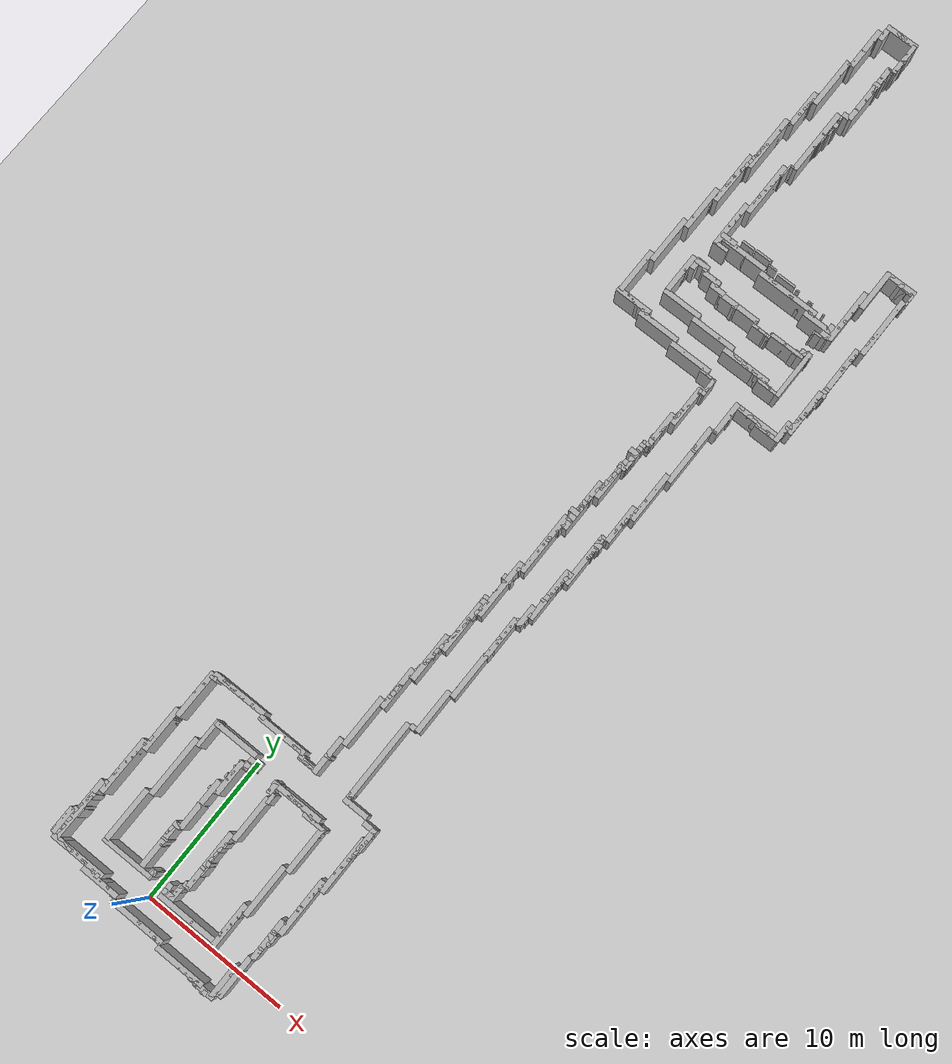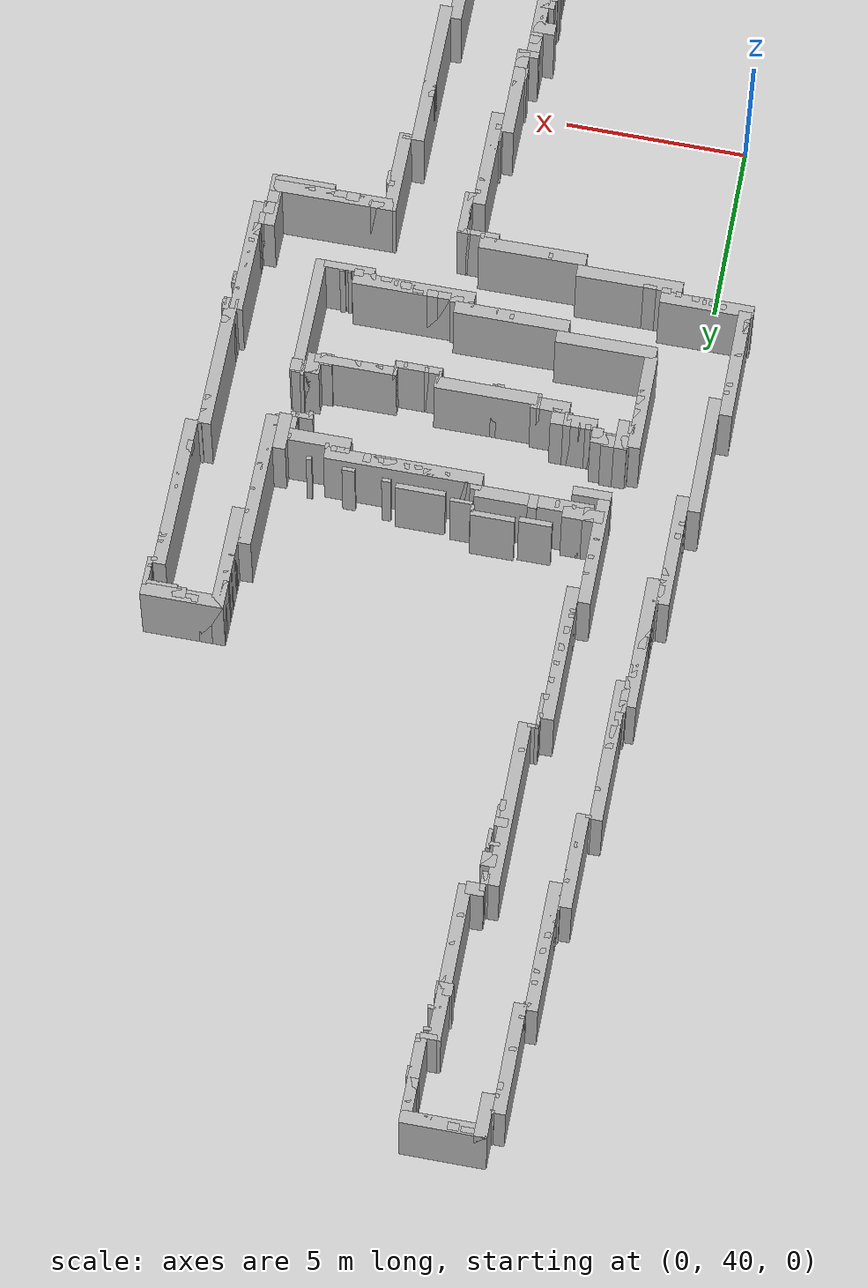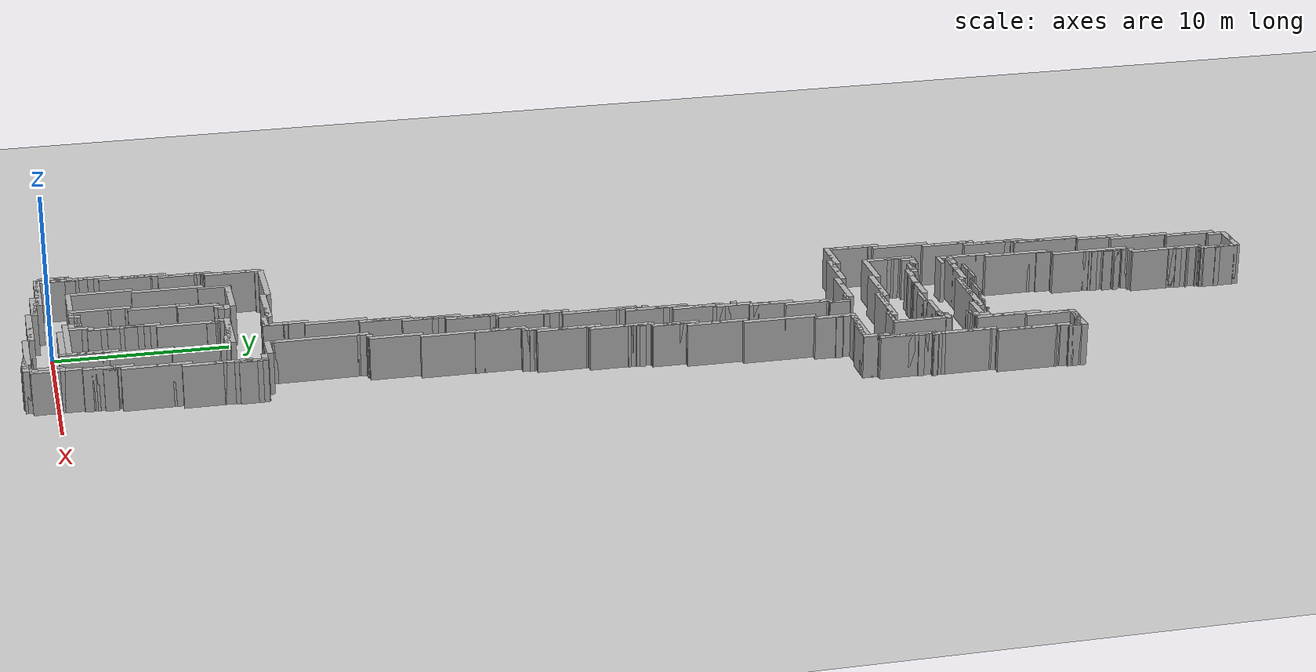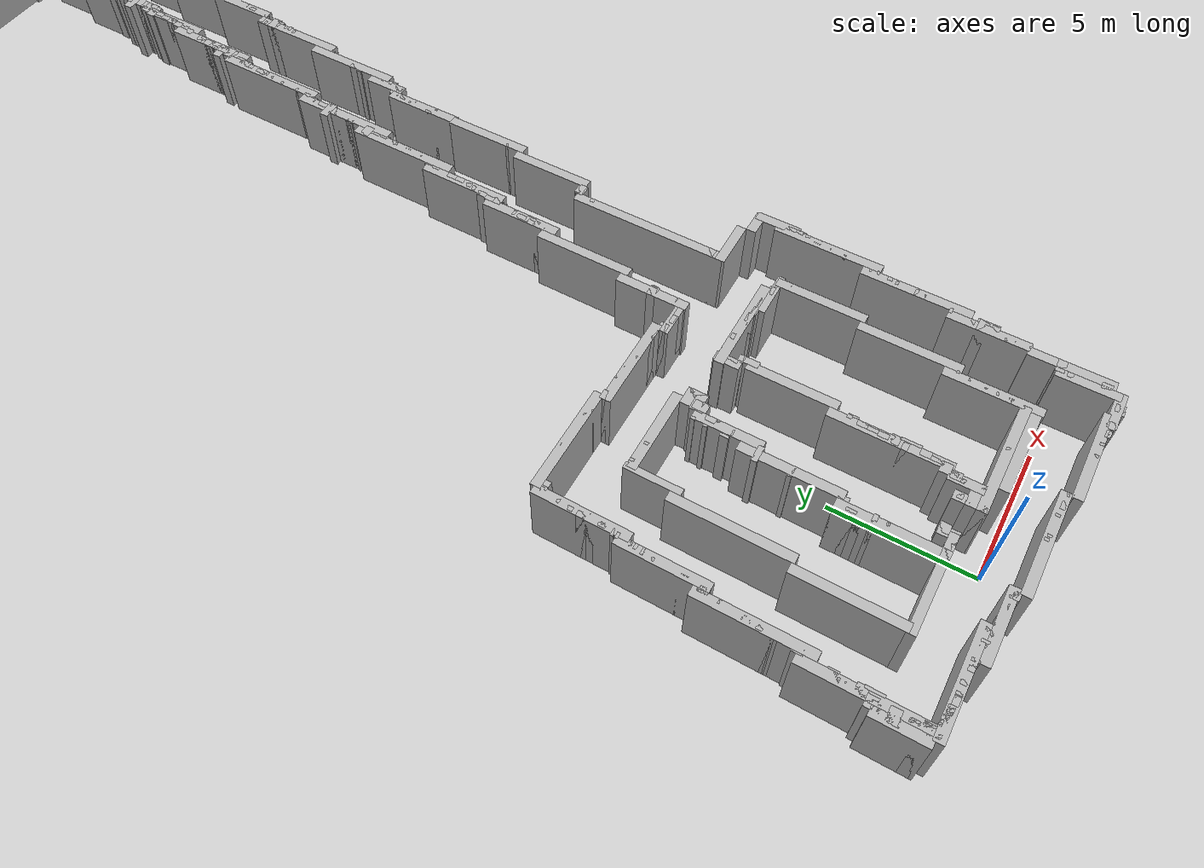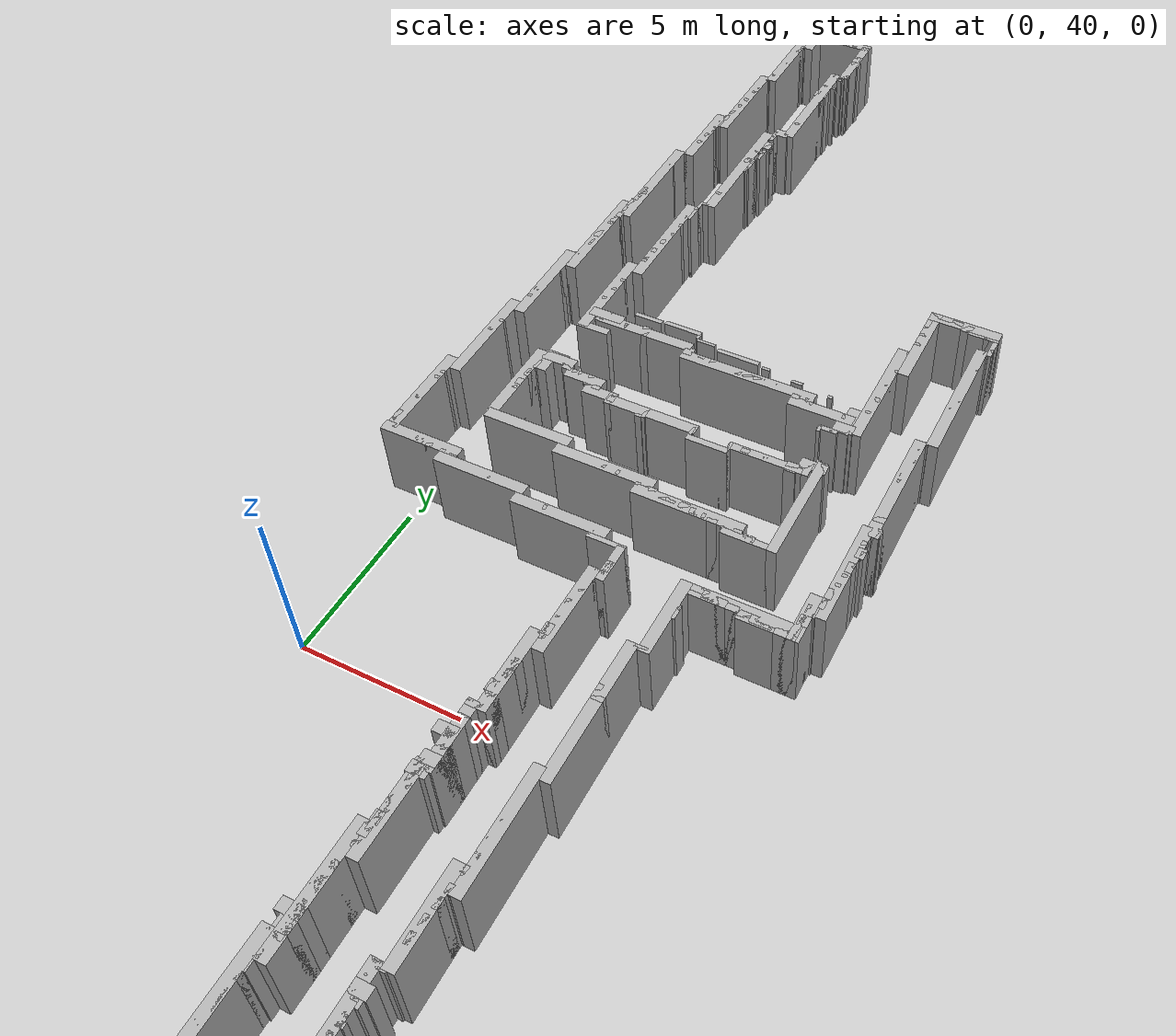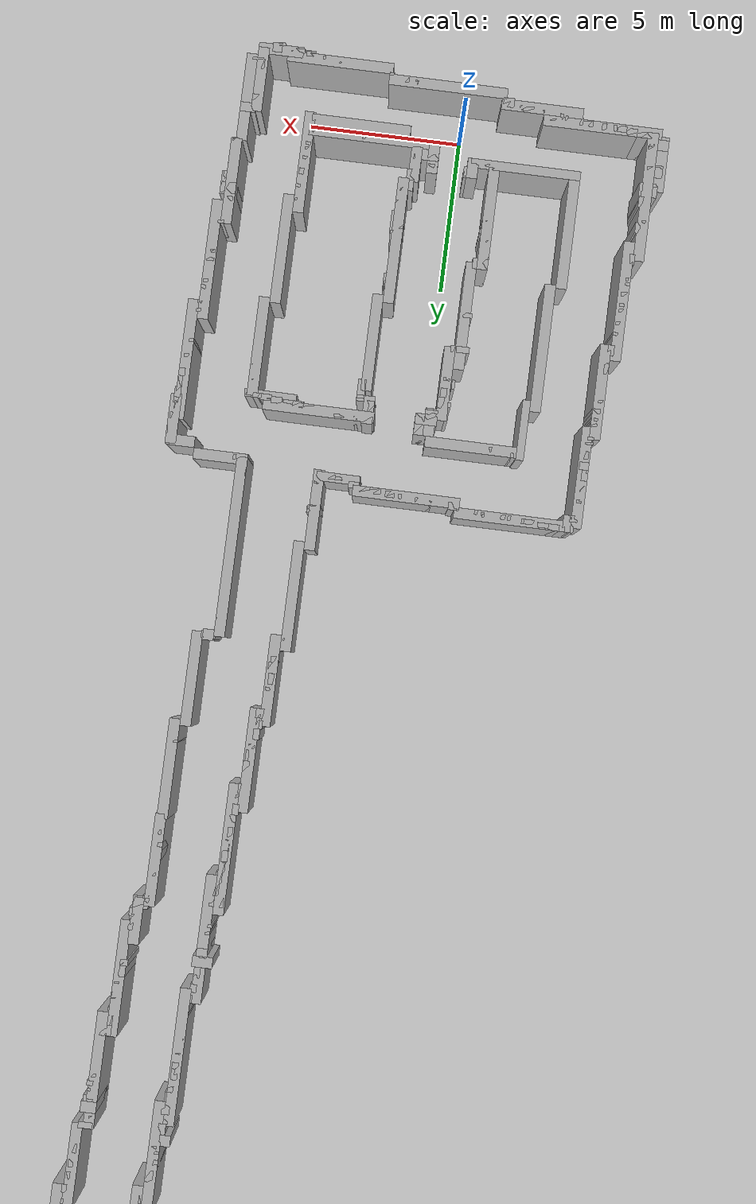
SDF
<?xml version='1.0' encoding='utf-8'?>
<sdf version="1.9">
  <world name="real_map_big_fix">
    <physics name="1ms" type="ignored">
      <max_step_size>0.001</max_step_size>
      <real_time_factor>1.0</real_time_factor>
    </physics>
    <plugin filename="gz-sim-physics-system" name="gz::sim::systems::Physics" />
    <plugin filename="gz-sim-user-commands-system" name="gz::sim::systems::UserCommands" />
    <plugin filename="gz-sim-scene-broadcaster-system" name="gz::sim::systems::SceneBroadcaster" />
    <plugin filename="gz-sim-sensors-system" name="gz::sim::systems::Sensors">
      <render_engine>ogre2</render_engine>
    </plugin>
    <plugin filename="gz-sim-contact-system" name="gz::sim::systems::Contact" />
    <light type="directional" name="sun">
      <cast_shadows>true</cast_shadows>
      <pose>0 0 10 0 0 0</pose>
      <diffuse>0.8 0.8 0.8 1</diffuse>
      <specular>0.2 0.2 0.2 1</specular>
      <attenuation>
        <range>1000</range>
        <constant>0.9</constant>
        <linear>0.01</linear>
        <quadratic>0.001</quadratic>
      </attenuation>
      <direction>-0.5 0.1 -0.9</direction>
    </light>
    <model name="ground_plane">
      <static>true</static>
      <link name="link">
        <collision name="collision">
          <geometry>
            <plane>
              <normal>0 0 1</normal>
              <size>100 100</size>
            </plane>
          </geometry>
        </collision>
        <visual name="visual">
          <geometry>
            <plane>
              <normal>0 0 1</normal>
              <size>100 100</size>
            </plane>
          </geometry>
          <material>
            <ambient>0.8 0.8 0.8 1</ambient>
            <diffuse>0.8 0.8 0.8 1</diffuse>
          </material>
        </visual>
      </link>
    </model>
    <model name="wall_h_000">
      <static>true</static>
      <pose>2.7770 70.1620 1.2500 0 0 0</pose>
      <link name="link">
        <collision name="collision">
          <geometry>
            <box>
              <size>2.3000 0.3500 2.5000</size>
            </box>
          </geometry>
        </collision>
        <visual name="visual">
          <geometry>
            <box>
              <size>2.3000 0.3500 2.5000</size>
            </box>
          </geometry>
          <material>
            <ambient>0.7 0.7 0.7 1</ambient>
            <diffuse>0.7 0.7 0.7 1</diffuse>
          </material>
        </visual>
      </link>
    </model>
    <model name="wall_h_001">
      <static>true</static>
      <pose>3.8020 69.7120 1.2500 0 0 0</pose>
      <link name="link">
        <collision name="collision">
          <geometry>
            <box>
              <size>0.1500 0.1000 2.5000</size>
            </box>
          </geometry>
        </collision>
        <visual name="visual">
          <geometry>
            <box>
              <size>0.1500 0.1000 2.5000</size>
            </box>
          </geometry>
          <material>
            <ambient>0.7 0.7 0.7 1</ambient>
            <diffuse>0.7 0.7 0.7 1</diffuse>
          </material>
        </visual>
      </link>
    </model>
    <model name="wall_h_002">
      <static>true</static>
      <pose>1.6520 69.6120 1.2500 0 0 0</pose>
      <link name="link">
        <collision name="collision">
          <geometry>
            <box>
              <size>0.1500 0.1000 2.5000</size>
            </box>
          </geometry>
        </collision>
        <visual name="visual">
          <geometry>
            <box>
              <size>0.1500 0.1000 2.5000</size>
            </box>
          </geometry>
          <material>
            <ambient>0.7 0.7 0.7 1</ambient>
            <diffuse>0.7 0.7 0.7 1</diffuse>
          </material>
        </visual>
      </link>
    </model>
    <model name="wall_h_003">
      <static>true</static>
      <pose>3.7520 69.2620 1.2500 0 0 0</pose>
      <link name="link">
        <collision name="collision">
          <geometry>
            <box>
              <size>0.2500 0.3500 2.5000</size>
            </box>
          </geometry>
        </collision>
        <visual name="visual">
          <geometry>
            <box>
              <size>0.2500 0.3500 2.5000</size>
            </box>
          </geometry>
          <material>
            <ambient>0.7 0.7 0.7 1</ambient>
            <diffuse>0.7 0.7 0.7 1</diffuse>
          </material>
        </visual>
      </link>
    </model>
    <model name="wall_h_004">
      <static>true</static>
      <pose>1.6020 69.1620 1.2500 0 0 0</pose>
      <link name="link">
        <collision name="collision">
          <geometry>
            <box>
              <size>0.1500 0.1000 2.5000</size>
            </box>
          </geometry>
        </collision>
        <visual name="visual">
          <geometry>
            <box>
              <size>0.1500 0.1000 2.5000</size>
            </box>
          </geometry>
          <material>
            <ambient>0.7 0.7 0.7 1</ambient>
            <diffuse>0.7 0.7 0.7 1</diffuse>
          </material>
        </visual>
      </link>
    </model>
    <model name="wall_h_005">
      <static>true</static>
      <pose>3.8270 68.9370 1.2500 0 0 0</pose>
      <link name="link">
        <collision name="collision">
          <geometry>
            <box>
              <size>0.3000 0.3000 2.5000</size>
            </box>
          </geometry>
        </collision>
        <visual name="visual">
          <geometry>
            <box>
              <size>0.3000 0.3000 2.5000</size>
            </box>
          </geometry>
          <material>
            <ambient>0.7 0.7 0.7 1</ambient>
            <diffuse>0.7 0.7 0.7 1</diffuse>
          </material>
        </visual>
      </link>
    </model>
    <model name="wall_h_006">
      <static>true</static>
      <pose>1.5520 68.8870 1.2500 0 0 0</pose>
      <link name="link">
        <collision name="collision">
          <geometry>
            <box>
              <size>0.1500 0.2000 2.5000</size>
            </box>
          </geometry>
        </collision>
        <visual name="visual">
          <geometry>
            <box>
              <size>0.1500 0.2000 2.5000</size>
            </box>
          </geometry>
          <material>
            <ambient>0.7 0.7 0.7 1</ambient>
            <diffuse>0.7 0.7 0.7 1</diffuse>
          </material>
        </visual>
      </link>
    </model>
    <model name="wall_h_007">
      <static>true</static>
      <pose>3.8520 68.0620 1.2500 0 0 0</pose>
      <link name="link">
        <collision name="collision">
          <geometry>
            <box>
              <size>0.1500 0.1000 2.5000</size>
            </box>
          </geometry>
        </collision>
        <visual name="visual">
          <geometry>
            <box>
              <size>0.1500 0.1000 2.5000</size>
            </box>
          </geometry>
          <material>
            <ambient>0.7 0.7 0.7 1</ambient>
            <diffuse>0.7 0.7 0.7 1</diffuse>
          </material>
        </visual>
      </link>
    </model>
    <model name="wall_h_008">
      <static>true</static>
      <pose>3.6020 67.9120 1.2500 0 0 0</pose>
      <link name="link">
        <collision name="collision">
          <geometry>
            <box>
              <size>0.4500 0.1500 2.5000</size>
            </box>
          </geometry>
        </collision>
        <visual name="visual">
          <geometry>
            <box>
              <size>0.4500 0.1500 2.5000</size>
            </box>
          </geometry>
          <material>
            <ambient>0.7 0.7 0.7 1</ambient>
            <diffuse>0.7 0.7 0.7 1</diffuse>
          </material>
        </visual>
      </link>
    </model>
    <model name="wall_h_009">
      <static>true</static>
      <pose>1.4270 67.8370 1.2500 0 0 0</pose>
      <link name="link">
        <collision name="collision">
          <geometry>
            <box>
              <size>0.2000 0.1000 2.5000</size>
            </box>
          </geometry>
        </collision>
        <visual name="visual">
          <geometry>
            <box>
              <size>0.2000 0.1000 2.5000</size>
            </box>
          </geometry>
          <material>
            <ambient>0.7 0.7 0.7 1</ambient>
            <diffuse>0.7 0.7 0.7 1</diffuse>
          </material>
        </visual>
      </link>
    </model>
    <model name="wall_h_010">
      <static>true</static>
      <pose>3.6770 67.7120 1.2500 0 0 0</pose>
      <link name="link">
        <collision name="collision">
          <geometry>
            <box>
              <size>0.2000 0.1000 2.5000</size>
            </box>
          </geometry>
        </collision>
        <visual name="visual">
          <geometry>
            <box>
              <size>0.2000 0.1000 2.5000</size>
            </box>
          </geometry>
          <material>
            <ambient>0.7 0.7 0.7 1</ambient>
            <diffuse>0.7 0.7 0.7 1</diffuse>
          </material>
        </visual>
      </link>
    </model>
    <model name="wall_h_011">
      <static>true</static>
      <pose>3.4020 67.1120 1.2500 0 0 0</pose>
      <link name="link">
        <collision name="collision">
          <geometry>
            <box>
              <size>0.1500 0.1000 2.5000</size>
            </box>
          </geometry>
        </collision>
        <visual name="visual">
          <geometry>
            <box>
              <size>0.1500 0.1000 2.5000</size>
            </box>
          </geometry>
          <material>
            <ambient>0.7 0.7 0.7 1</ambient>
            <diffuse>0.7 0.7 0.7 1</diffuse>
          </material>
        </visual>
      </link>
    </model>
    <model name="wall_h_012">
      <static>true</static>
      <pose>3.6770 67.1120 1.2500 0 0 0</pose>
      <link name="link">
        <collision name="collision">
          <geometry>
            <box>
              <size>0.2000 0.1000 2.5000</size>
            </box>
          </geometry>
        </collision>
        <visual name="visual">
          <geometry>
            <box>
              <size>0.2000 0.1000 2.5000</size>
            </box>
          </geometry>
          <material>
            <ambient>0.7 0.7 0.7 1</ambient>
            <diffuse>0.7 0.7 0.7 1</diffuse>
          </material>
        </visual>
      </link>
    </model>
    <model name="wall_h_013">
      <static>true</static>
      <pose>1.3520 66.9370 1.2500 0 0 0</pose>
      <link name="link">
        <collision name="collision">
          <geometry>
            <box>
              <size>0.1500 0.1000 2.5000</size>
            </box>
          </geometry>
        </collision>
        <visual name="visual">
          <geometry>
            <box>
              <size>0.1500 0.1000 2.5000</size>
            </box>
          </geometry>
          <material>
            <ambient>0.7 0.7 0.7 1</ambient>
            <diffuse>0.7 0.7 0.7 1</diffuse>
          </material>
        </visual>
      </link>
    </model>
    <model name="wall_h_014">
      <static>true</static>
      <pose>3.4520 66.5620 1.2500 0 0 0</pose>
      <link name="link">
        <collision name="collision">
          <geometry>
            <box>
              <size>0.4500 0.3500 2.5000</size>
            </box>
          </geometry>
        </collision>
        <visual name="visual">
          <geometry>
            <box>
              <size>0.4500 0.3500 2.5000</size>
            </box>
          </geometry>
          <material>
            <ambient>0.7 0.7 0.7 1</ambient>
            <diffuse>0.7 0.7 0.7 1</diffuse>
          </material>
        </visual>
      </link>
    </model>
    <model name="wall_h_015">
      <static>true</static>
      <pose>1.2770 66.6120 1.2500 0 0 0</pose>
      <link name="link">
        <collision name="collision">
          <geometry>
            <box>
              <size>0.2000 0.1500 2.5000</size>
            </box>
          </geometry>
        </collision>
        <visual name="visual">
          <geometry>
            <box>
              <size>0.2000 0.1500 2.5000</size>
            </box>
          </geometry>
          <material>
            <ambient>0.7 0.7 0.7 1</ambient>
            <diffuse>0.7 0.7 0.7 1</diffuse>
          </material>
        </visual>
      </link>
    </model>
    <model name="wall_h_016">
      <static>true</static>
      <pose>3.5520 66.2120 1.2500 0 0 0</pose>
      <link name="link">
        <collision name="collision">
          <geometry>
            <box>
              <size>0.1500 0.3500 2.5000</size>
            </box>
          </geometry>
        </collision>
        <visual name="visual">
          <geometry>
            <box>
              <size>0.1500 0.3500 2.5000</size>
            </box>
          </geometry>
          <material>
            <ambient>0.7 0.7 0.7 1</ambient>
            <diffuse>0.7 0.7 0.7 1</diffuse>
          </material>
        </visual>
      </link>
    </model>
    <model name="wall_h_017">
      <static>true</static>
      <pose>3.5520 65.9620 1.2500 0 0 0</pose>
      <link name="link">
        <collision name="collision">
          <geometry>
            <box>
              <size>0.1500 0.1500 2.5000</size>
            </box>
          </geometry>
        </collision>
        <visual name="visual">
          <geometry>
            <box>
              <size>0.1500 0.1500 2.5000</size>
            </box>
          </geometry>
          <material>
            <ambient>0.7 0.7 0.7 1</ambient>
            <diffuse>0.7 0.7 0.7 1</diffuse>
          </material>
        </visual>
      </link>
    </model>
    <model name="wall_h_018">
      <static>true</static>
      <pose>1.2020 65.9620 1.2500 0 0 0</pose>
      <link name="link">
        <collision name="collision">
          <geometry>
            <box>
              <size>0.1500 0.1000 2.5000</size>
            </box>
          </geometry>
        </collision>
        <visual name="visual">
          <geometry>
            <box>
              <size>0.1500 0.1000 2.5000</size>
            </box>
          </geometry>
          <material>
            <ambient>0.7 0.7 0.7 1</ambient>
            <diffuse>0.7 0.7 0.7 1</diffuse>
          </material>
        </visual>
      </link>
    </model>
    <model name="wall_h_019">
      <static>true</static>
      <pose>1.2020 65.6370 1.2500 0 0 0</pose>
      <link name="link">
        <collision name="collision">
          <geometry>
            <box>
              <size>0.1500 0.1000 2.5000</size>
            </box>
          </geometry>
        </collision>
        <visual name="visual">
          <geometry>
            <box>
              <size>0.1500 0.1000 2.5000</size>
            </box>
          </geometry>
          <material>
            <ambient>0.7 0.7 0.7 1</ambient>
            <diffuse>0.7 0.7 0.7 1</diffuse>
          </material>
        </visual>
      </link>
    </model>
    <model name="wall_h_020">
      <static>true</static>
      <pose>3.5020 65.2870 1.2500 0 0 0</pose>
      <link name="link">
        <collision name="collision">
          <geometry>
            <box>
              <size>0.1500 0.1000 2.5000</size>
            </box>
          </geometry>
        </collision>
        <visual name="visual">
          <geometry>
            <box>
              <size>0.1500 0.1000 2.5000</size>
            </box>
          </geometry>
          <material>
            <ambient>0.7 0.7 0.7 1</ambient>
            <diffuse>0.7 0.7 0.7 1</diffuse>
          </material>
        </visual>
      </link>
    </model>
    <model name="wall_h_021">
      <static>true</static>
      <pose>1.1520 65.0620 1.2500 0 0 0</pose>
      <link name="link">
        <collision name="collision">
          <geometry>
            <box>
              <size>0.1500 0.1500 2.5000</size>
            </box>
          </geometry>
        </collision>
        <visual name="visual">
          <geometry>
            <box>
              <size>0.1500 0.1500 2.5000</size>
            </box>
          </geometry>
          <material>
            <ambient>0.7 0.7 0.7 1</ambient>
            <diffuse>0.7 0.7 0.7 1</diffuse>
          </material>
        </visual>
      </link>
    </model>
    <model name="wall_h_022">
      <static>true</static>
      <pose>1.1020 64.6120 1.2500 0 0 0</pose>
      <link name="link">
        <collision name="collision">
          <geometry>
            <box>
              <size>0.1500 0.1500 2.5000</size>
            </box>
          </geometry>
        </collision>
        <visual name="visual">
          <geometry>
            <box>
              <size>0.1500 0.1500 2.5000</size>
            </box>
          </geometry>
          <material>
            <ambient>0.7 0.7 0.7 1</ambient>
            <diffuse>0.7 0.7 0.7 1</diffuse>
          </material>
        </visual>
      </link>
    </model>
    <model name="wall_h_023">
      <static>true</static>
      <pose>3.4270 64.4870 1.2500 0 0 0</pose>
      <link name="link">
        <collision name="collision">
          <geometry>
            <box>
              <size>0.2000 0.1000 2.5000</size>
            </box>
          </geometry>
        </collision>
        <visual name="visual">
          <geometry>
            <box>
              <size>0.2000 0.1000 2.5000</size>
            </box>
          </geometry>
          <material>
            <ambient>0.7 0.7 0.7 1</ambient>
            <diffuse>0.7 0.7 0.7 1</diffuse>
          </material>
        </visual>
      </link>
    </model>
    <model name="wall_h_024">
      <static>true</static>
      <pose>1.0520 64.1370 1.2500 0 0 0</pose>
      <link name="link">
        <collision name="collision">
          <geometry>
            <box>
              <size>0.1500 0.2000 2.5000</size>
            </box>
          </geometry>
        </collision>
        <visual name="visual">
          <geometry>
            <box>
              <size>0.1500 0.2000 2.5000</size>
            </box>
          </geometry>
          <material>
            <ambient>0.7 0.7 0.7 1</ambient>
            <diffuse>0.7 0.7 0.7 1</diffuse>
          </material>
        </visual>
      </link>
    </model>
    <model name="wall_h_025">
      <static>true</static>
      <pose>1.0020 63.7370 1.2500 0 0 0</pose>
      <link name="link">
        <collision name="collision">
          <geometry>
            <box>
              <size>0.1500 0.3000 2.5000</size>
            </box>
          </geometry>
        </collision>
        <visual name="visual">
          <geometry>
            <box>
              <size>0.1500 0.3000 2.5000</size>
            </box>
          </geometry>
          <material>
            <ambient>0.7 0.7 0.7 1</ambient>
            <diffuse>0.7 0.7 0.7 1</diffuse>
          </material>
        </visual>
      </link>
    </model>
    <model name="wall_h_026">
      <static>true</static>
      <pose>3.1770 63.7120 1.2500 0 0 0</pose>
      <link name="link">
        <collision name="collision">
          <geometry>
            <box>
              <size>0.5000 0.3500 2.5000</size>
            </box>
          </geometry>
        </collision>
        <visual name="visual">
          <geometry>
            <box>
              <size>0.5000 0.3500 2.5000</size>
            </box>
          </geometry>
          <material>
            <ambient>0.7 0.7 0.7 1</ambient>
            <diffuse>0.7 0.7 0.7 1</diffuse>
          </material>
        </visual>
      </link>
    </model>
    <model name="wall_h_027">
      <static>true</static>
      <pose>2.9770 63.3870 1.2500 0 0 0</pose>
      <link name="link">
        <collision name="collision">
          <geometry>
            <box>
              <size>0.2000 0.3000 2.5000</size>
            </box>
          </geometry>
        </collision>
        <visual name="visual">
          <geometry>
            <box>
              <size>0.2000 0.3000 2.5000</size>
            </box>
          </geometry>
          <material>
            <ambient>0.7 0.7 0.7 1</ambient>
            <diffuse>0.7 0.7 0.7 1</diffuse>
          </material>
        </visual>
      </link>
    </model>
    <model name="wall_h_028">
      <static>true</static>
      <pose>0.9520 63.3120 1.2500 0 0 0</pose>
      <link name="link">
        <collision name="collision">
          <geometry>
            <box>
              <size>0.1500 0.3500 2.5000</size>
            </box>
          </geometry>
        </collision>
        <visual name="visual">
          <geometry>
            <box>
              <size>0.1500 0.3500 2.5000</size>
            </box>
          </geometry>
          <material>
            <ambient>0.7 0.7 0.7 1</ambient>
            <diffuse>0.7 0.7 0.7 1</diffuse>
          </material>
        </visual>
      </link>
    </model>
    <model name="wall_h_029">
      <static>true</static>
      <pose>0.9020 63.0370 1.2500 0 0 0</pose>
      <link name="link">
        <collision name="collision">
          <geometry>
            <box>
              <size>0.1500 0.1000 2.5000</size>
            </box>
          </geometry>
        </collision>
        <visual name="visual">
          <geometry>
            <box>
              <size>0.1500 0.1000 2.5000</size>
            </box>
          </geometry>
          <material>
            <ambient>0.7 0.7 0.7 1</ambient>
            <diffuse>0.7 0.7 0.7 1</diffuse>
          </material>
        </visual>
      </link>
    </model>
    <model name="wall_h_030">
      <static>true</static>
      <pose>2.9770 62.8620 1.2500 0 0 0</pose>
      <link name="link">
        <collision name="collision">
          <geometry>
            <box>
              <size>0.4000 0.3500 2.5000</size>
            </box>
          </geometry>
        </collision>
        <visual name="visual">
          <geometry>
            <box>
              <size>0.4000 0.3500 2.5000</size>
            </box>
          </geometry>
          <material>
            <ambient>0.7 0.7 0.7 1</ambient>
            <diffuse>0.7 0.7 0.7 1</diffuse>
          </material>
        </visual>
      </link>
    </model>
    <model name="wall_h_031">
      <static>true</static>
      <pose>0.9020 62.8120 1.2500 0 0 0</pose>
      <link name="link">
        <collision name="collision">
          <geometry>
            <box>
              <size>0.1500 0.1500 2.5000</size>
            </box>
          </geometry>
        </collision>
        <visual name="visual">
          <geometry>
            <box>
              <size>0.1500 0.1500 2.5000</size>
            </box>
          </geometry>
          <material>
            <ambient>0.7 0.7 0.7 1</ambient>
            <diffuse>0.7 0.7 0.7 1</diffuse>
          </material>
        </visual>
      </link>
    </model>
    <model name="wall_h_032">
      <static>true</static>
      <pose>0.8520 62.4870 1.2500 0 0 0</pose>
      <link name="link">
        <collision name="collision">
          <geometry>
            <box>
              <size>0.1500 0.2000 2.5000</size>
            </box>
          </geometry>
        </collision>
        <visual name="visual">
          <geometry>
            <box>
              <size>0.1500 0.2000 2.5000</size>
            </box>
          </geometry>
          <material>
            <ambient>0.7 0.7 0.7 1</ambient>
            <diffuse>0.7 0.7 0.7 1</diffuse>
          </material>
        </visual>
      </link>
    </model>
    <model name="wall_h_033">
      <static>true</static>
      <pose>2.9270 62.3870 1.2500 0 0 0</pose>
      <link name="link">
        <collision name="collision">
          <geometry>
            <box>
              <size>0.3000 0.1000 2.5000</size>
            </box>
          </geometry>
        </collision>
        <visual name="visual">
          <geometry>
            <box>
              <size>0.3000 0.1000 2.5000</size>
            </box>
          </geometry>
          <material>
            <ambient>0.7 0.7 0.7 1</ambient>
            <diffuse>0.7 0.7 0.7 1</diffuse>
          </material>
        </visual>
      </link>
    </model>
    <model name="wall_h_034">
      <static>true</static>
      <pose>0.8020 62.0120 1.2500 0 0 0</pose>
      <link name="link">
        <collision name="collision">
          <geometry>
            <box>
              <size>0.1500 0.1500 2.5000</size>
            </box>
          </geometry>
        </collision>
        <visual name="visual">
          <geometry>
            <box>
              <size>0.1500 0.1500 2.5000</size>
            </box>
          </geometry>
          <material>
            <ambient>0.7 0.7 0.7 1</ambient>
            <diffuse>0.7 0.7 0.7 1</diffuse>
          </material>
        </visual>
      </link>
    </model>
    <model name="wall_h_035">
      <static>true</static>
      <pose>2.8520 61.7620 1.2500 0 0 0</pose>
      <link name="link">
        <collision name="collision">
          <geometry>
            <box>
              <size>0.3500 0.2500 2.5000</size>
            </box>
          </geometry>
        </collision>
        <visual name="visual">
          <geometry>
            <box>
              <size>0.3500 0.2500 2.5000</size>
            </box>
          </geometry>
          <material>
            <ambient>0.7 0.7 0.7 1</ambient>
            <diffuse>0.7 0.7 0.7 1</diffuse>
          </material>
        </visual>
      </link>
    </model>
    <model name="wall_h_036">
      <static>true</static>
      <pose>2.9020 61.2870 1.2500 0 0 0</pose>
      <link name="link">
        <collision name="collision">
          <geometry>
            <box>
              <size>0.1500 0.3000 2.5000</size>
            </box>
          </geometry>
        </collision>
        <visual name="visual">
          <geometry>
            <box>
              <size>0.1500 0.3000 2.5000</size>
            </box>
          </geometry>
          <material>
            <ambient>0.7 0.7 0.7 1</ambient>
            <diffuse>0.7 0.7 0.7 1</diffuse>
          </material>
        </visual>
      </link>
    </model>
    <model name="wall_h_037">
      <static>true</static>
      <pose>0.6520 61.1870 1.2500 0 0 0</pose>
      <link name="link">
        <collision name="collision">
          <geometry>
            <box>
              <size>0.1500 0.1000 2.5000</size>
            </box>
          </geometry>
        </collision>
        <visual name="visual">
          <geometry>
            <box>
              <size>0.1500 0.1000 2.5000</size>
            </box>
          </geometry>
          <material>
            <ambient>0.7 0.7 0.7 1</ambient>
            <diffuse>0.7 0.7 0.7 1</diffuse>
          </material>
        </visual>
      </link>
    </model>
    <model name="wall_h_038">
      <static>true</static>
      <pose>2.8520 60.8620 1.2500 0 0 0</pose>
      <link name="link">
        <collision name="collision">
          <geometry>
            <box>
              <size>0.1500 0.1500 2.5000</size>
            </box>
          </geometry>
        </collision>
        <visual name="visual">
          <geometry>
            <box>
              <size>0.1500 0.1500 2.5000</size>
            </box>
          </geometry>
          <material>
            <ambient>0.7 0.7 0.7 1</ambient>
            <diffuse>0.7 0.7 0.7 1</diffuse>
          </material>
        </visual>
      </link>
    </model>
    <model name="wall_h_039">
      <static>true</static>
      <pose>0.5520 60.3620 1.2500 0 0 0</pose>
      <link name="link">
        <collision name="collision">
          <geometry>
            <box>
              <size>0.1500 0.1000 2.5000</size>
            </box>
          </geometry>
        </collision>
        <visual name="visual">
          <geometry>
            <box>
              <size>0.1500 0.1000 2.5000</size>
            </box>
          </geometry>
          <material>
            <ambient>0.7 0.7 0.7 1</ambient>
            <diffuse>0.7 0.7 0.7 1</diffuse>
          </material>
        </visual>
      </link>
    </model>
    <model name="wall_h_040">
      <static>true</static>
      <pose>2.7020 59.6620 1.2500 0 0 0</pose>
      <link name="link">
        <collision name="collision">
          <geometry>
            <box>
              <size>0.1500 0.1000 2.5000</size>
            </box>
          </geometry>
        </collision>
        <visual name="visual">
          <geometry>
            <box>
              <size>0.1500 0.1000 2.5000</size>
            </box>
          </geometry>
          <material>
            <ambient>0.7 0.7 0.7 1</ambient>
            <diffuse>0.7 0.7 0.7 1</diffuse>
          </material>
        </visual>
      </link>
    </model>
    <model name="wall_h_041">
      <static>true</static>
      <pose>0.4770 59.1120 1.2500 0 0 0</pose>
      <link name="link">
        <collision name="collision">
          <geometry>
            <box>
              <size>0.2000 0.1500 2.5000</size>
            </box>
          </geometry>
        </collision>
        <visual name="visual">
          <geometry>
            <box>
              <size>0.2000 0.1500 2.5000</size>
            </box>
          </geometry>
          <material>
            <ambient>0.7 0.7 0.7 1</ambient>
            <diffuse>0.7 0.7 0.7 1</diffuse>
          </material>
        </visual>
      </link>
    </model>
    <model name="wall_h_042">
      <static>true</static>
      <pose>2.5270 58.9370 1.2500 0 0 0</pose>
      <link name="link">
        <collision name="collision">
          <geometry>
            <box>
              <size>0.3000 0.1000 2.5000</size>
            </box>
          </geometry>
        </collision>
        <visual name="visual">
          <geometry>
            <box>
              <size>0.3000 0.1000 2.5000</size>
            </box>
          </geometry>
          <material>
            <ambient>0.7 0.7 0.7 1</ambient>
            <diffuse>0.7 0.7 0.7 1</diffuse>
          </material>
        </visual>
      </link>
    </model>
    <model name="wall_h_043">
      <static>true</static>
      <pose>0.4270 58.7120 1.2500 0 0 0</pose>
      <link name="link">
        <collision name="collision">
          <geometry>
            <box>
              <size>0.2000 0.3500 2.5000</size>
            </box>
          </geometry>
        </collision>
        <visual name="visual">
          <geometry>
            <box>
              <size>0.2000 0.3500 2.5000</size>
            </box>
          </geometry>
          <material>
            <ambient>0.7 0.7 0.7 1</ambient>
            <diffuse>0.7 0.7 0.7 1</diffuse>
          </material>
        </visual>
      </link>
    </model>
    <model name="wall_h_044">
      <static>true</static>
      <pose>2.4020 58.6120 1.2500 0 0 0</pose>
      <link name="link">
        <collision name="collision">
          <geometry>
            <box>
              <size>0.1500 0.1500 2.5000</size>
            </box>
          </geometry>
        </collision>
        <visual name="visual">
          <geometry>
            <box>
              <size>0.1500 0.1500 2.5000</size>
            </box>
          </geometry>
          <material>
            <ambient>0.7 0.7 0.7 1</ambient>
            <diffuse>0.7 0.7 0.7 1</diffuse>
          </material>
        </visual>
      </link>
    </model>
    <model name="wall_h_045">
      <static>true</static>
      <pose>0.3770 58.3120 1.2500 0 0 0</pose>
      <link name="link">
        <collision name="collision">
          <geometry>
            <box>
              <size>0.2000 0.3500 2.5000</size>
            </box>
          </geometry>
        </collision>
        <visual name="visual">
          <geometry>
            <box>
              <size>0.2000 0.3500 2.5000</size>
            </box>
          </geometry>
          <material>
            <ambient>0.7 0.7 0.7 1</ambient>
            <diffuse>0.7 0.7 0.7 1</diffuse>
          </material>
        </visual>
      </link>
    </model>
    <model name="wall_h_046">
      <static>true</static>
      <pose>0.3270 57.9620 1.2500 0 0 0</pose>
      <link name="link">
        <collision name="collision">
          <geometry>
            <box>
              <size>0.2000 0.3500 2.5000</size>
            </box>
          </geometry>
        </collision>
        <visual name="visual">
          <geometry>
            <box>
              <size>0.2000 0.3500 2.5000</size>
            </box>
          </geometry>
          <material>
            <ambient>0.7 0.7 0.7 1</ambient>
            <diffuse>0.7 0.7 0.7 1</diffuse>
          </material>
        </visual>
      </link>
    </model>
    <model name="wall_h_047">
      <static>true</static>
      <pose>2.3520 58.0620 1.2500 0 0 0</pose>
      <link name="link">
        <collision name="collision">
          <geometry>
            <box>
              <size>0.1500 0.1500 2.5000</size>
            </box>
          </geometry>
        </collision>
        <visual name="visual">
          <geometry>
            <box>
              <size>0.1500 0.1500 2.5000</size>
            </box>
          </geometry>
          <material>
            <ambient>0.7 0.7 0.7 1</ambient>
            <diffuse>0.7 0.7 0.7 1</diffuse>
          </material>
        </visual>
      </link>
    </model>
    <model name="wall_h_048">
      <static>true</static>
      <pose>0.3270 57.6120 1.2500 0 0 0</pose>
      <link name="link">
        <collision name="collision">
          <geometry>
            <box>
              <size>0.2000 0.3500 2.5000</size>
            </box>
          </geometry>
        </collision>
        <visual name="visual">
          <geometry>
            <box>
              <size>0.2000 0.3500 2.5000</size>
            </box>
          </geometry>
          <material>
            <ambient>0.7 0.7 0.7 1</ambient>
            <diffuse>0.7 0.7 0.7 1</diffuse>
          </material>
        </visual>
      </link>
    </model>
    <model name="wall_h_049">
      <static>true</static>
      <pose>2.3020 57.5620 1.2500 0 0 0</pose>
      <link name="link">
        <collision name="collision">
          <geometry>
            <box>
              <size>0.1500 0.1500 2.5000</size>
            </box>
          </geometry>
        </collision>
        <visual name="visual">
          <geometry>
            <box>
              <size>0.1500 0.1500 2.5000</size>
            </box>
          </geometry>
          <material>
            <ambient>0.7 0.7 0.7 1</ambient>
            <diffuse>0.7 0.7 0.7 1</diffuse>
          </material>
        </visual>
      </link>
    </model>
    <model name="wall_h_050">
      <static>true</static>
      <pose>0.2770 57.2620 1.2500 0 0 0</pose>
      <link name="link">
        <collision name="collision">
          <geometry>
            <box>
              <size>0.2000 0.3500 2.5000</size>
            </box>
          </geometry>
        </collision>
        <visual name="visual">
          <geometry>
            <box>
              <size>0.2000 0.3500 2.5000</size>
            </box>
          </geometry>
          <material>
            <ambient>0.7 0.7 0.7 1</ambient>
            <diffuse>0.7 0.7 0.7 1</diffuse>
          </material>
        </visual>
      </link>
    </model>
    <model name="wall_h_051">
      <static>true</static>
      <pose>12.3020 57.0120 1.2500 0 0 0</pose>
      <link name="link">
        <collision name="collision">
          <geometry>
            <box>
              <size>2.2500 0.3500 2.5000</size>
            </box>
          </geometry>
        </collision>
        <visual name="visual">
          <geometry>
            <box>
              <size>2.2500 0.3500 2.5000</size>
            </box>
          </geometry>
          <material>
            <ambient>0.7 0.7 0.7 1</ambient>
            <diffuse>0.7 0.7 0.7 1</diffuse>
          </material>
        </visual>
      </link>
    </model>
    <model name="wall_h_052">
      <static>true</static>
      <pose>0.2270 56.9120 1.2500 0 0 0</pose>
      <link name="link">
        <collision name="collision">
          <geometry>
            <box>
              <size>0.2000 0.3500 2.5000</size>
            </box>
          </geometry>
        </collision>
        <visual name="visual">
          <geometry>
            <box>
              <size>0.2000 0.3500 2.5000</size>
            </box>
          </geometry>
          <material>
            <ambient>0.7 0.7 0.7 1</ambient>
            <diffuse>0.7 0.7 0.7 1</diffuse>
          </material>
        </visual>
      </link>
    </model>
    <model name="wall_h_053">
      <static>true</static>
      <pose>2.2520 57.0620 1.2500 0 0 0</pose>
      <link name="link">
        <collision name="collision">
          <geometry>
            <box>
              <size>0.1500 0.1000 2.5000</size>
            </box>
          </geometry>
        </collision>
        <visual name="visual">
          <geometry>
            <box>
              <size>0.1500 0.1000 2.5000</size>
            </box>
          </geometry>
          <material>
            <ambient>0.7 0.7 0.7 1</ambient>
            <diffuse>0.7 0.7 0.7 1</diffuse>
          </material>
        </visual>
      </link>
    </model>
    <model name="wall_h_054">
      <static>true</static>
      <pose>11.2520 56.6620 1.2500 0 0 0</pose>
      <link name="link">
        <collision name="collision">
          <geometry>
            <box>
              <size>0.1500 0.3500 2.5000</size>
            </box>
          </geometry>
        </collision>
        <visual name="visual">
          <geometry>
            <box>
              <size>0.1500 0.3500 2.5000</size>
            </box>
          </geometry>
          <material>
            <ambient>0.7 0.7 0.7 1</ambient>
            <diffuse>0.7 0.7 0.7 1</diffuse>
          </material>
        </visual>
      </link>
    </model>
    <model name="wall_h_055">
      <static>true</static>
      <pose>12.9520 56.7870 1.2500 0 0 0</pose>
      <link name="link">
        <collision name="collision">
          <geometry>
            <box>
              <size>0.9500 0.1000 2.5000</size>
            </box>
          </geometry>
        </collision>
        <visual name="visual">
          <geometry>
            <box>
              <size>0.9500 0.1000 2.5000</size>
            </box>
          </geometry>
          <material>
            <ambient>0.7 0.7 0.7 1</ambient>
            <diffuse>0.7 0.7 0.7 1</diffuse>
          </material>
        </visual>
      </link>
    </model>
    <model name="wall_h_056">
      <static>true</static>
      <pose>0.2020 56.7120 1.2500 0 0 0</pose>
      <link name="link">
        <collision name="collision">
          <geometry>
            <box>
              <size>0.1500 0.1000 2.5000</size>
            </box>
          </geometry>
        </collision>
        <visual name="visual">
          <geometry>
            <box>
              <size>0.1500 0.1000 2.5000</size>
            </box>
          </geometry>
          <material>
            <ambient>0.7 0.7 0.7 1</ambient>
            <diffuse>0.7 0.7 0.7 1</diffuse>
          </material>
        </visual>
      </link>
    </model>
    <model name="wall_h_057">
      <static>true</static>
      <pose>2.2020 56.5870 1.2500 0 0 0</pose>
      <link name="link">
        <collision name="collision">
          <geometry>
            <box>
              <size>0.1500 0.2000 2.5000</size>
            </box>
          </geometry>
        </collision>
        <visual name="visual">
          <geometry>
            <box>
              <size>0.1500 0.2000 2.5000</size>
            </box>
          </geometry>
          <material>
            <ambient>0.7 0.7 0.7 1</ambient>
            <diffuse>0.7 0.7 0.7 1</diffuse>
          </material>
        </visual>
      </link>
    </model>
    <model name="wall_h_058">
      <static>true</static>
      <pose>11.2520 56.4370 1.2500 0 0 0</pose>
      <link name="link">
        <collision name="collision">
          <geometry>
            <box>
              <size>0.1500 0.1000 2.5000</size>
            </box>
          </geometry>
        </collision>
        <visual name="visual">
          <geometry>
            <box>
              <size>0.1500 0.1000 2.5000</size>
            </box>
          </geometry>
          <material>
            <ambient>0.7 0.7 0.7 1</ambient>
            <diffuse>0.7 0.7 0.7 1</diffuse>
          </material>
        </visual>
      </link>
    </model>
    <model name="wall_h_059">
      <static>true</static>
      <pose>13.3520 56.3370 1.2500 0 0 0</pose>
      <link name="link">
        <collision name="collision">
          <geometry>
            <box>
              <size>0.1500 0.1000 2.5000</size>
            </box>
          </geometry>
        </collision>
        <visual name="visual">
          <geometry>
            <box>
              <size>0.1500 0.1000 2.5000</size>
            </box>
          </geometry>
          <material>
            <ambient>0.7 0.7 0.7 1</ambient>
            <diffuse>0.7 0.7 0.7 1</diffuse>
          </material>
        </visual>
      </link>
    </model>
    <model name="wall_h_060">
      <static>true</static>
      <pose>0.1270 56.0620 1.2500 0 0 0</pose>
      <link name="link">
        <collision name="collision">
          <geometry>
            <box>
              <size>0.2000 0.3500 2.5000</size>
            </box>
          </geometry>
        </collision>
        <visual name="visual">
          <geometry>
            <box>
              <size>0.2000 0.3500 2.5000</size>
            </box>
          </geometry>
          <material>
            <ambient>0.7 0.7 0.7 1</ambient>
            <diffuse>0.7 0.7 0.7 1</diffuse>
          </material>
        </visual>
      </link>
    </model>
    <model name="wall_h_061">
      <static>true</static>
      <pose>2.1520 56.0870 1.2500 0 0 0</pose>
      <link name="link">
        <collision name="collision">
          <geometry>
            <box>
              <size>0.1500 0.2000 2.5000</size>
            </box>
          </geometry>
        </collision>
        <visual name="visual">
          <geometry>
            <box>
              <size>0.1500 0.2000 2.5000</size>
            </box>
          </geometry>
          <material>
            <ambient>0.7 0.7 0.7 1</ambient>
            <diffuse>0.7 0.7 0.7 1</diffuse>
          </material>
        </visual>
      </link>
    </model>
    <model name="wall_h_062">
      <static>true</static>
      <pose>11.2770 56.1120 1.2500 0 0 0</pose>
      <link name="link">
        <collision name="collision">
          <geometry>
            <box>
              <size>0.2000 0.1000 2.5000</size>
            </box>
          </geometry>
        </collision>
        <visual name="visual">
          <geometry>
            <box>
              <size>0.2000 0.1000 2.5000</size>
            </box>
          </geometry>
          <material>
            <ambient>0.7 0.7 0.7 1</ambient>
            <diffuse>0.7 0.7 0.7 1</diffuse>
          </material>
        </visual>
      </link>
    </model>
    <model name="wall_h_063">
      <static>true</static>
      <pose>13.2520 56.1120 1.2500 0 0 0</pose>
      <link name="link">
        <collision name="collision">
          <geometry>
            <box>
              <size>0.1500 0.1000 2.5000</size>
            </box>
          </geometry>
        </collision>
        <visual name="visual">
          <geometry>
            <box>
              <size>0.1500 0.1000 2.5000</size>
            </box>
          </geometry>
          <material>
            <ambient>0.7 0.7 0.7 1</ambient>
            <diffuse>0.7 0.7 0.7 1</diffuse>
          </material>
        </visual>
      </link>
    </model>
    <model name="wall_h_064">
      <static>true</static>
      <pose>0.0770 55.7120 1.2500 0 0 0</pose>
      <link name="link">
        <collision name="collision">
          <geometry>
            <box>
              <size>0.2000 0.3500 2.5000</size>
            </box>
          </geometry>
        </collision>
        <visual name="visual">
          <geometry>
            <box>
              <size>0.2000 0.3500 2.5000</size>
            </box>
          </geometry>
          <material>
            <ambient>0.7 0.7 0.7 1</ambient>
            <diffuse>0.7 0.7 0.7 1</diffuse>
          </material>
        </visual>
      </link>
    </model>
    <model name="wall_h_065">
      <static>true</static>
      <pose>2.1020 55.6620 1.2500 0 0 0</pose>
      <link name="link">
        <collision name="collision">
          <geometry>
            <box>
              <size>0.1500 0.1000 2.5000</size>
            </box>
          </geometry>
        </collision>
        <visual name="visual">
          <geometry>
            <box>
              <size>0.1500 0.1000 2.5000</size>
            </box>
          </geometry>
          <material>
            <ambient>0.7 0.7 0.7 1</ambient>
            <diffuse>0.7 0.7 0.7 1</diffuse>
          </material>
        </visual>
      </link>
    </model>
    <model name="wall_h_066">
      <static>true</static>
      <pose>11.2770 55.6620 1.2500 0 0 0</pose>
      <link name="link">
        <collision name="collision">
          <geometry>
            <box>
              <size>0.2000 0.1000 2.5000</size>
            </box>
          </geometry>
        </collision>
        <visual name="visual">
          <geometry>
            <box>
              <size>0.2000 0.1000 2.5000</size>
            </box>
          </geometry>
          <material>
            <ambient>0.7 0.7 0.7 1</ambient>
            <diffuse>0.7 0.7 0.7 1</diffuse>
          </material>
        </visual>
      </link>
    </model>
    <model name="wall_h_067">
      <static>true</static>
      <pose>13.2020 55.5620 1.2500 0 0 0</pose>
      <link name="link">
        <collision name="collision">
          <geometry>
            <box>
              <size>0.1500 0.1000 2.5000</size>
            </box>
          </geometry>
        </collision>
        <visual name="visual">
          <geometry>
            <box>
              <size>0.1500 0.1000 2.5000</size>
            </box>
          </geometry>
          <material>
            <ambient>0.7 0.7 0.7 1</ambient>
            <diffuse>0.7 0.7 0.7 1</diffuse>
          </material>
        </visual>
      </link>
    </model>
    <model name="wall_h_068">
      <static>true</static>
      <pose>0.0770 55.4370 1.2500 0 0 0</pose>
      <link name="link">
        <collision name="collision">
          <geometry>
            <box>
              <size>0.2000 0.2000 2.5000</size>
            </box>
          </geometry>
        </collision>
        <visual name="visual">
          <geometry>
            <box>
              <size>0.2000 0.2000 2.5000</size>
            </box>
          </geometry>
          <material>
            <ambient>0.7 0.7 0.7 1</ambient>
            <diffuse>0.7 0.7 0.7 1</diffuse>
          </material>
        </visual>
      </link>
    </model>
    <model name="wall_h_069">
      <static>true</static>
      <pose>2.1020 55.5120 1.2500 0 0 0</pose>
      <link name="link">
        <collision name="collision">
          <geometry>
            <box>
              <size>0.1500 0.1000 2.5000</size>
            </box>
          </geometry>
        </collision>
        <visual name="visual">
          <geometry>
            <box>
              <size>0.1500 0.1000 2.5000</size>
            </box>
          </geometry>
          <material>
            <ambient>0.7 0.7 0.7 1</ambient>
            <diffuse>0.7 0.7 0.7 1</diffuse>
          </material>
        </visual>
      </link>
    </model>
    <model name="wall_h_070">
      <static>true</static>
      <pose>11.2520 55.5120 1.2500 0 0 0</pose>
      <link name="link">
        <collision name="collision">
          <geometry>
            <box>
              <size>0.1500 0.1000 2.5000</size>
            </box>
          </geometry>
        </collision>
        <visual name="visual">
          <geometry>
            <box>
              <size>0.1500 0.1000 2.5000</size>
            </box>
          </geometry>
          <material>
            <ambient>0.7 0.7 0.7 1</ambient>
            <diffuse>0.7 0.7 0.7 1</diffuse>
          </material>
        </visual>
      </link>
    </model>
    <model name="wall_h_071">
      <static>true</static>
      <pose>13.1770 55.3870 1.2500 0 0 0</pose>
      <link name="link">
        <collision name="collision">
          <geometry>
            <box>
              <size>0.2000 0.1000 2.5000</size>
            </box>
          </geometry>
        </collision>
        <visual name="visual">
          <geometry>
            <box>
              <size>0.2000 0.1000 2.5000</size>
            </box>
          </geometry>
          <material>
            <ambient>0.7 0.7 0.7 1</ambient>
            <diffuse>0.7 0.7 0.7 1</diffuse>
          </material>
        </visual>
      </link>
    </model>
    <model name="wall_h_072">
      <static>true</static>
      <pose>11.2020 55.1370 1.2500 0 0 0</pose>
      <link name="link">
        <collision name="collision">
          <geometry>
            <box>
              <size>0.1500 0.1000 2.5000</size>
            </box>
          </geometry>
        </collision>
        <visual name="visual">
          <geometry>
            <box>
              <size>0.1500 0.1000 2.5000</size>
            </box>
          </geometry>
          <material>
            <ambient>0.7 0.7 0.7 1</ambient>
            <diffuse>0.7 0.7 0.7 1</diffuse>
          </material>
        </visual>
      </link>
    </model>
    <model name="wall_h_073">
      <static>true</static>
      <pose>0.0020 54.8620 1.2500 0 0 0</pose>
      <link name="link">
        <collision name="collision">
          <geometry>
            <box>
              <size>0.1500 0.1000 2.5000</size>
            </box>
          </geometry>
        </collision>
        <visual name="visual">
          <geometry>
            <box>
              <size>0.1500 0.1000 2.5000</size>
            </box>
          </geometry>
          <material>
            <ambient>0.7 0.7 0.7 1</ambient>
            <diffuse>0.7 0.7 0.7 1</diffuse>
          </material>
        </visual>
      </link>
    </model>
    <model name="wall_h_074">
      <static>true</static>
      <pose>-0.0730 54.5120 1.2500 0 0 0</pose>
      <link name="link">
        <collision name="collision">
          <geometry>
            <box>
              <size>0.2000 0.3500 2.5000</size>
            </box>
          </geometry>
        </collision>
        <visual name="visual">
          <geometry>
            <box>
              <size>0.2000 0.3500 2.5000</size>
            </box>
          </geometry>
          <material>
            <ambient>0.7 0.7 0.7 1</ambient>
            <diffuse>0.7 0.7 0.7 1</diffuse>
          </material>
        </visual>
      </link>
    </model>
    <model name="wall_h_075">
      <static>true</static>
      <pose>1.9520 54.3620 1.2500 0 0 0</pose>
      <link name="link">
        <collision name="collision">
          <geometry>
            <box>
              <size>0.1500 0.1000 2.5000</size>
            </box>
          </geometry>
        </collision>
        <visual name="visual">
          <geometry>
            <box>
              <size>0.1500 0.1000 2.5000</size>
            </box>
          </geometry>
          <material>
            <ambient>0.7 0.7 0.7 1</ambient>
            <diffuse>0.7 0.7 0.7 1</diffuse>
          </material>
        </visual>
      </link>
    </model>
    <model name="wall_h_076">
      <static>true</static>
      <pose>11.1520 54.2870 1.2500 0 0 0</pose>
      <link name="link">
        <collision name="collision">
          <geometry>
            <box>
              <size>0.1500 0.1000 2.5000</size>
            </box>
          </geometry>
        </collision>
        <visual name="visual">
          <geometry>
            <box>
              <size>0.1500 0.1000 2.5000</size>
            </box>
          </geometry>
          <material>
            <ambient>0.7 0.7 0.7 1</ambient>
            <diffuse>0.7 0.7 0.7 1</diffuse>
          </material>
        </visual>
      </link>
    </model>
    <model name="wall_h_077">
      <static>true</static>
      <pose>-0.0730 54.2370 1.2500 0 0 0</pose>
      <link name="link">
        <collision name="collision">
          <geometry>
            <box>
              <size>0.2000 0.1000 2.5000</size>
            </box>
          </geometry>
        </collision>
        <visual name="visual">
          <geometry>
            <box>
              <size>0.2000 0.1000 2.5000</size>
            </box>
          </geometry>
          <material>
            <ambient>0.7 0.7 0.7 1</ambient>
            <diffuse>0.7 0.7 0.7 1</diffuse>
          </material>
        </visual>
      </link>
    </model>
    <model name="wall_h_078">
      <static>true</static>
      <pose>-0.1480 53.9370 1.2500 0 0 0</pose>
      <link name="link">
        <collision name="collision">
          <geometry>
            <box>
              <size>0.2500 0.2000 2.5000</size>
            </box>
          </geometry>
        </collision>
        <visual name="visual">
          <geometry>
            <box>
              <size>0.2500 0.2000 2.5000</size>
            </box>
          </geometry>
          <material>
            <ambient>0.7 0.7 0.7 1</ambient>
            <diffuse>0.7 0.7 0.7 1</diffuse>
          </material>
        </visual>
      </link>
    </model>
    <model name="wall_h_079">
      <static>true</static>
      <pose>13.1520 53.9370 1.2500 0 0 0</pose>
      <link name="link">
        <collision name="collision">
          <geometry>
            <box>
              <size>0.1500 0.1000 2.5000</size>
            </box>
          </geometry>
        </collision>
        <visual name="visual">
          <geometry>
            <box>
              <size>0.1500 0.1000 2.5000</size>
            </box>
          </geometry>
          <material>
            <ambient>0.7 0.7 0.7 1</ambient>
            <diffuse>0.7 0.7 0.7 1</diffuse>
          </material>
        </visual>
      </link>
    </model>
    <model name="wall_h_080">
      <static>true</static>
      <pose>1.9020 53.8870 1.2500 0 0 0</pose>
      <link name="link">
        <collision name="collision">
          <geometry>
            <box>
              <size>0.1500 0.1000 2.5000</size>
            </box>
          </geometry>
        </collision>
        <visual name="visual">
          <geometry>
            <box>
              <size>0.1500 0.1000 2.5000</size>
            </box>
          </geometry>
          <material>
            <ambient>0.7 0.7 0.7 1</ambient>
            <diffuse>0.7 0.7 0.7 1</diffuse>
          </material>
        </visual>
      </link>
    </model>
    <model name="wall_h_081">
      <static>true</static>
      <pose>11.1020 53.6370 1.2500 0 0 0</pose>
      <link name="link">
        <collision name="collision">
          <geometry>
            <box>
              <size>0.1500 0.1000 2.5000</size>
            </box>
          </geometry>
        </collision>
        <visual name="visual">
          <geometry>
            <box>
              <size>0.1500 0.1000 2.5000</size>
            </box>
          </geometry>
          <material>
            <ambient>0.7 0.7 0.7 1</ambient>
            <diffuse>0.7 0.7 0.7 1</diffuse>
          </material>
        </visual>
      </link>
    </model>
    <model name="wall_h_082">
      <static>true</static>
      <pose>13.1020 53.5370 1.2500 0 0 0</pose>
      <link name="link">
        <collision name="collision">
          <geometry>
            <box>
              <size>0.1500 0.1000 2.5000</size>
            </box>
          </geometry>
        </collision>
        <visual name="visual">
          <geometry>
            <box>
              <size>0.1500 0.1000 2.5000</size>
            </box>
          </geometry>
          <material>
            <ambient>0.7 0.7 0.7 1</ambient>
            <diffuse>0.7 0.7 0.7 1</diffuse>
          </material>
        </visual>
      </link>
    </model>
    <model name="wall_h_083">
      <static>true</static>
      <pose>1.8520 53.3870 1.2500 0 0 0</pose>
      <link name="link">
        <collision name="collision">
          <geometry>
            <box>
              <size>0.1500 0.1000 2.5000</size>
            </box>
          </geometry>
        </collision>
        <visual name="visual">
          <geometry>
            <box>
              <size>0.1500 0.1000 2.5000</size>
            </box>
          </geometry>
          <material>
            <ambient>0.7 0.7 0.7 1</ambient>
            <diffuse>0.7 0.7 0.7 1</diffuse>
          </material>
        </visual>
      </link>
    </model>
    <model name="wall_h_084">
      <static>true</static>
      <pose>4.6770 53.2120 1.2500 0 0 0</pose>
      <link name="link">
        <collision name="collision">
          <geometry>
            <box>
              <size>1.2000 0.1500 2.5000</size>
            </box>
          </geometry>
        </collision>
        <visual name="visual">
          <geometry>
            <box>
              <size>1.2000 0.1500 2.5000</size>
            </box>
          </geometry>
          <material>
            <ambient>0.7 0.7 0.7 1</ambient>
            <diffuse>0.7 0.7 0.7 1</diffuse>
          </material>
        </visual>
      </link>
    </model>
    <model name="wall_h_085">
      <static>true</static>
      <pose>3.5270 53.1620 1.2500 0 0 0</pose>
      <link name="link">
        <collision name="collision">
          <geometry>
            <box>
              <size>0.9000 0.1500 2.5000</size>
            </box>
          </geometry>
        </collision>
        <visual name="visual">
          <geometry>
            <box>
              <size>0.9000 0.1500 2.5000</size>
            </box>
          </geometry>
          <material>
            <ambient>0.7 0.7 0.7 1</ambient>
            <diffuse>0.7 0.7 0.7 1</diffuse>
          </material>
        </visual>
      </link>
    </model>
    <model name="wall_h_086">
      <static>true</static>
      <pose>13.0520 53.1620 1.2500 0 0 0</pose>
      <link name="link">
        <collision name="collision">
          <geometry>
            <box>
              <size>0.1500 0.1500 2.5000</size>
            </box>
          </geometry>
        </collision>
        <visual name="visual">
          <geometry>
            <box>
              <size>0.1500 0.1500 2.5000</size>
            </box>
          </geometry>
          <material>
            <ambient>0.7 0.7 0.7 1</ambient>
            <diffuse>0.7 0.7 0.7 1</diffuse>
          </material>
        </visual>
      </link>
    </model>
    <model name="wall_h_087">
      <static>true</static>
      <pose>11.0520 52.9370 1.2500 0 0 0</pose>
      <link name="link">
        <collision name="collision">
          <geometry>
            <box>
              <size>0.1500 0.2000 2.5000</size>
            </box>
          </geometry>
        </collision>
        <visual name="visual">
          <geometry>
            <box>
              <size>0.1500 0.2000 2.5000</size>
            </box>
          </geometry>
          <material>
            <ambient>0.7 0.7 0.7 1</ambient>
            <diffuse>0.7 0.7 0.7 1</diffuse>
          </material>
        </visual>
      </link>
    </model>
    <model name="wall_h_088">
      <static>true</static>
      <pose>5.5770 52.9370 1.2500 0 0 0</pose>
      <link name="link">
        <collision name="collision">
          <geometry>
            <box>
              <size>0.6000 0.1000 2.5000</size>
            </box>
          </geometry>
        </collision>
        <visual name="visual">
          <geometry>
            <box>
              <size>0.6000 0.1000 2.5000</size>
            </box>
          </geometry>
          <material>
            <ambient>0.7 0.7 0.7 1</ambient>
            <diffuse>0.7 0.7 0.7 1</diffuse>
          </material>
        </visual>
      </link>
    </model>
    <model name="wall_h_089">
      <static>true</static>
      <pose>-0.2480 52.8620 1.2500 0 0 0</pose>
      <link name="link">
        <collision name="collision">
          <geometry>
            <box>
              <size>0.1500 0.1500 2.5000</size>
            </box>
          </geometry>
        </collision>
        <visual name="visual">
          <geometry>
            <box>
              <size>0.1500 0.1500 2.5000</size>
            </box>
          </geometry>
          <material>
            <ambient>0.7 0.7 0.7 1</ambient>
            <diffuse>0.7 0.7 0.7 1</diffuse>
          </material>
        </visual>
      </link>
    </model>
    <model name="wall_h_090">
      <static>true</static>
      <pose>2.3270 52.7120 1.2500 0 0 0</pose>
      <link name="link">
        <collision name="collision">
          <geometry>
            <box>
              <size>1.1000 0.3500 2.5000</size>
            </box>
          </geometry>
        </collision>
        <visual name="visual">
          <geometry>
            <box>
              <size>1.1000 0.3500 2.5000</size>
            </box>
          </geometry>
          <material>
            <ambient>0.7 0.7 0.7 1</ambient>
            <diffuse>0.7 0.7 0.7 1</diffuse>
          </material>
        </visual>
      </link>
    </model>
    <model name="wall_h_091">
      <static>true</static>
      <pose>6.7020 52.8120 1.2500 0 0 0</pose>
      <link name="link">
        <collision name="collision">
          <geometry>
            <box>
              <size>1.3500 0.1500 2.5000</size>
            </box>
          </geometry>
        </collision>
        <visual name="visual">
          <geometry>
            <box>
              <size>1.3500 0.1500 2.5000</size>
            </box>
          </geometry>
          <material>
            <ambient>0.7 0.7 0.7 1</ambient>
            <diffuse>0.7 0.7 0.7 1</diffuse>
          </material>
        </visual>
      </link>
    </model>
    <model name="wall_h_092">
      <static>true</static>
      <pose>13.0020 52.7120 1.2500 0 0 0</pose>
      <link name="link">
        <collision name="collision">
          <geometry>
            <box>
              <size>0.1500 0.3500 2.5000</size>
            </box>
          </geometry>
        </collision>
        <visual name="visual">
          <geometry>
            <box>
              <size>0.1500 0.3500 2.5000</size>
            </box>
          </geometry>
          <material>
            <ambient>0.7 0.7 0.7 1</ambient>
            <diffuse>0.7 0.7 0.7 1</diffuse>
          </material>
        </visual>
      </link>
    </model>
    <model name="wall_h_093">
      <static>true</static>
      <pose>3.6770 52.5620 1.2500 0 0 0</pose>
      <link name="link">
        <collision name="collision">
          <geometry>
            <box>
              <size>3.2000 0.3500 2.5000</size>
            </box>
          </geometry>
        </collision>
        <visual name="visual">
          <geometry>
            <box>
              <size>3.2000 0.3500 2.5000</size>
            </box>
          </geometry>
          <material>
            <ambient>0.7 0.7 0.7 1</ambient>
            <diffuse>0.7 0.7 0.7 1</diffuse>
          </material>
        </visual>
      </link>
    </model>
    <model name="wall_h_094">
      <static>true</static>
      <pose>7.6520 52.7120 1.2500 0 0 0</pose>
      <link name="link">
        <collision name="collision">
          <geometry>
            <box>
              <size>0.2500 0.1000 2.5000</size>
            </box>
          </geometry>
        </collision>
        <visual name="visual">
          <geometry>
            <box>
              <size>0.2500 0.1000 2.5000</size>
            </box>
          </geometry>
          <material>
            <ambient>0.7 0.7 0.7 1</ambient>
            <diffuse>0.7 0.7 0.7 1</diffuse>
          </material>
        </visual>
      </link>
    </model>
    <model name="wall_h_095">
      <static>true</static>
      <pose>8.7020 52.5870 1.2500 0 0 0</pose>
      <link name="link">
        <collision name="collision">
          <geometry>
            <box>
              <size>0.3500 0.1000 2.5000</size>
            </box>
          </geometry>
        </collision>
        <visual name="visual">
          <geometry>
            <box>
              <size>0.3500 0.1000 2.5000</size>
            </box>
          </geometry>
          <material>
            <ambient>0.7 0.7 0.7 1</ambient>
            <diffuse>0.7 0.7 0.7 1</diffuse>
          </material>
        </visual>
      </link>
    </model>
    <model name="wall_h_096">
      <static>true</static>
      <pose>-0.2980 52.4870 1.2500 0 0 0</pose>
      <link name="link">
        <collision name="collision">
          <geometry>
            <box>
              <size>0.1500 0.1000 2.5000</size>
            </box>
          </geometry>
        </collision>
        <visual name="visual">
          <geometry>
            <box>
              <size>0.1500 0.1000 2.5000</size>
            </box>
          </geometry>
          <material>
            <ambient>0.7 0.7 0.7 1</ambient>
            <diffuse>0.7 0.7 0.7 1</diffuse>
          </material>
        </visual>
      </link>
    </model>
    <model name="wall_h_097">
      <static>true</static>
      <pose>9.8020 52.4620 1.2500 0 0 0</pose>
      <link name="link">
        <collision name="collision">
          <geometry>
            <box>
              <size>0.1500 0.1000 2.5000</size>
            </box>
          </geometry>
        </collision>
        <visual name="visual">
          <geometry>
            <box>
              <size>0.1500 0.1000 2.5000</size>
            </box>
          </geometry>
          <material>
            <ambient>0.7 0.7 0.7 1</ambient>
            <diffuse>0.7 0.7 0.7 1</diffuse>
          </material>
        </visual>
      </link>
    </model>
    <model name="wall_h_098">
      <static>true</static>
      <pose>11.0020 52.3870 1.2500 0 0 0</pose>
      <link name="link">
        <collision name="collision">
          <geometry>
            <box>
              <size>0.1500 0.1000 2.5000</size>
            </box>
          </geometry>
        </collision>
        <visual name="visual">
          <geometry>
            <box>
              <size>0.1500 0.1000 2.5000</size>
            </box>
          </geometry>
          <material>
            <ambient>0.7 0.7 0.7 1</ambient>
            <diffuse>0.7 0.7 0.7 1</diffuse>
          </material>
        </visual>
      </link>
    </model>
    <model name="wall_h_099">
      <static>true</static>
      <pose>7.2770 52.2120 1.2500 0 0 0</pose>
      <link name="link">
        <collision name="collision">
          <geometry>
            <box>
              <size>4.3000 0.3500 2.5000</size>
            </box>
          </geometry>
        </collision>
        <visual name="visual">
          <geometry>
            <box>
              <size>4.3000 0.3500 2.5000</size>
            </box>
          </geometry>
          <material>
            <ambient>0.7 0.7 0.7 1</ambient>
            <diffuse>0.7 0.7 0.7 1</diffuse>
          </material>
        </visual>
      </link>
    </model>
    <model name="wall_h_100">
      <static>true</static>
      <pose>2.2020 52.0620 1.2500 0 0 0</pose>
      <link name="link">
        <collision name="collision">
          <geometry>
            <box>
              <size>1.0500 0.2500 2.5000</size>
            </box>
          </geometry>
        </collision>
        <visual name="visual">
          <geometry>
            <box>
              <size>1.0500 0.2500 2.5000</size>
            </box>
          </geometry>
          <material>
            <ambient>0.7 0.7 0.7 1</ambient>
            <diffuse>0.7 0.7 0.7 1</diffuse>
          </material>
        </visual>
      </link>
    </model>
    <model name="wall_h_101">
      <static>true</static>
      <pose>9.7770 51.8620 1.2500 0 0 0</pose>
      <link name="link">
        <collision name="collision">
          <geometry>
            <box>
              <size>2.0000 0.3500 2.5000</size>
            </box>
          </geometry>
        </collision>
        <visual name="visual">
          <geometry>
            <box>
              <size>2.0000 0.3500 2.5000</size>
            </box>
          </geometry>
          <material>
            <ambient>0.7 0.7 0.7 1</ambient>
            <diffuse>0.7 0.7 0.7 1</diffuse>
          </material>
        </visual>
      </link>
    </model>
    <model name="wall_h_102">
      <static>true</static>
      <pose>12.9020 51.9620 1.2500 0 0 0</pose>
      <link name="link">
        <collision name="collision">
          <geometry>
            <box>
              <size>0.1500 0.1000 2.5000</size>
            </box>
          </geometry>
        </collision>
        <visual name="visual">
          <geometry>
            <box>
              <size>0.1500 0.1000 2.5000</size>
            </box>
          </geometry>
          <material>
            <ambient>0.7 0.7 0.7 1</ambient>
            <diffuse>0.7 0.7 0.7 1</diffuse>
          </material>
        </visual>
      </link>
    </model>
    <model name="wall_h_103">
      <static>true</static>
      <pose>10.6270 51.5120 1.2500 0 0 0</pose>
      <link name="link">
        <collision name="collision">
          <geometry>
            <box>
              <size>0.6000 0.3500 2.5000</size>
            </box>
          </geometry>
        </collision>
        <visual name="visual">
          <geometry>
            <box>
              <size>0.6000 0.3500 2.5000</size>
            </box>
          </geometry>
          <material>
            <ambient>0.7 0.7 0.7 1</ambient>
            <diffuse>0.7 0.7 0.7 1</diffuse>
          </material>
        </visual>
      </link>
    </model>
    <model name="wall_h_104">
      <static>true</static>
      <pose>12.8520 51.6120 1.2500 0 0 0</pose>
      <link name="link">
        <collision name="collision">
          <geometry>
            <box>
              <size>0.1500 0.1000 2.5000</size>
            </box>
          </geometry>
        </collision>
        <visual name="visual">
          <geometry>
            <box>
              <size>0.1500 0.1000 2.5000</size>
            </box>
          </geometry>
          <material>
            <ambient>0.7 0.7 0.7 1</ambient>
            <diffuse>0.7 0.7 0.7 1</diffuse>
          </material>
        </visual>
      </link>
    </model>
    <model name="wall_h_105">
      <static>true</static>
      <pose>10.2270 51.2620 1.2500 0 0 0</pose>
      <link name="link">
        <collision name="collision">
          <geometry>
            <box>
              <size>0.6000 0.1500 2.5000</size>
            </box>
          </geometry>
        </collision>
        <visual name="visual">
          <geometry>
            <box>
              <size>0.6000 0.1500 2.5000</size>
            </box>
          </geometry>
          <material>
            <ambient>0.7 0.7 0.7 1</ambient>
            <diffuse>0.7 0.7 0.7 1</diffuse>
          </material>
        </visual>
      </link>
    </model>
    <model name="wall_h_106">
      <static>true</static>
      <pose>12.8020 51.2120 1.2500 0 0 0</pose>
      <link name="link">
        <collision name="collision">
          <geometry>
            <box>
              <size>0.1500 0.1500 2.5000</size>
            </box>
          </geometry>
        </collision>
        <visual name="visual">
          <geometry>
            <box>
              <size>0.1500 0.1500 2.5000</size>
            </box>
          </geometry>
          <material>
            <ambient>0.7 0.7 0.7 1</ambient>
            <diffuse>0.7 0.7 0.7 1</diffuse>
          </material>
        </visual>
      </link>
    </model>
    <model name="wall_h_107">
      <static>true</static>
      <pose>-0.4480 51.1120 1.2500 0 0 0</pose>
      <link name="link">
        <collision name="collision">
          <geometry>
            <box>
              <size>0.1500 0.1000 2.5000</size>
            </box>
          </geometry>
        </collision>
        <visual name="visual">
          <geometry>
            <box>
              <size>0.1500 0.1000 2.5000</size>
            </box>
          </geometry>
          <material>
            <ambient>0.7 0.7 0.7 1</ambient>
            <diffuse>0.7 0.7 0.7 1</diffuse>
          </material>
        </visual>
      </link>
    </model>
    <model name="wall_h_108">
      <static>true</static>
      <pose>-0.5480 50.6620 1.2500 0 0 0</pose>
      <link name="link">
        <collision name="collision">
          <geometry>
            <box>
              <size>0.1500 0.1000 2.5000</size>
            </box>
          </geometry>
        </collision>
        <visual name="visual">
          <geometry>
            <box>
              <size>0.1500 0.1000 2.5000</size>
            </box>
          </geometry>
          <material>
            <ambient>0.7 0.7 0.7 1</ambient>
            <diffuse>0.7 0.7 0.7 1</diffuse>
          </material>
        </visual>
      </link>
    </model>
    <model name="wall_h_109">
      <static>true</static>
      <pose>2.0020 50.4120 1.2500 0 0 0</pose>
      <link name="link">
        <collision name="collision">
          <geometry>
            <box>
              <size>1.0500 0.3500 2.5000</size>
            </box>
          </geometry>
        </collision>
        <visual name="visual">
          <geometry>
            <box>
              <size>1.0500 0.3500 2.5000</size>
            </box>
          </geometry>
          <material>
            <ambient>0.7 0.7 0.7 1</ambient>
            <diffuse>0.7 0.7 0.7 1</diffuse>
          </material>
        </visual>
      </link>
    </model>
    <model name="wall_h_110">
      <static>true</static>
      <pose>12.7520 50.5620 1.2500 0 0 0</pose>
      <link name="link">
        <collision name="collision">
          <geometry>
            <box>
              <size>0.1500 0.1000 2.5000</size>
            </box>
          </geometry>
        </collision>
        <visual name="visual">
          <geometry>
            <box>
              <size>0.1500 0.1000 2.5000</size>
            </box>
          </geometry>
          <material>
            <ambient>0.7 0.7 0.7 1</ambient>
            <diffuse>0.7 0.7 0.7 1</diffuse>
          </material>
        </visual>
      </link>
    </model>
    <model name="wall_h_111">
      <static>true</static>
      <pose>12.7520 50.3370 1.2500 0 0 0</pose>
      <link name="link">
        <collision name="collision">
          <geometry>
            <box>
              <size>0.1500 0.1000 2.5000</size>
            </box>
          </geometry>
        </collision>
        <visual name="visual">
          <geometry>
            <box>
              <size>0.1500 0.1000 2.5000</size>
            </box>
          </geometry>
          <material>
            <ambient>0.7 0.7 0.7 1</ambient>
            <diffuse>0.7 0.7 0.7 1</diffuse>
          </material>
        </visual>
      </link>
    </model>
    <model name="wall_h_112">
      <static>true</static>
      <pose>3.0520 50.0620 1.2500 0 0 0</pose>
      <link name="link">
        <collision name="collision">
          <geometry>
            <box>
              <size>1.2500 0.3500 2.5000</size>
            </box>
          </geometry>
        </collision>
        <visual name="visual">
          <geometry>
            <box>
              <size>1.2500 0.3500 2.5000</size>
            </box>
          </geometry>
          <material>
            <ambient>0.7 0.7 0.7 1</ambient>
            <diffuse>0.7 0.7 0.7 1</diffuse>
          </material>
        </visual>
      </link>
    </model>
    <model name="wall_h_113">
      <static>true</static>
      <pose>1.5020 49.9620 1.2500 0 0 0</pose>
      <link name="link">
        <collision name="collision">
          <geometry>
            <box>
              <size>0.1500 0.3500 2.5000</size>
            </box>
          </geometry>
        </collision>
        <visual name="visual">
          <geometry>
            <box>
              <size>0.1500 0.3500 2.5000</size>
            </box>
          </geometry>
          <material>
            <ambient>0.7 0.7 0.7 1</ambient>
            <diffuse>0.7 0.7 0.7 1</diffuse>
          </material>
        </visual>
      </link>
    </model>
    <model name="wall_h_114">
      <static>true</static>
      <pose>10.4270 49.8120 1.2500 0 0 0</pose>
      <link name="link">
        <collision name="collision">
          <geometry>
            <box>
              <size>0.8000 0.3500 2.5000</size>
            </box>
          </geometry>
        </collision>
        <visual name="visual">
          <geometry>
            <box>
              <size>0.8000 0.3500 2.5000</size>
            </box>
          </geometry>
          <material>
            <ambient>0.7 0.7 0.7 1</ambient>
            <diffuse>0.7 0.7 0.7 1</diffuse>
          </material>
        </visual>
      </link>
    </model>
    <model name="wall_h_115">
      <static>true</static>
      <pose>3.7520 49.7120 1.2500 0 0 0</pose>
      <link name="link">
        <collision name="collision">
          <geometry>
            <box>
              <size>1.0500 0.3500 2.5000</size>
            </box>
          </geometry>
        </collision>
        <visual name="visual">
          <geometry>
            <box>
              <size>1.0500 0.3500 2.5000</size>
            </box>
          </geometry>
          <material>
            <ambient>0.7 0.7 0.7 1</ambient>
            <diffuse>0.7 0.7 0.7 1</diffuse>
          </material>
        </visual>
      </link>
    </model>
    <model name="wall_h_116">
      <static>true</static>
      <pose>5.5270 49.6120 1.2500 0 0 0</pose>
      <link name="link">
        <collision name="collision">
          <geometry>
            <box>
              <size>2.8000 0.3500 2.5000</size>
            </box>
          </geometry>
        </collision>
        <visual name="visual">
          <geometry>
            <box>
              <size>2.8000 0.3500 2.5000</size>
            </box>
          </geometry>
          <material>
            <ambient>0.7 0.7 0.7 1</ambient>
            <diffuse>0.7 0.7 0.7 1</diffuse>
          </material>
        </visual>
      </link>
    </model>
    <model name="wall_h_117">
      <static>true</static>
      <pose>1.4520 49.5370 1.2500 0 0 0</pose>
      <link name="link">
        <collision name="collision">
          <geometry>
            <box>
              <size>0.1500 0.3000 2.5000</size>
            </box>
          </geometry>
        </collision>
        <visual name="visual">
          <geometry>
            <box>
              <size>0.1500 0.3000 2.5000</size>
            </box>
          </geometry>
          <material>
            <ambient>0.7 0.7 0.7 1</ambient>
            <diffuse>0.7 0.7 0.7 1</diffuse>
          </material>
        </visual>
      </link>
    </model>
    <model name="wall_h_118">
      <static>true</static>
      <pose>9.1020 49.5120 1.2500 0 0 0</pose>
      <link name="link">
        <collision name="collision">
          <geometry>
            <box>
              <size>2.2500 0.2500 2.5000</size>
            </box>
          </geometry>
        </collision>
        <visual name="visual">
          <geometry>
            <box>
              <size>2.2500 0.2500 2.5000</size>
            </box>
          </geometry>
          <material>
            <ambient>0.7 0.7 0.7 1</ambient>
            <diffuse>0.7 0.7 0.7 1</diffuse>
          </material>
        </visual>
      </link>
    </model>
    <model name="wall_h_119">
      <static>true</static>
      <pose>5.1770 49.4120 1.2500 0 0 0</pose>
      <link name="link">
        <collision name="collision">
          <geometry>
            <box>
              <size>0.2000 0.1000 2.5000</size>
            </box>
          </geometry>
        </collision>
        <visual name="visual">
          <geometry>
            <box>
              <size>0.2000 0.1000 2.5000</size>
            </box>
          </geometry>
          <material>
            <ambient>0.7 0.7 0.7 1</ambient>
            <diffuse>0.7 0.7 0.7 1</diffuse>
          </material>
        </visual>
      </link>
    </model>
    <model name="wall_h_120">
      <static>true</static>
      <pose>7.4270 49.2870 1.2500 0 0 0</pose>
      <link name="link">
        <collision name="collision">
          <geometry>
            <box>
              <size>1.3000 0.2000 2.5000</size>
            </box>
          </geometry>
        </collision>
        <visual name="visual">
          <geometry>
            <box>
              <size>1.3000 0.2000 2.5000</size>
            </box>
          </geometry>
          <material>
            <ambient>0.7 0.7 0.7 1</ambient>
            <diffuse>0.7 0.7 0.7 1</diffuse>
          </material>
        </visual>
      </link>
    </model>
    <model name="wall_h_121">
      <static>true</static>
      <pose>1.4270 49.1120 1.2500 0 0 0</pose>
      <link name="link">
        <collision name="collision">
          <geometry>
            <box>
              <size>0.2000 0.2500 2.5000</size>
            </box>
          </geometry>
        </collision>
        <visual name="visual">
          <geometry>
            <box>
              <size>0.2000 0.2500 2.5000</size>
            </box>
          </geometry>
          <material>
            <ambient>0.7 0.7 0.7 1</ambient>
            <diffuse>0.7 0.7 0.7 1</diffuse>
          </material>
        </visual>
      </link>
    </model>
    <model name="wall_h_122">
      <static>true</static>
      <pose>12.7520 48.8370 1.2500 0 0 0</pose>
      <link name="link">
        <collision name="collision">
          <geometry>
            <box>
              <size>0.3500 0.2000 2.5000</size>
            </box>
          </geometry>
        </collision>
        <visual name="visual">
          <geometry>
            <box>
              <size>0.3500 0.2000 2.5000</size>
            </box>
          </geometry>
          <material>
            <ambient>0.7 0.7 0.7 1</ambient>
            <diffuse>0.7 0.7 0.7 1</diffuse>
          </material>
        </visual>
      </link>
    </model>
    <model name="wall_h_123">
      <static>true</static>
      <pose>1.4020 48.8620 1.2500 0 0 0</pose>
      <link name="link">
        <collision name="collision">
          <geometry>
            <box>
              <size>0.1500 0.1000 2.5000</size>
            </box>
          </geometry>
        </collision>
        <visual name="visual">
          <geometry>
            <box>
              <size>0.1500 0.1000 2.5000</size>
            </box>
          </geometry>
          <material>
            <ambient>0.7 0.7 0.7 1</ambient>
            <diffuse>0.7 0.7 0.7 1</diffuse>
          </material>
        </visual>
      </link>
    </model>
    <model name="wall_h_124">
      <static>true</static>
      <pose>12.8270 48.3620 1.2500 0 0 0</pose>
      <link name="link">
        <collision name="collision">
          <geometry>
            <box>
              <size>0.3000 0.3500 2.5000</size>
            </box>
          </geometry>
        </collision>
        <visual name="visual">
          <geometry>
            <box>
              <size>0.3000 0.3500 2.5000</size>
            </box>
          </geometry>
          <material>
            <ambient>0.7 0.7 0.7 1</ambient>
            <diffuse>0.7 0.7 0.7 1</diffuse>
          </material>
        </visual>
      </link>
    </model>
    <model name="wall_h_125">
      <static>true</static>
      <pose>-0.7980 48.4620 1.2500 0 0 0</pose>
      <link name="link">
        <collision name="collision">
          <geometry>
            <box>
              <size>0.1500 0.1000 2.5000</size>
            </box>
          </geometry>
        </collision>
        <visual name="visual">
          <geometry>
            <box>
              <size>0.1500 0.1000 2.5000</size>
            </box>
          </geometry>
          <material>
            <ambient>0.7 0.7 0.7 1</ambient>
            <diffuse>0.7 0.7 0.7 1</diffuse>
          </material>
        </visual>
      </link>
    </model>
    <model name="wall_h_126">
      <static>true</static>
      <pose>-0.8480 48.2120 1.2500 0 0 0</pose>
      <link name="link">
        <collision name="collision">
          <geometry>
            <box>
              <size>0.1500 0.1000 2.5000</size>
            </box>
          </geometry>
        </collision>
        <visual name="visual">
          <geometry>
            <box>
              <size>0.1500 0.1000 2.5000</size>
            </box>
          </geometry>
          <material>
            <ambient>0.7 0.7 0.7 1</ambient>
            <diffuse>0.7 0.7 0.7 1</diffuse>
          </material>
        </visual>
      </link>
    </model>
    <model name="wall_h_127">
      <static>true</static>
      <pose>12.7020 47.9120 1.2500 0 0 0</pose>
      <link name="link">
        <collision name="collision">
          <geometry>
            <box>
              <size>0.1500 0.1500 2.5000</size>
            </box>
          </geometry>
        </collision>
        <visual name="visual">
          <geometry>
            <box>
              <size>0.1500 0.1500 2.5000</size>
            </box>
          </geometry>
          <material>
            <ambient>0.7 0.7 0.7 1</ambient>
            <diffuse>0.7 0.7 0.7 1</diffuse>
          </material>
        </visual>
      </link>
    </model>
    <model name="wall_h_128">
      <static>true</static>
      <pose>2.6020 47.6620 1.2500 0 0 0</pose>
      <link name="link">
        <collision name="collision">
          <geometry>
            <box>
              <size>2.7500 0.3500 2.5000</size>
            </box>
          </geometry>
        </collision>
        <visual name="visual">
          <geometry>
            <box>
              <size>2.7500 0.3500 2.5000</size>
            </box>
          </geometry>
          <material>
            <ambient>0.7 0.7 0.7 1</ambient>
            <diffuse>0.7 0.7 0.7 1</diffuse>
          </material>
        </visual>
      </link>
    </model>
    <model name="wall_h_129">
      <static>true</static>
      <pose>12.7520 47.5620 1.2500 0 0 0</pose>
      <link name="link">
        <collision name="collision">
          <geometry>
            <box>
              <size>0.2500 0.3500 2.5000</size>
            </box>
          </geometry>
        </collision>
        <visual name="visual">
          <geometry>
            <box>
              <size>0.2500 0.3500 2.5000</size>
            </box>
          </geometry>
          <material>
            <ambient>0.7 0.7 0.7 1</ambient>
            <diffuse>0.7 0.7 0.7 1</diffuse>
          </material>
        </visual>
      </link>
    </model>
    <model name="wall_h_130">
      <static>true</static>
      <pose>5.2520 47.3120 1.2500 0 0 0</pose>
      <link name="link">
        <collision name="collision">
          <geometry>
            <box>
              <size>3.1500 0.3500 2.5000</size>
            </box>
          </geometry>
        </collision>
        <visual name="visual">
          <geometry>
            <box>
              <size>3.1500 0.3500 2.5000</size>
            </box>
          </geometry>
          <material>
            <ambient>0.7 0.7 0.7 1</ambient>
            <diffuse>0.7 0.7 0.7 1</diffuse>
          </material>
        </visual>
      </link>
    </model>
    <model name="wall_h_131">
      <static>true</static>
      <pose>-0.9230 47.2870 1.2500 0 0 0</pose>
      <link name="link">
        <collision name="collision">
          <geometry>
            <box>
              <size>0.2000 0.1000 2.5000</size>
            </box>
          </geometry>
        </collision>
        <visual name="visual">
          <geometry>
            <box>
              <size>0.2000 0.1000 2.5000</size>
            </box>
          </geometry>
          <material>
            <ambient>0.7 0.7 0.7 1</ambient>
            <diffuse>0.7 0.7 0.7 1</diffuse>
          </material>
        </visual>
      </link>
    </model>
    <model name="wall_h_132">
      <static>true</static>
      <pose>12.6770 47.0120 1.2500 0 0 0</pose>
      <link name="link">
        <collision name="collision">
          <geometry>
            <box>
              <size>0.2000 0.3500 2.5000</size>
            </box>
          </geometry>
        </collision>
        <visual name="visual">
          <geometry>
            <box>
              <size>0.2000 0.3500 2.5000</size>
            </box>
          </geometry>
          <material>
            <ambient>0.7 0.7 0.7 1</ambient>
            <diffuse>0.7 0.7 0.7 1</diffuse>
          </material>
        </visual>
      </link>
    </model>
    <model name="wall_h_133">
      <static>true</static>
      <pose>8.0020 46.9620 1.2500 0 0 0</pose>
      <link name="link">
        <collision name="collision">
          <geometry>
            <box>
              <size>3.3500 0.3500 2.5000</size>
            </box>
          </geometry>
        </collision>
        <visual name="visual">
          <geometry>
            <box>
              <size>3.3500 0.3500 2.5000</size>
            </box>
          </geometry>
          <material>
            <ambient>0.7 0.7 0.7 1</ambient>
            <diffuse>0.7 0.7 0.7 1</diffuse>
          </material>
        </visual>
      </link>
    </model>
    <model name="wall_h_134">
      <static>true</static>
      <pose>9.8270 46.6870 1.2500 0 0 0</pose>
      <link name="link">
        <collision name="collision">
          <geometry>
            <box>
              <size>1.4000 0.2000 2.5000</size>
            </box>
          </geometry>
        </collision>
        <visual name="visual">
          <geometry>
            <box>
              <size>1.4000 0.2000 2.5000</size>
            </box>
          </geometry>
          <material>
            <ambient>0.7 0.7 0.7 1</ambient>
            <diffuse>0.7 0.7 0.7 1</diffuse>
          </material>
        </visual>
      </link>
    </model>
    <model name="wall_h_135">
      <static>true</static>
      <pose>12.6520 46.7120 1.2500 0 0 0</pose>
      <link name="link">
        <collision name="collision">
          <geometry>
            <box>
              <size>0.1500 0.1000 2.5000</size>
            </box>
          </geometry>
        </collision>
        <visual name="visual">
          <geometry>
            <box>
              <size>0.1500 0.1000 2.5000</size>
            </box>
          </geometry>
          <material>
            <ambient>0.7 0.7 0.7 1</ambient>
            <diffuse>0.7 0.7 0.7 1</diffuse>
          </material>
        </visual>
      </link>
    </model>
    <model name="wall_h_136">
      <static>true</static>
      <pose>-0.9980 46.4620 1.2500 0 0 0</pose>
      <link name="link">
        <collision name="collision">
          <geometry>
            <box>
              <size>0.1500 0.3500 2.5000</size>
            </box>
          </geometry>
        </collision>
        <visual name="visual">
          <geometry>
            <box>
              <size>0.1500 0.3500 2.5000</size>
            </box>
          </geometry>
          <material>
            <ambient>0.7 0.7 0.7 1</ambient>
            <diffuse>0.7 0.7 0.7 1</diffuse>
          </material>
        </visual>
      </link>
    </model>
    <model name="wall_h_137">
      <static>true</static>
      <pose>12.6020 46.3620 1.2500 0 0 0</pose>
      <link name="link">
        <collision name="collision">
          <geometry>
            <box>
              <size>0.1500 0.1000 2.5000</size>
            </box>
          </geometry>
        </collision>
        <visual name="visual">
          <geometry>
            <box>
              <size>0.1500 0.1000 2.5000</size>
            </box>
          </geometry>
          <material>
            <ambient>0.7 0.7 0.7 1</ambient>
            <diffuse>0.7 0.7 0.7 1</diffuse>
          </material>
        </visual>
      </link>
    </model>
    <model name="wall_h_138">
      <static>true</static>
      <pose>-0.9980 46.2620 1.2500 0 0 0</pose>
      <link name="link">
        <collision name="collision">
          <geometry>
            <box>
              <size>0.1500 0.1000 2.5000</size>
            </box>
          </geometry>
        </collision>
        <visual name="visual">
          <geometry>
            <box>
              <size>0.1500 0.1000 2.5000</size>
            </box>
          </geometry>
          <material>
            <ambient>0.7 0.7 0.7 1</ambient>
            <diffuse>0.7 0.7 0.7 1</diffuse>
          </material>
        </visual>
      </link>
    </model>
    <model name="wall_h_139">
      <static>true</static>
      <pose>12.5270 46.0120 1.2500 0 0 0</pose>
      <link name="link">
        <collision name="collision">
          <geometry>
            <box>
              <size>0.2000 0.3500 2.5000</size>
            </box>
          </geometry>
        </collision>
        <visual name="visual">
          <geometry>
            <box>
              <size>0.2000 0.3500 2.5000</size>
            </box>
          </geometry>
          <material>
            <ambient>0.7 0.7 0.7 1</ambient>
            <diffuse>0.7 0.7 0.7 1</diffuse>
          </material>
        </visual>
      </link>
    </model>
    <model name="wall_h_140">
      <static>true</static>
      <pose>0.1520 45.9620 1.2500 0 0 0</pose>
      <link name="link">
        <collision name="collision">
          <geometry>
            <box>
              <size>2.5500 0.3500 2.5000</size>
            </box>
          </geometry>
        </collision>
        <visual name="visual">
          <geometry>
            <box>
              <size>2.5500 0.3500 2.5000</size>
            </box>
          </geometry>
          <material>
            <ambient>0.7 0.7 0.7 1</ambient>
            <diffuse>0.7 0.7 0.7 1</diffuse>
          </material>
        </visual>
      </link>
    </model>
    <model name="wall_h_141">
      <static>true</static>
      <pose>12.4770 45.6620 1.2500 0 0 0</pose>
      <link name="link">
        <collision name="collision">
          <geometry>
            <box>
              <size>0.2000 0.3500 2.5000</size>
            </box>
          </geometry>
        </collision>
        <visual name="visual">
          <geometry>
            <box>
              <size>0.2000 0.3500 2.5000</size>
            </box>
          </geometry>
          <material>
            <ambient>0.7 0.7 0.7 1</ambient>
            <diffuse>0.7 0.7 0.7 1</diffuse>
          </material>
        </visual>
      </link>
    </model>
    <model name="wall_h_142">
      <static>true</static>
      <pose>2.3270 45.6120 1.2500 0 0 0</pose>
      <link name="link">
        <collision name="collision">
          <geometry>
            <box>
              <size>2.9000 0.3500 2.5000</size>
            </box>
          </geometry>
        </collision>
        <visual name="visual">
          <geometry>
            <box>
              <size>2.9000 0.3500 2.5000</size>
            </box>
          </geometry>
          <material>
            <ambient>0.7 0.7 0.7 1</ambient>
            <diffuse>0.7 0.7 0.7 1</diffuse>
          </material>
        </visual>
      </link>
    </model>
    <model name="wall_h_143">
      <static>true</static>
      <pose>12.3270 45.3120 1.2500 0 0 0</pose>
      <link name="link">
        <collision name="collision">
          <geometry>
            <box>
              <size>0.3000 0.3500 2.5000</size>
            </box>
          </geometry>
        </collision>
        <visual name="visual">
          <geometry>
            <box>
              <size>0.3000 0.3500 2.5000</size>
            </box>
          </geometry>
          <material>
            <ambient>0.7 0.7 0.7 1</ambient>
            <diffuse>0.7 0.7 0.7 1</diffuse>
          </material>
        </visual>
      </link>
    </model>
    <model name="wall_h_144">
      <static>true</static>
      <pose>5.0520 45.2620 1.2500 0 0 0</pose>
      <link name="link">
        <collision name="collision">
          <geometry>
            <box>
              <size>2.9500 0.3500 2.5000</size>
            </box>
          </geometry>
        </collision>
        <visual name="visual">
          <geometry>
            <box>
              <size>2.9500 0.3500 2.5000</size>
            </box>
          </geometry>
          <material>
            <ambient>0.7 0.7 0.7 1</ambient>
            <diffuse>0.7 0.7 0.7 1</diffuse>
          </material>
        </visual>
      </link>
    </model>
    <model name="wall_h_145">
      <static>true</static>
      <pose>12.2770 44.9620 1.2500 0 0 0</pose>
      <link name="link">
        <collision name="collision">
          <geometry>
            <box>
              <size>0.3000 0.3500 2.5000</size>
            </box>
          </geometry>
        </collision>
        <visual name="visual">
          <geometry>
            <box>
              <size>0.3000 0.3500 2.5000</size>
            </box>
          </geometry>
          <material>
            <ambient>0.7 0.7 0.7 1</ambient>
            <diffuse>0.7 0.7 0.7 1</diffuse>
          </material>
        </visual>
      </link>
    </model>
    <model name="wall_h_146">
      <static>true</static>
      <pose>6.6020 45.0120 1.2500 0 0 0</pose>
      <link name="link">
        <collision name="collision">
          <geometry>
            <box>
              <size>1.1500 0.1500 2.5000</size>
            </box>
          </geometry>
        </collision>
        <visual name="visual">
          <geometry>
            <box>
              <size>1.1500 0.1500 2.5000</size>
            </box>
          </geometry>
          <material>
            <ambient>0.7 0.7 0.7 1</ambient>
            <diffuse>0.7 0.7 0.7 1</diffuse>
          </material>
        </visual>
      </link>
    </model>
    <model name="wall_h_147">
      <static>true</static>
      <pose>10.6770 44.6120 1.2500 0 0 0</pose>
      <link name="link">
        <collision name="collision">
          <geometry>
            <box>
              <size>3.3000 0.3500 2.5000</size>
            </box>
          </geometry>
        </collision>
        <visual name="visual">
          <geometry>
            <box>
              <size>3.3000 0.3500 2.5000</size>
            </box>
          </geometry>
          <material>
            <ambient>0.7 0.7 0.7 1</ambient>
            <diffuse>0.7 0.7 0.7 1</diffuse>
          </material>
        </visual>
      </link>
    </model>
    <model name="wall_h_148">
      <static>true</static>
      <pose>7.0270 44.3120 1.2500 0 0 0</pose>
      <link name="link">
        <collision name="collision">
          <geometry>
            <box>
              <size>0.2000 0.3500 2.5000</size>
            </box>
          </geometry>
        </collision>
        <visual name="visual">
          <geometry>
            <box>
              <size>0.2000 0.3500 2.5000</size>
            </box>
          </geometry>
          <material>
            <ambient>0.7 0.7 0.7 1</ambient>
            <diffuse>0.7 0.7 0.7 1</diffuse>
          </material>
        </visual>
      </link>
    </model>
    <model name="wall_h_149">
      <static>true</static>
      <pose>11.5020 44.3620 1.2500 0 0 0</pose>
      <link name="link">
        <collision name="collision">
          <geometry>
            <box>
              <size>1.6500 0.1500 2.5000</size>
            </box>
          </geometry>
        </collision>
        <visual name="visual">
          <geometry>
            <box>
              <size>1.6500 0.1500 2.5000</size>
            </box>
          </geometry>
          <material>
            <ambient>0.7 0.7 0.7 1</ambient>
            <diffuse>0.7 0.7 0.7 1</diffuse>
          </material>
        </visual>
      </link>
    </model>
    <model name="wall_h_150">
      <static>true</static>
      <pose>6.9020 43.9870 1.2500 0 0 0</pose>
      <link name="link">
        <collision name="collision">
          <geometry>
            <box>
              <size>0.3500 0.3000 2.5000</size>
            </box>
          </geometry>
        </collision>
        <visual name="visual">
          <geometry>
            <box>
              <size>0.3500 0.3000 2.5000</size>
            </box>
          </geometry>
          <material>
            <ambient>0.7 0.7 0.7 1</ambient>
            <diffuse>0.7 0.7 0.7 1</diffuse>
          </material>
        </visual>
      </link>
    </model>
    <model name="wall_h_151">
      <static>true</static>
      <pose>9.2270 43.9620 1.2500 0 0 0</pose>
      <link name="link">
        <collision name="collision">
          <geometry>
            <box>
              <size>0.2000 0.1500 2.5000</size>
            </box>
          </geometry>
        </collision>
        <visual name="visual">
          <geometry>
            <box>
              <size>0.2000 0.1500 2.5000</size>
            </box>
          </geometry>
          <material>
            <ambient>0.7 0.7 0.7 1</ambient>
            <diffuse>0.7 0.7 0.7 1</diffuse>
          </material>
        </visual>
      </link>
    </model>
    <model name="wall_h_152">
      <static>true</static>
      <pose>6.8520 43.7620 1.2500 0 0 0</pose>
      <link name="link">
        <collision name="collision">
          <geometry>
            <box>
              <size>0.1500 0.1000 2.5000</size>
            </box>
          </geometry>
        </collision>
        <visual name="visual">
          <geometry>
            <box>
              <size>0.1500 0.1000 2.5000</size>
            </box>
          </geometry>
          <material>
            <ambient>0.7 0.7 0.7 1</ambient>
            <diffuse>0.7 0.7 0.7 1</diffuse>
          </material>
        </visual>
      </link>
    </model>
    <model name="wall_h_153">
      <static>true</static>
      <pose>6.8020 43.3620 1.2500 0 0 0</pose>
      <link name="link">
        <collision name="collision">
          <geometry>
            <box>
              <size>0.1500 0.1000 2.5000</size>
            </box>
          </geometry>
        </collision>
        <visual name="visual">
          <geometry>
            <box>
              <size>0.1500 0.1000 2.5000</size>
            </box>
          </geometry>
          <material>
            <ambient>0.7 0.7 0.7 1</ambient>
            <diffuse>0.7 0.7 0.7 1</diffuse>
          </material>
        </visual>
      </link>
    </model>
    <model name="wall_h_154">
      <static>true</static>
      <pose>6.7270 42.8120 1.2500 0 0 0</pose>
      <link name="link">
        <collision name="collision">
          <geometry>
            <box>
              <size>0.2000 0.3500 2.5000</size>
            </box>
          </geometry>
        </collision>
        <visual name="visual">
          <geometry>
            <box>
              <size>0.2000 0.3500 2.5000</size>
            </box>
          </geometry>
          <material>
            <ambient>0.7 0.7 0.7 1</ambient>
            <diffuse>0.7 0.7 0.7 1</diffuse>
          </material>
        </visual>
      </link>
    </model>
    <model name="wall_h_155">
      <static>true</static>
      <pose>8.9770 42.4870 1.2500 0 0 0</pose>
      <link name="link">
        <collision name="collision">
          <geometry>
            <box>
              <size>0.4000 0.1000 2.5000</size>
            </box>
          </geometry>
        </collision>
        <visual name="visual">
          <geometry>
            <box>
              <size>0.4000 0.1000 2.5000</size>
            </box>
          </geometry>
          <material>
            <ambient>0.7 0.7 0.7 1</ambient>
            <diffuse>0.7 0.7 0.7 1</diffuse>
          </material>
        </visual>
      </link>
    </model>
    <model name="wall_h_156">
      <static>true</static>
      <pose>6.7020 42.3620 1.2500 0 0 0</pose>
      <link name="link">
        <collision name="collision">
          <geometry>
            <box>
              <size>0.1500 0.1000 2.5000</size>
            </box>
          </geometry>
        </collision>
        <visual name="visual">
          <geometry>
            <box>
              <size>0.1500 0.1000 2.5000</size>
            </box>
          </geometry>
          <material>
            <ambient>0.7 0.7 0.7 1</ambient>
            <diffuse>0.7 0.7 0.7 1</diffuse>
          </material>
        </visual>
      </link>
    </model>
    <model name="wall_h_157">
      <static>true</static>
      <pose>6.6520 41.9620 1.2500 0 0 0</pose>
      <link name="link">
        <collision name="collision">
          <geometry>
            <box>
              <size>0.2500 0.3500 2.5000</size>
            </box>
          </geometry>
        </collision>
        <visual name="visual">
          <geometry>
            <box>
              <size>0.2500 0.3500 2.5000</size>
            </box>
          </geometry>
          <material>
            <ambient>0.7 0.7 0.7 1</ambient>
            <diffuse>0.7 0.7 0.7 1</diffuse>
          </material>
        </visual>
      </link>
    </model>
    <model name="wall_h_158">
      <static>true</static>
      <pose>6.6020 41.7120 1.2500 0 0 0</pose>
      <link name="link">
        <collision name="collision">
          <geometry>
            <box>
              <size>0.2500 0.1500 2.5000</size>
            </box>
          </geometry>
        </collision>
        <visual name="visual">
          <geometry>
            <box>
              <size>0.2500 0.1500 2.5000</size>
            </box>
          </geometry>
          <material>
            <ambient>0.7 0.7 0.7 1</ambient>
            <diffuse>0.7 0.7 0.7 1</diffuse>
          </material>
        </visual>
      </link>
    </model>
    <model name="wall_h_159">
      <static>true</static>
      <pose>8.6520 41.0370 1.2500 0 0 0</pose>
      <link name="link">
        <collision name="collision">
          <geometry>
            <box>
              <size>0.1500 0.2000 2.5000</size>
            </box>
          </geometry>
        </collision>
        <visual name="visual">
          <geometry>
            <box>
              <size>0.1500 0.2000 2.5000</size>
            </box>
          </geometry>
          <material>
            <ambient>0.7 0.7 0.7 1</ambient>
            <diffuse>0.7 0.7 0.7 1</diffuse>
          </material>
        </visual>
      </link>
    </model>
    <model name="wall_h_160">
      <static>true</static>
      <pose>6.4520 40.7120 1.2500 0 0 0</pose>
      <link name="link">
        <collision name="collision">
          <geometry>
            <box>
              <size>0.2500 0.3500 2.5000</size>
            </box>
          </geometry>
        </collision>
        <visual name="visual">
          <geometry>
            <box>
              <size>0.2500 0.3500 2.5000</size>
            </box>
          </geometry>
          <material>
            <ambient>0.7 0.7 0.7 1</ambient>
            <diffuse>0.7 0.7 0.7 1</diffuse>
          </material>
        </visual>
      </link>
    </model>
    <model name="wall_h_161">
      <static>true</static>
      <pose>8.7520 40.7620 1.2500 0 0 0</pose>
      <link name="link">
        <collision name="collision">
          <geometry>
            <box>
              <size>0.3500 0.1500 2.5000</size>
            </box>
          </geometry>
        </collision>
        <visual name="visual">
          <geometry>
            <box>
              <size>0.3500 0.1500 2.5000</size>
            </box>
          </geometry>
          <material>
            <ambient>0.7 0.7 0.7 1</ambient>
            <diffuse>0.7 0.7 0.7 1</diffuse>
          </material>
        </visual>
      </link>
    </model>
    <model name="wall_h_162">
      <static>true</static>
      <pose>6.4270 40.3870 1.2500 0 0 0</pose>
      <link name="link">
        <collision name="collision">
          <geometry>
            <box>
              <size>0.2000 0.3000 2.5000</size>
            </box>
          </geometry>
        </collision>
        <visual name="visual">
          <geometry>
            <box>
              <size>0.2000 0.3000 2.5000</size>
            </box>
          </geometry>
          <material>
            <ambient>0.7 0.7 0.7 1</ambient>
            <diffuse>0.7 0.7 0.7 1</diffuse>
          </material>
        </visual>
      </link>
    </model>
    <model name="wall_h_163">
      <static>true</static>
      <pose>6.3020 39.9620 1.2500 0 0 0</pose>
      <link name="link">
        <collision name="collision">
          <geometry>
            <box>
              <size>0.2500 0.3500 2.5000</size>
            </box>
          </geometry>
        </collision>
        <visual name="visual">
          <geometry>
            <box>
              <size>0.2500 0.3500 2.5000</size>
            </box>
          </geometry>
          <material>
            <ambient>0.7 0.7 0.7 1</ambient>
            <diffuse>0.7 0.7 0.7 1</diffuse>
          </material>
        </visual>
      </link>
    </model>
    <model name="wall_h_164">
      <static>true</static>
      <pose>6.4020 39.6120 1.2500 0 0 0</pose>
      <link name="link">
        <collision name="collision">
          <geometry>
            <box>
              <size>0.3500 0.3500 2.5000</size>
            </box>
          </geometry>
        </collision>
        <visual name="visual">
          <geometry>
            <box>
              <size>0.3500 0.3500 2.5000</size>
            </box>
          </geometry>
          <material>
            <ambient>0.7 0.7 0.7 1</ambient>
            <diffuse>0.7 0.7 0.7 1</diffuse>
          </material>
        </visual>
      </link>
    </model>
    <model name="wall_h_165">
      <static>true</static>
      <pose>6.2520 39.3370 1.2500 0 0 0</pose>
      <link name="link">
        <collision name="collision">
          <geometry>
            <box>
              <size>0.5500 0.2000 2.5000</size>
            </box>
          </geometry>
        </collision>
        <visual name="visual">
          <geometry>
            <box>
              <size>0.5500 0.2000 2.5000</size>
            </box>
          </geometry>
          <material>
            <ambient>0.7 0.7 0.7 1</ambient>
            <diffuse>0.7 0.7 0.7 1</diffuse>
          </material>
        </visual>
      </link>
    </model>
    <model name="wall_h_166">
      <static>true</static>
      <pose>6.1520 38.8620 1.2500 0 0 0</pose>
      <link name="link">
        <collision name="collision">
          <geometry>
            <box>
              <size>0.3500 0.2500 2.5000</size>
            </box>
          </geometry>
        </collision>
        <visual name="visual">
          <geometry>
            <box>
              <size>0.3500 0.2500 2.5000</size>
            </box>
          </geometry>
          <material>
            <ambient>0.7 0.7 0.7 1</ambient>
            <diffuse>0.7 0.7 0.7 1</diffuse>
          </material>
        </visual>
      </link>
    </model>
    <model name="wall_h_167">
      <static>true</static>
      <pose>5.9770 38.4620 1.2500 0 0 0</pose>
      <link name="link">
        <collision name="collision">
          <geometry>
            <box>
              <size>0.6000 0.3500 2.5000</size>
            </box>
          </geometry>
        </collision>
        <visual name="visual">
          <geometry>
            <box>
              <size>0.6000 0.3500 2.5000</size>
            </box>
          </geometry>
          <material>
            <ambient>0.7 0.7 0.7 1</ambient>
            <diffuse>0.7 0.7 0.7 1</diffuse>
          </material>
        </visual>
      </link>
    </model>
    <model name="wall_h_168">
      <static>true</static>
      <pose>6.1520 38.0120 1.2500 0 0 0</pose>
      <link name="link">
        <collision name="collision">
          <geometry>
            <box>
              <size>0.3500 0.3500 2.5000</size>
            </box>
          </geometry>
        </collision>
        <visual name="visual">
          <geometry>
            <box>
              <size>0.3500 0.3500 2.5000</size>
            </box>
          </geometry>
          <material>
            <ambient>0.7 0.7 0.7 1</ambient>
            <diffuse>0.7 0.7 0.7 1</diffuse>
          </material>
        </visual>
      </link>
    </model>
    <model name="wall_h_169">
      <static>true</static>
      <pose>6.0770 37.6620 1.2500 0 0 0</pose>
      <link name="link">
        <collision name="collision">
          <geometry>
            <box>
              <size>0.5000 0.3500 2.5000</size>
            </box>
          </geometry>
        </collision>
        <visual name="visual">
          <geometry>
            <box>
              <size>0.5000 0.3500 2.5000</size>
            </box>
          </geometry>
          <material>
            <ambient>0.7 0.7 0.7 1</ambient>
            <diffuse>0.7 0.7 0.7 1</diffuse>
          </material>
        </visual>
      </link>
    </model>
    <model name="wall_h_170">
      <static>true</static>
      <pose>6.0020 37.3120 1.2500 0 0 0</pose>
      <link name="link">
        <collision name="collision">
          <geometry>
            <box>
              <size>0.5500 0.3500 2.5000</size>
            </box>
          </geometry>
        </collision>
        <visual name="visual">
          <geometry>
            <box>
              <size>0.5500 0.3500 2.5000</size>
            </box>
          </geometry>
          <material>
            <ambient>0.7 0.7 0.7 1</ambient>
            <diffuse>0.7 0.7 0.7 1</diffuse>
          </material>
        </visual>
      </link>
    </model>
    <model name="wall_h_171">
      <static>true</static>
      <pose>8.5020 37.4120 1.2500 0 0 0</pose>
      <link name="link">
        <collision name="collision">
          <geometry>
            <box>
              <size>0.1500 0.1000 2.5000</size>
            </box>
          </geometry>
        </collision>
        <visual name="visual">
          <geometry>
            <box>
              <size>0.1500 0.1000 2.5000</size>
            </box>
          </geometry>
          <material>
            <ambient>0.7 0.7 0.7 1</ambient>
            <diffuse>0.7 0.7 0.7 1</diffuse>
          </material>
        </visual>
      </link>
    </model>
    <model name="wall_h_172">
      <static>true</static>
      <pose>5.9770 36.9620 1.2500 0 0 0</pose>
      <link name="link">
        <collision name="collision">
          <geometry>
            <box>
              <size>0.2000 0.3500 2.5000</size>
            </box>
          </geometry>
        </collision>
        <visual name="visual">
          <geometry>
            <box>
              <size>0.2000 0.3500 2.5000</size>
            </box>
          </geometry>
          <material>
            <ambient>0.7 0.7 0.7 1</ambient>
            <diffuse>0.7 0.7 0.7 1</diffuse>
          </material>
        </visual>
      </link>
    </model>
    <model name="wall_h_173">
      <static>true</static>
      <pose>8.4520 37.0120 1.2500 0 0 0</pose>
      <link name="link">
        <collision name="collision">
          <geometry>
            <box>
              <size>0.1500 0.1500 2.5000</size>
            </box>
          </geometry>
        </collision>
        <visual name="visual">
          <geometry>
            <box>
              <size>0.1500 0.1500 2.5000</size>
            </box>
          </geometry>
          <material>
            <ambient>0.7 0.7 0.7 1</ambient>
            <diffuse>0.7 0.7 0.7 1</diffuse>
          </material>
        </visual>
      </link>
    </model>
    <model name="wall_h_174">
      <static>true</static>
      <pose>5.9270 36.6120 1.2500 0 0 0</pose>
      <link name="link">
        <collision name="collision">
          <geometry>
            <box>
              <size>0.2000 0.3500 2.5000</size>
            </box>
          </geometry>
        </collision>
        <visual name="visual">
          <geometry>
            <box>
              <size>0.2000 0.3500 2.5000</size>
            </box>
          </geometry>
          <material>
            <ambient>0.7 0.7 0.7 1</ambient>
            <diffuse>0.7 0.7 0.7 1</diffuse>
          </material>
        </visual>
      </link>
    </model>
    <model name="wall_h_175">
      <static>true</static>
      <pose>8.4020 36.5370 1.2500 0 0 0</pose>
      <link name="link">
        <collision name="collision">
          <geometry>
            <box>
              <size>0.1500 0.1000 2.5000</size>
            </box>
          </geometry>
        </collision>
        <visual name="visual">
          <geometry>
            <box>
              <size>0.1500 0.1000 2.5000</size>
            </box>
          </geometry>
          <material>
            <ambient>0.7 0.7 0.7 1</ambient>
            <diffuse>0.7 0.7 0.7 1</diffuse>
          </material>
        </visual>
      </link>
    </model>
    <model name="wall_h_176">
      <static>true</static>
      <pose>5.9020 36.2620 1.2500 0 0 0</pose>
      <link name="link">
        <collision name="collision">
          <geometry>
            <box>
              <size>0.2500 0.3500 2.5000</size>
            </box>
          </geometry>
        </collision>
        <visual name="visual">
          <geometry>
            <box>
              <size>0.2500 0.3500 2.5000</size>
            </box>
          </geometry>
          <material>
            <ambient>0.7 0.7 0.7 1</ambient>
            <diffuse>0.7 0.7 0.7 1</diffuse>
          </material>
        </visual>
      </link>
    </model>
    <model name="wall_h_177">
      <static>true</static>
      <pose>8.3520 36.1120 1.2500 0 0 0</pose>
      <link name="link">
        <collision name="collision">
          <geometry>
            <box>
              <size>0.1500 0.1500 2.5000</size>
            </box>
          </geometry>
        </collision>
        <visual name="visual">
          <geometry>
            <box>
              <size>0.1500 0.1500 2.5000</size>
            </box>
          </geometry>
          <material>
            <ambient>0.7 0.7 0.7 1</ambient>
            <diffuse>0.7 0.7 0.7 1</diffuse>
          </material>
        </visual>
      </link>
    </model>
    <model name="wall_h_178">
      <static>true</static>
      <pose>5.8520 35.9120 1.2500 0 0 0</pose>
      <link name="link">
        <collision name="collision">
          <geometry>
            <box>
              <size>0.2500 0.3500 2.5000</size>
            </box>
          </geometry>
        </collision>
        <visual name="visual">
          <geometry>
            <box>
              <size>0.2500 0.3500 2.5000</size>
            </box>
          </geometry>
          <material>
            <ambient>0.7 0.7 0.7 1</ambient>
            <diffuse>0.7 0.7 0.7 1</diffuse>
          </material>
        </visual>
      </link>
    </model>
    <model name="wall_h_179">
      <static>true</static>
      <pose>8.3020 35.6870 1.2500 0 0 0</pose>
      <link name="link">
        <collision name="collision">
          <geometry>
            <box>
              <size>0.1500 0.3000 2.5000</size>
            </box>
          </geometry>
        </collision>
        <visual name="visual">
          <geometry>
            <box>
              <size>0.1500 0.3000 2.5000</size>
            </box>
          </geometry>
          <material>
            <ambient>0.7 0.7 0.7 1</ambient>
            <diffuse>0.7 0.7 0.7 1</diffuse>
          </material>
        </visual>
      </link>
    </model>
    <model name="wall_h_180">
      <static>true</static>
      <pose>5.8020 35.5620 1.2500 0 0 0</pose>
      <link name="link">
        <collision name="collision">
          <geometry>
            <box>
              <size>0.2500 0.3500 2.5000</size>
            </box>
          </geometry>
        </collision>
        <visual name="visual">
          <geometry>
            <box>
              <size>0.2500 0.3500 2.5000</size>
            </box>
          </geometry>
          <material>
            <ambient>0.7 0.7 0.7 1</ambient>
            <diffuse>0.7 0.7 0.7 1</diffuse>
          </material>
        </visual>
      </link>
    </model>
    <model name="wall_h_181">
      <static>true</static>
      <pose>5.7520 35.2370 1.2500 0 0 0</pose>
      <link name="link">
        <collision name="collision">
          <geometry>
            <box>
              <size>0.2500 0.3000 2.5000</size>
            </box>
          </geometry>
        </collision>
        <visual name="visual">
          <geometry>
            <box>
              <size>0.2500 0.3000 2.5000</size>
            </box>
          </geometry>
          <material>
            <ambient>0.7 0.7 0.7 1</ambient>
            <diffuse>0.7 0.7 0.7 1</diffuse>
          </material>
        </visual>
      </link>
    </model>
    <model name="wall_h_182">
      <static>true</static>
      <pose>8.2520 35.2120 1.2500 0 0 0</pose>
      <link name="link">
        <collision name="collision">
          <geometry>
            <box>
              <size>0.1500 0.2500 2.5000</size>
            </box>
          </geometry>
        </collision>
        <visual name="visual">
          <geometry>
            <box>
              <size>0.1500 0.2500 2.5000</size>
            </box>
          </geometry>
          <material>
            <ambient>0.7 0.7 0.7 1</ambient>
            <diffuse>0.7 0.7 0.7 1</diffuse>
          </material>
        </visual>
      </link>
    </model>
    <model name="wall_h_183">
      <static>true</static>
      <pose>8.2020 34.8370 1.2500 0 0 0</pose>
      <link name="link">
        <collision name="collision">
          <geometry>
            <box>
              <size>0.1500 0.3000 2.5000</size>
            </box>
          </geometry>
        </collision>
        <visual name="visual">
          <geometry>
            <box>
              <size>0.1500 0.3000 2.5000</size>
            </box>
          </geometry>
          <material>
            <ambient>0.7 0.7 0.7 1</ambient>
            <diffuse>0.7 0.7 0.7 1</diffuse>
          </material>
        </visual>
      </link>
    </model>
    <model name="wall_h_184">
      <static>true</static>
      <pose>5.6520 34.5120 1.2500 0 0 0</pose>
      <link name="link">
        <collision name="collision">
          <geometry>
            <box>
              <size>0.2500 0.3500 2.5000</size>
            </box>
          </geometry>
        </collision>
        <visual name="visual">
          <geometry>
            <box>
              <size>0.2500 0.3500 2.5000</size>
            </box>
          </geometry>
          <material>
            <ambient>0.7 0.7 0.7 1</ambient>
            <diffuse>0.7 0.7 0.7 1</diffuse>
          </material>
        </visual>
      </link>
    </model>
    <model name="wall_h_185">
      <static>true</static>
      <pose>8.1520 34.3870 1.2500 0 0 0</pose>
      <link name="link">
        <collision name="collision">
          <geometry>
            <box>
              <size>0.1500 0.3000 2.5000</size>
            </box>
          </geometry>
        </collision>
        <visual name="visual">
          <geometry>
            <box>
              <size>0.1500 0.3000 2.5000</size>
            </box>
          </geometry>
          <material>
            <ambient>0.7 0.7 0.7 1</ambient>
            <diffuse>0.7 0.7 0.7 1</diffuse>
          </material>
        </visual>
      </link>
    </model>
    <model name="wall_h_186">
      <static>true</static>
      <pose>5.5770 34.1370 1.2500 0 0 0</pose>
      <link name="link">
        <collision name="collision">
          <geometry>
            <box>
              <size>0.3000 0.3000 2.5000</size>
            </box>
          </geometry>
        </collision>
        <visual name="visual">
          <geometry>
            <box>
              <size>0.3000 0.3000 2.5000</size>
            </box>
          </geometry>
          <material>
            <ambient>0.7 0.7 0.7 1</ambient>
            <diffuse>0.7 0.7 0.7 1</diffuse>
          </material>
        </visual>
      </link>
    </model>
    <model name="wall_h_187">
      <static>true</static>
      <pose>8.1020 33.9370 1.2500 0 0 0</pose>
      <link name="link">
        <collision name="collision">
          <geometry>
            <box>
              <size>0.1500 0.3000 2.5000</size>
            </box>
          </geometry>
        </collision>
        <visual name="visual">
          <geometry>
            <box>
              <size>0.1500 0.3000 2.5000</size>
            </box>
          </geometry>
          <material>
            <ambient>0.7 0.7 0.7 1</ambient>
            <diffuse>0.7 0.7 0.7 1</diffuse>
          </material>
        </visual>
      </link>
    </model>
    <model name="wall_h_188">
      <static>true</static>
      <pose>5.6020 33.9120 1.2500 0 0 0</pose>
      <link name="link">
        <collision name="collision">
          <geometry>
            <box>
              <size>0.2500 0.1000 2.5000</size>
            </box>
          </geometry>
        </collision>
        <visual name="visual">
          <geometry>
            <box>
              <size>0.2500 0.1000 2.5000</size>
            </box>
          </geometry>
          <material>
            <ambient>0.7 0.7 0.7 1</ambient>
            <diffuse>0.7 0.7 0.7 1</diffuse>
          </material>
        </visual>
      </link>
    </model>
    <model name="wall_h_189">
      <static>true</static>
      <pose>5.5020 33.7620 1.2500 0 0 0</pose>
      <link name="link">
        <collision name="collision">
          <geometry>
            <box>
              <size>0.1500 0.1000 2.5000</size>
            </box>
          </geometry>
        </collision>
        <visual name="visual">
          <geometry>
            <box>
              <size>0.1500 0.1000 2.5000</size>
            </box>
          </geometry>
          <material>
            <ambient>0.7 0.7 0.7 1</ambient>
            <diffuse>0.7 0.7 0.7 1</diffuse>
          </material>
        </visual>
      </link>
    </model>
    <model name="wall_h_190">
      <static>true</static>
      <pose>5.6020 33.6120 1.2500 0 0 0</pose>
      <link name="link">
        <collision name="collision">
          <geometry>
            <box>
              <size>0.1500 0.1000 2.5000</size>
            </box>
          </geometry>
        </collision>
        <visual name="visual">
          <geometry>
            <box>
              <size>0.1500 0.1000 2.5000</size>
            </box>
          </geometry>
          <material>
            <ambient>0.7 0.7 0.7 1</ambient>
            <diffuse>0.7 0.7 0.7 1</diffuse>
          </material>
        </visual>
      </link>
    </model>
    <model name="wall_h_191">
      <static>true</static>
      <pose>5.4520 33.3620 1.2500 0 0 0</pose>
      <link name="link">
        <collision name="collision">
          <geometry>
            <box>
              <size>0.6500 0.3500 2.5000</size>
            </box>
          </geometry>
        </collision>
        <visual name="visual">
          <geometry>
            <box>
              <size>0.6500 0.3500 2.5000</size>
            </box>
          </geometry>
          <material>
            <ambient>0.7 0.7 0.7 1</ambient>
            <diffuse>0.7 0.7 0.7 1</diffuse>
          </material>
        </visual>
      </link>
    </model>
    <model name="wall_h_192">
      <static>true</static>
      <pose>7.8520 33.1870 1.2500 0 0 0</pose>
      <link name="link">
        <collision name="collision">
          <geometry>
            <box>
              <size>0.4500 0.2000 2.5000</size>
            </box>
          </geometry>
        </collision>
        <visual name="visual">
          <geometry>
            <box>
              <size>0.4500 0.2000 2.5000</size>
            </box>
          </geometry>
          <material>
            <ambient>0.7 0.7 0.7 1</ambient>
            <diffuse>0.7 0.7 0.7 1</diffuse>
          </material>
        </visual>
      </link>
    </model>
    <model name="wall_h_193">
      <static>true</static>
      <pose>5.5520 33.0120 1.2500 0 0 0</pose>
      <link name="link">
        <collision name="collision">
          <geometry>
            <box>
              <size>0.4500 0.3500 2.5000</size>
            </box>
          </geometry>
        </collision>
        <visual name="visual">
          <geometry>
            <box>
              <size>0.4500 0.3500 2.5000</size>
            </box>
          </geometry>
          <material>
            <ambient>0.7 0.7 0.7 1</ambient>
            <diffuse>0.7 0.7 0.7 1</diffuse>
          </material>
        </visual>
      </link>
    </model>
    <model name="wall_h_194">
      <static>true</static>
      <pose>7.7020 32.9370 1.2500 0 0 0</pose>
      <link name="link">
        <collision name="collision">
          <geometry>
            <box>
              <size>0.1500 0.1000 2.5000</size>
            </box>
          </geometry>
        </collision>
        <visual name="visual">
          <geometry>
            <box>
              <size>0.1500 0.1000 2.5000</size>
            </box>
          </geometry>
          <material>
            <ambient>0.7 0.7 0.7 1</ambient>
            <diffuse>0.7 0.7 0.7 1</diffuse>
          </material>
        </visual>
      </link>
    </model>
    <model name="wall_h_195">
      <static>true</static>
      <pose>5.5020 32.7620 1.2500 0 0 0</pose>
      <link name="link">
        <collision name="collision">
          <geometry>
            <box>
              <size>0.4500 0.1500 2.5000</size>
            </box>
          </geometry>
        </collision>
        <visual name="visual">
          <geometry>
            <box>
              <size>0.4500 0.1500 2.5000</size>
            </box>
          </geometry>
          <material>
            <ambient>0.7 0.7 0.7 1</ambient>
            <diffuse>0.7 0.7 0.7 1</diffuse>
          </material>
        </visual>
      </link>
    </model>
    <model name="wall_h_196">
      <static>true</static>
      <pose>7.8270 32.6120 1.2500 0 0 0</pose>
      <link name="link">
        <collision name="collision">
          <geometry>
            <box>
              <size>0.5000 0.3500 2.5000</size>
            </box>
          </geometry>
        </collision>
        <visual name="visual">
          <geometry>
            <box>
              <size>0.5000 0.3500 2.5000</size>
            </box>
          </geometry>
          <material>
            <ambient>0.7 0.7 0.7 1</ambient>
            <diffuse>0.7 0.7 0.7 1</diffuse>
          </material>
        </visual>
      </link>
    </model>
    <model name="wall_h_197">
      <static>true</static>
      <pose>5.4020 32.3620 1.2500 0 0 0</pose>
      <link name="link">
        <collision name="collision">
          <geometry>
            <box>
              <size>0.2500 0.3500 2.5000</size>
            </box>
          </geometry>
        </collision>
        <visual name="visual">
          <geometry>
            <box>
              <size>0.2500 0.3500 2.5000</size>
            </box>
          </geometry>
          <material>
            <ambient>0.7 0.7 0.7 1</ambient>
            <diffuse>0.7 0.7 0.7 1</diffuse>
          </material>
        </visual>
      </link>
    </model>
    <model name="wall_h_198">
      <static>true</static>
      <pose>7.8270 32.4120 1.2500 0 0 0</pose>
      <link name="link">
        <collision name="collision">
          <geometry>
            <box>
              <size>0.2000 0.1000 2.5000</size>
            </box>
          </geometry>
        </collision>
        <visual name="visual">
          <geometry>
            <box>
              <size>0.2000 0.1000 2.5000</size>
            </box>
          </geometry>
          <material>
            <ambient>0.7 0.7 0.7 1</ambient>
            <diffuse>0.7 0.7 0.7 1</diffuse>
          </material>
        </visual>
      </link>
    </model>
    <model name="wall_h_199">
      <static>true</static>
      <pose>5.3520 32.0120 1.2500 0 0 0</pose>
      <link name="link">
        <collision name="collision">
          <geometry>
            <box>
              <size>0.2500 0.3500 2.5000</size>
            </box>
          </geometry>
        </collision>
        <visual name="visual">
          <geometry>
            <box>
              <size>0.2500 0.3500 2.5000</size>
            </box>
          </geometry>
          <material>
            <ambient>0.7 0.7 0.7 1</ambient>
            <diffuse>0.7 0.7 0.7 1</diffuse>
          </material>
        </visual>
      </link>
    </model>
    <model name="wall_h_200">
      <static>true</static>
      <pose>7.8520 32.0620 1.2500 0 0 0</pose>
      <link name="link">
        <collision name="collision">
          <geometry>
            <box>
              <size>0.1500 0.1000 2.5000</size>
            </box>
          </geometry>
        </collision>
        <visual name="visual">
          <geometry>
            <box>
              <size>0.1500 0.1000 2.5000</size>
            </box>
          </geometry>
          <material>
            <ambient>0.7 0.7 0.7 1</ambient>
            <diffuse>0.7 0.7 0.7 1</diffuse>
          </material>
        </visual>
      </link>
    </model>
    <model name="wall_h_201">
      <static>true</static>
      <pose>7.8770 31.8620 1.2500 0 0 0</pose>
      <link name="link">
        <collision name="collision">
          <geometry>
            <box>
              <size>0.2000 0.1500 2.5000</size>
            </box>
          </geometry>
        </collision>
        <visual name="visual">
          <geometry>
            <box>
              <size>0.2000 0.1500 2.5000</size>
            </box>
          </geometry>
          <material>
            <ambient>0.7 0.7 0.7 1</ambient>
            <diffuse>0.7 0.7 0.7 1</diffuse>
          </material>
        </visual>
      </link>
    </model>
    <model name="wall_h_202">
      <static>true</static>
      <pose>5.3270 31.7370 1.2500 0 0 0</pose>
      <link name="link">
        <collision name="collision">
          <geometry>
            <box>
              <size>0.2000 0.2000 2.5000</size>
            </box>
          </geometry>
        </collision>
        <visual name="visual">
          <geometry>
            <box>
              <size>0.2000 0.2000 2.5000</size>
            </box>
          </geometry>
          <material>
            <ambient>0.7 0.7 0.7 1</ambient>
            <diffuse>0.7 0.7 0.7 1</diffuse>
          </material>
        </visual>
      </link>
    </model>
    <model name="wall_h_203">
      <static>true</static>
      <pose>7.8020 31.6120 1.2500 0 0 0</pose>
      <link name="link">
        <collision name="collision">
          <geometry>
            <box>
              <size>0.1500 0.1000 2.5000</size>
            </box>
          </geometry>
        </collision>
        <visual name="visual">
          <geometry>
            <box>
              <size>0.1500 0.1000 2.5000</size>
            </box>
          </geometry>
          <material>
            <ambient>0.7 0.7 0.7 1</ambient>
            <diffuse>0.7 0.7 0.7 1</diffuse>
          </material>
        </visual>
      </link>
    </model>
    <model name="wall_h_204">
      <static>true</static>
      <pose>5.2770 31.2620 1.2500 0 0 0</pose>
      <link name="link">
        <collision name="collision">
          <geometry>
            <box>
              <size>0.2000 0.3500 2.5000</size>
            </box>
          </geometry>
        </collision>
        <visual name="visual">
          <geometry>
            <box>
              <size>0.2000 0.3500 2.5000</size>
            </box>
          </geometry>
          <material>
            <ambient>0.7 0.7 0.7 1</ambient>
            <diffuse>0.7 0.7 0.7 1</diffuse>
          </material>
        </visual>
      </link>
    </model>
    <model name="wall_h_205">
      <static>true</static>
      <pose>5.2770 30.9870 1.2500 0 0 0</pose>
      <link name="link">
        <collision name="collision">
          <geometry>
            <box>
              <size>0.2000 0.2000 2.5000</size>
            </box>
          </geometry>
        </collision>
        <visual name="visual">
          <geometry>
            <box>
              <size>0.2000 0.2000 2.5000</size>
            </box>
          </geometry>
          <material>
            <ambient>0.7 0.7 0.7 1</ambient>
            <diffuse>0.7 0.7 0.7 1</diffuse>
          </material>
        </visual>
      </link>
    </model>
    <model name="wall_h_206">
      <static>true</static>
      <pose>5.2520 30.6370 1.2500 0 0 0</pose>
      <link name="link">
        <collision name="collision">
          <geometry>
            <box>
              <size>0.1500 0.1000 2.5000</size>
            </box>
          </geometry>
        </collision>
        <visual name="visual">
          <geometry>
            <box>
              <size>0.1500 0.1000 2.5000</size>
            </box>
          </geometry>
          <material>
            <ambient>0.7 0.7 0.7 1</ambient>
            <diffuse>0.7 0.7 0.7 1</diffuse>
          </material>
        </visual>
      </link>
    </model>
    <model name="wall_h_207">
      <static>true</static>
      <pose>7.6020 30.1620 1.2500 0 0 0</pose>
      <link name="link">
        <collision name="collision">
          <geometry>
            <box>
              <size>0.3500 0.3500 2.5000</size>
            </box>
          </geometry>
        </collision>
        <visual name="visual">
          <geometry>
            <box>
              <size>0.3500 0.3500 2.5000</size>
            </box>
          </geometry>
          <material>
            <ambient>0.7 0.7 0.7 1</ambient>
            <diffuse>0.7 0.7 0.7 1</diffuse>
          </material>
        </visual>
      </link>
    </model>
    <model name="wall_h_208">
      <static>true</static>
      <pose>5.2020 30.1120 1.2500 0 0 0</pose>
      <link name="link">
        <collision name="collision">
          <geometry>
            <box>
              <size>0.1500 0.1000 2.5000</size>
            </box>
          </geometry>
        </collision>
        <visual name="visual">
          <geometry>
            <box>
              <size>0.1500 0.1000 2.5000</size>
            </box>
          </geometry>
          <material>
            <ambient>0.7 0.7 0.7 1</ambient>
            <diffuse>0.7 0.7 0.7 1</diffuse>
          </material>
        </visual>
      </link>
    </model>
    <model name="wall_h_209">
      <static>true</static>
      <pose>7.5520 29.8370 1.2500 0 0 0</pose>
      <link name="link">
        <collision name="collision">
          <geometry>
            <box>
              <size>0.2500 0.3000 2.5000</size>
            </box>
          </geometry>
        </collision>
        <visual name="visual">
          <geometry>
            <box>
              <size>0.2500 0.3000 2.5000</size>
            </box>
          </geometry>
          <material>
            <ambient>0.7 0.7 0.7 1</ambient>
            <diffuse>0.7 0.7 0.7 1</diffuse>
          </material>
        </visual>
      </link>
    </model>
    <model name="wall_h_210">
      <static>true</static>
      <pose>7.5520 29.4870 1.2500 0 0 0</pose>
      <link name="link">
        <collision name="collision">
          <geometry>
            <box>
              <size>0.1500 0.1000 2.5000</size>
            </box>
          </geometry>
        </collision>
        <visual name="visual">
          <geometry>
            <box>
              <size>0.1500 0.1000 2.5000</size>
            </box>
          </geometry>
          <material>
            <ambient>0.7 0.7 0.7 1</ambient>
            <diffuse>0.7 0.7 0.7 1</diffuse>
          </material>
        </visual>
      </link>
    </model>
    <model name="wall_h_211">
      <static>true</static>
      <pose>5.1520 29.3870 1.2500 0 0 0</pose>
      <link name="link">
        <collision name="collision">
          <geometry>
            <box>
              <size>0.1500 0.1000 2.5000</size>
            </box>
          </geometry>
        </collision>
        <visual name="visual">
          <geometry>
            <box>
              <size>0.1500 0.1000 2.5000</size>
            </box>
          </geometry>
          <material>
            <ambient>0.7 0.7 0.7 1</ambient>
            <diffuse>0.7 0.7 0.7 1</diffuse>
          </material>
        </visual>
      </link>
    </model>
    <model name="wall_h_212">
      <static>true</static>
      <pose>7.5020 29.0370 1.2500 0 0 0</pose>
      <link name="link">
        <collision name="collision">
          <geometry>
            <box>
              <size>0.1500 0.2000 2.5000</size>
            </box>
          </geometry>
        </collision>
        <visual name="visual">
          <geometry>
            <box>
              <size>0.1500 0.2000 2.5000</size>
            </box>
          </geometry>
          <material>
            <ambient>0.7 0.7 0.7 1</ambient>
            <diffuse>0.7 0.7 0.7 1</diffuse>
          </material>
        </visual>
      </link>
    </model>
    <model name="wall_h_213">
      <static>true</static>
      <pose>5.1020 28.8620 1.2500 0 0 0</pose>
      <link name="link">
        <collision name="collision">
          <geometry>
            <box>
              <size>0.1500 0.2500 2.5000</size>
            </box>
          </geometry>
        </collision>
        <visual name="visual">
          <geometry>
            <box>
              <size>0.1500 0.2500 2.5000</size>
            </box>
          </geometry>
          <material>
            <ambient>0.7 0.7 0.7 1</ambient>
            <diffuse>0.7 0.7 0.7 1</diffuse>
          </material>
        </visual>
      </link>
    </model>
    <model name="wall_h_214">
      <static>true</static>
      <pose>5.0270 28.5120 1.2500 0 0 0</pose>
      <link name="link">
        <collision name="collision">
          <geometry>
            <box>
              <size>0.2000 0.2500 2.5000</size>
            </box>
          </geometry>
        </collision>
        <visual name="visual">
          <geometry>
            <box>
              <size>0.2000 0.2500 2.5000</size>
            </box>
          </geometry>
          <material>
            <ambient>0.7 0.7 0.7 1</ambient>
            <diffuse>0.7 0.7 0.7 1</diffuse>
          </material>
        </visual>
      </link>
    </model>
    <model name="wall_h_215">
      <static>true</static>
      <pose>7.4520 28.6120 1.2500 0 0 0</pose>
      <link name="link">
        <collision name="collision">
          <geometry>
            <box>
              <size>0.1500 0.1000 2.5000</size>
            </box>
          </geometry>
        </collision>
        <visual name="visual">
          <geometry>
            <box>
              <size>0.1500 0.1000 2.5000</size>
            </box>
          </geometry>
          <material>
            <ambient>0.7 0.7 0.7 1</ambient>
            <diffuse>0.7 0.7 0.7 1</diffuse>
          </material>
        </visual>
      </link>
    </model>
    <model name="wall_h_216">
      <static>true</static>
      <pose>7.3770 28.2620 1.2500 0 0 0</pose>
      <link name="link">
        <collision name="collision">
          <geometry>
            <box>
              <size>0.3000 0.3500 2.5000</size>
            </box>
          </geometry>
        </collision>
        <visual name="visual">
          <geometry>
            <box>
              <size>0.3000 0.3500 2.5000</size>
            </box>
          </geometry>
          <material>
            <ambient>0.7 0.7 0.7 1</ambient>
            <diffuse>0.7 0.7 0.7 1</diffuse>
          </material>
        </visual>
      </link>
    </model>
    <model name="wall_h_217">
      <static>true</static>
      <pose>4.9770 28.0120 1.2500 0 0 0</pose>
      <link name="link">
        <collision name="collision">
          <geometry>
            <box>
              <size>0.2000 0.3500 2.5000</size>
            </box>
          </geometry>
        </collision>
        <visual name="visual">
          <geometry>
            <box>
              <size>0.2000 0.3500 2.5000</size>
            </box>
          </geometry>
          <material>
            <ambient>0.7 0.7 0.7 1</ambient>
            <diffuse>0.7 0.7 0.7 1</diffuse>
          </material>
        </visual>
      </link>
    </model>
    <model name="wall_h_218">
      <static>true</static>
      <pose>7.3020 27.9870 1.2500 0 0 0</pose>
      <link name="link">
        <collision name="collision">
          <geometry>
            <box>
              <size>0.2500 0.2000 2.5000</size>
            </box>
          </geometry>
        </collision>
        <visual name="visual">
          <geometry>
            <box>
              <size>0.2500 0.2000 2.5000</size>
            </box>
          </geometry>
          <material>
            <ambient>0.7 0.7 0.7 1</ambient>
            <diffuse>0.7 0.7 0.7 1</diffuse>
          </material>
        </visual>
      </link>
    </model>
    <model name="wall_h_219">
      <static>true</static>
      <pose>4.8520 27.6620 1.2500 0 0 0</pose>
      <link name="link">
        <collision name="collision">
          <geometry>
            <box>
              <size>0.6500 0.3500 2.5000</size>
            </box>
          </geometry>
        </collision>
        <visual name="visual">
          <geometry>
            <box>
              <size>0.6500 0.3500 2.5000</size>
            </box>
          </geometry>
          <material>
            <ambient>0.7 0.7 0.7 1</ambient>
            <diffuse>0.7 0.7 0.7 1</diffuse>
          </material>
        </visual>
      </link>
    </model>
    <model name="wall_h_220">
      <static>true</static>
      <pose>4.9020 27.3620 1.2500 0 0 0</pose>
      <link name="link">
        <collision name="collision">
          <geometry>
            <box>
              <size>0.3500 0.2500 2.5000</size>
            </box>
          </geometry>
        </collision>
        <visual name="visual">
          <geometry>
            <box>
              <size>0.3500 0.2500 2.5000</size>
            </box>
          </geometry>
          <material>
            <ambient>0.7 0.7 0.7 1</ambient>
            <diffuse>0.7 0.7 0.7 1</diffuse>
          </material>
        </visual>
      </link>
    </model>
    <model name="wall_h_221">
      <static>true</static>
      <pose>7.2520 26.7870 1.2500 0 0 0</pose>
      <link name="link">
        <collision name="collision">
          <geometry>
            <box>
              <size>0.1500 0.3000 2.5000</size>
            </box>
          </geometry>
        </collision>
        <visual name="visual">
          <geometry>
            <box>
              <size>0.1500 0.3000 2.5000</size>
            </box>
          </geometry>
          <material>
            <ambient>0.7 0.7 0.7 1</ambient>
            <diffuse>0.7 0.7 0.7 1</diffuse>
          </material>
        </visual>
      </link>
    </model>
    <model name="wall_h_222">
      <static>true</static>
      <pose>4.8020 26.7370 1.2500 0 0 0</pose>
      <link name="link">
        <collision name="collision">
          <geometry>
            <box>
              <size>0.1500 0.1000 2.5000</size>
            </box>
          </geometry>
        </collision>
        <visual name="visual">
          <geometry>
            <box>
              <size>0.1500 0.1000 2.5000</size>
            </box>
          </geometry>
          <material>
            <ambient>0.7 0.7 0.7 1</ambient>
            <diffuse>0.7 0.7 0.7 1</diffuse>
          </material>
        </visual>
      </link>
    </model>
    <model name="wall_h_223">
      <static>true</static>
      <pose>7.2520 26.5120 1.2500 0 0 0</pose>
      <link name="link">
        <collision name="collision">
          <geometry>
            <box>
              <size>0.1500 0.1500 2.5000</size>
            </box>
          </geometry>
        </collision>
        <visual name="visual">
          <geometry>
            <box>
              <size>0.1500 0.1500 2.5000</size>
            </box>
          </geometry>
          <material>
            <ambient>0.7 0.7 0.7 1</ambient>
            <diffuse>0.7 0.7 0.7 1</diffuse>
          </material>
        </visual>
      </link>
    </model>
    <model name="wall_h_224">
      <static>true</static>
      <pose>4.7520 26.5120 1.2500 0 0 0</pose>
      <link name="link">
        <collision name="collision">
          <geometry>
            <box>
              <size>0.1500 0.1000 2.5000</size>
            </box>
          </geometry>
        </collision>
        <visual name="visual">
          <geometry>
            <box>
              <size>0.1500 0.1000 2.5000</size>
            </box>
          </geometry>
          <material>
            <ambient>0.7 0.7 0.7 1</ambient>
            <diffuse>0.7 0.7 0.7 1</diffuse>
          </material>
        </visual>
      </link>
    </model>
    <model name="wall_h_225">
      <static>true</static>
      <pose>7.0270 26.0620 1.2500 0 0 0</pose>
      <link name="link">
        <collision name="collision">
          <geometry>
            <box>
              <size>0.5000 0.3500 2.5000</size>
            </box>
          </geometry>
        </collision>
        <visual name="visual">
          <geometry>
            <box>
              <size>0.5000 0.3500 2.5000</size>
            </box>
          </geometry>
          <material>
            <ambient>0.7 0.7 0.7 1</ambient>
            <diffuse>0.7 0.7 0.7 1</diffuse>
          </material>
        </visual>
      </link>
    </model>
    <model name="wall_h_226">
      <static>true</static>
      <pose>4.6520 25.7120 1.2500 0 0 0</pose>
      <link name="link">
        <collision name="collision">
          <geometry>
            <box>
              <size>0.4500 0.3500 2.5000</size>
            </box>
          </geometry>
        </collision>
        <visual name="visual">
          <geometry>
            <box>
              <size>0.4500 0.3500 2.5000</size>
            </box>
          </geometry>
          <material>
            <ambient>0.7 0.7 0.7 1</ambient>
            <diffuse>0.7 0.7 0.7 1</diffuse>
          </material>
        </visual>
      </link>
    </model>
    <model name="wall_h_227">
      <static>true</static>
      <pose>6.8770 25.8620 1.2500 0 0 0</pose>
      <link name="link">
        <collision name="collision">
          <geometry>
            <box>
              <size>0.2000 0.1000 2.5000</size>
            </box>
          </geometry>
        </collision>
        <visual name="visual">
          <geometry>
            <box>
              <size>0.2000 0.1000 2.5000</size>
            </box>
          </geometry>
          <material>
            <ambient>0.7 0.7 0.7 1</ambient>
            <diffuse>0.7 0.7 0.7 1</diffuse>
          </material>
        </visual>
      </link>
    </model>
    <model name="wall_h_228">
      <static>true</static>
      <pose>6.8020 25.6120 1.2500 0 0 0</pose>
      <link name="link">
        <collision name="collision">
          <geometry>
            <box>
              <size>0.1500 0.2500 2.5000</size>
            </box>
          </geometry>
        </collision>
        <visual name="visual">
          <geometry>
            <box>
              <size>0.1500 0.2500 2.5000</size>
            </box>
          </geometry>
          <material>
            <ambient>0.7 0.7 0.7 1</ambient>
            <diffuse>0.7 0.7 0.7 1</diffuse>
          </material>
        </visual>
      </link>
    </model>
    <model name="wall_h_229">
      <static>true</static>
      <pose>4.7270 25.3620 1.2500 0 0 0</pose>
      <link name="link">
        <collision name="collision">
          <geometry>
            <box>
              <size>0.2000 0.3500 2.5000</size>
            </box>
          </geometry>
        </collision>
        <visual name="visual">
          <geometry>
            <box>
              <size>0.2000 0.3500 2.5000</size>
            </box>
          </geometry>
          <material>
            <ambient>0.7 0.7 0.7 1</ambient>
            <diffuse>0.7 0.7 0.7 1</diffuse>
          </material>
        </visual>
      </link>
    </model>
    <model name="wall_h_230">
      <static>true</static>
      <pose>6.7520 25.2620 1.2500 0 0 0</pose>
      <link name="link">
        <collision name="collision">
          <geometry>
            <box>
              <size>0.1500 0.1000 2.5000</size>
            </box>
          </geometry>
        </collision>
        <visual name="visual">
          <geometry>
            <box>
              <size>0.1500 0.1000 2.5000</size>
            </box>
          </geometry>
          <material>
            <ambient>0.7 0.7 0.7 1</ambient>
            <diffuse>0.7 0.7 0.7 1</diffuse>
          </material>
        </visual>
      </link>
    </model>
    <model name="wall_h_231">
      <static>true</static>
      <pose>4.6770 24.9620 1.2500 0 0 0</pose>
      <link name="link">
        <collision name="collision">
          <geometry>
            <box>
              <size>0.2000 0.3500 2.5000</size>
            </box>
          </geometry>
        </collision>
        <visual name="visual">
          <geometry>
            <box>
              <size>0.2000 0.3500 2.5000</size>
            </box>
          </geometry>
          <material>
            <ambient>0.7 0.7 0.7 1</ambient>
            <diffuse>0.7 0.7 0.7 1</diffuse>
          </material>
        </visual>
      </link>
    </model>
    <model name="wall_h_232">
      <static>true</static>
      <pose>6.7520 25.1120 1.2500 0 0 0</pose>
      <link name="link">
        <collision name="collision">
          <geometry>
            <box>
              <size>0.1500 0.1000 2.5000</size>
            </box>
          </geometry>
        </collision>
        <visual name="visual">
          <geometry>
            <box>
              <size>0.1500 0.1000 2.5000</size>
            </box>
          </geometry>
          <material>
            <ambient>0.7 0.7 0.7 1</ambient>
            <diffuse>0.7 0.7 0.7 1</diffuse>
          </material>
        </visual>
      </link>
    </model>
    <model name="wall_h_233">
      <static>true</static>
      <pose>4.6270 24.6120 1.2500 0 0 0</pose>
      <link name="link">
        <collision name="collision">
          <geometry>
            <box>
              <size>0.2000 0.3500 2.5000</size>
            </box>
          </geometry>
        </collision>
        <visual name="visual">
          <geometry>
            <box>
              <size>0.2000 0.3500 2.5000</size>
            </box>
          </geometry>
          <material>
            <ambient>0.7 0.7 0.7 1</ambient>
            <diffuse>0.7 0.7 0.7 1</diffuse>
          </material>
        </visual>
      </link>
    </model>
    <model name="wall_h_234">
      <static>true</static>
      <pose>6.7020 24.5120 1.2500 0 0 0</pose>
      <link name="link">
        <collision name="collision">
          <geometry>
            <box>
              <size>0.2500 0.3500 2.5000</size>
            </box>
          </geometry>
        </collision>
        <visual name="visual">
          <geometry>
            <box>
              <size>0.2500 0.3500 2.5000</size>
            </box>
          </geometry>
          <material>
            <ambient>0.7 0.7 0.7 1</ambient>
            <diffuse>0.7 0.7 0.7 1</diffuse>
          </material>
        </visual>
      </link>
    </model>
    <model name="wall_h_235">
      <static>true</static>
      <pose>4.5770 24.2620 1.2500 0 0 0</pose>
      <link name="link">
        <collision name="collision">
          <geometry>
            <box>
              <size>0.2000 0.3500 2.5000</size>
            </box>
          </geometry>
        </collision>
        <visual name="visual">
          <geometry>
            <box>
              <size>0.2000 0.3500 2.5000</size>
            </box>
          </geometry>
          <material>
            <ambient>0.7 0.7 0.7 1</ambient>
            <diffuse>0.7 0.7 0.7 1</diffuse>
          </material>
        </visual>
      </link>
    </model>
    <model name="wall_h_236">
      <static>true</static>
      <pose>6.7270 24.2120 1.2500 0 0 0</pose>
      <link name="link">
        <collision name="collision">
          <geometry>
            <box>
              <size>0.3000 0.2500 2.5000</size>
            </box>
          </geometry>
        </collision>
        <visual name="visual">
          <geometry>
            <box>
              <size>0.3000 0.2500 2.5000</size>
            </box>
          </geometry>
          <material>
            <ambient>0.7 0.7 0.7 1</ambient>
            <diffuse>0.7 0.7 0.7 1</diffuse>
          </material>
        </visual>
      </link>
    </model>
    <model name="wall_h_237">
      <static>true</static>
      <pose>4.5520 23.9120 1.2500 0 0 0</pose>
      <link name="link">
        <collision name="collision">
          <geometry>
            <box>
              <size>0.1500 0.3500 2.5000</size>
            </box>
          </geometry>
        </collision>
        <visual name="visual">
          <geometry>
            <box>
              <size>0.1500 0.3500 2.5000</size>
            </box>
          </geometry>
          <material>
            <ambient>0.7 0.7 0.7 1</ambient>
            <diffuse>0.7 0.7 0.7 1</diffuse>
          </material>
        </visual>
      </link>
    </model>
    <model name="wall_h_238">
      <static>true</static>
      <pose>6.8020 23.7620 1.2500 0 0 0</pose>
      <link name="link">
        <collision name="collision">
          <geometry>
            <box>
              <size>0.2500 0.1500 2.5000</size>
            </box>
          </geometry>
        </collision>
        <visual name="visual">
          <geometry>
            <box>
              <size>0.2500 0.1500 2.5000</size>
            </box>
          </geometry>
          <material>
            <ambient>0.7 0.7 0.7 1</ambient>
            <diffuse>0.7 0.7 0.7 1</diffuse>
          </material>
        </visual>
      </link>
    </model>
    <model name="wall_h_239">
      <static>true</static>
      <pose>4.5020 23.4870 1.2500 0 0 0</pose>
      <link name="link">
        <collision name="collision">
          <geometry>
            <box>
              <size>0.1500 0.3000 2.5000</size>
            </box>
          </geometry>
        </collision>
        <visual name="visual">
          <geometry>
            <box>
              <size>0.1500 0.3000 2.5000</size>
            </box>
          </geometry>
          <material>
            <ambient>0.7 0.7 0.7 1</ambient>
            <diffuse>0.7 0.7 0.7 1</diffuse>
          </material>
        </visual>
      </link>
    </model>
    <model name="wall_h_240">
      <static>true</static>
      <pose>4.4770 23.1120 1.2500 0 0 0</pose>
      <link name="link">
        <collision name="collision">
          <geometry>
            <box>
              <size>0.2000 0.3500 2.5000</size>
            </box>
          </geometry>
        </collision>
        <visual name="visual">
          <geometry>
            <box>
              <size>0.2000 0.3500 2.5000</size>
            </box>
          </geometry>
          <material>
            <ambient>0.7 0.7 0.7 1</ambient>
            <diffuse>0.7 0.7 0.7 1</diffuse>
          </material>
        </visual>
      </link>
    </model>
    <model name="wall_h_241">
      <static>true</static>
      <pose>4.4270 22.7620 1.2500 0 0 0</pose>
      <link name="link">
        <collision name="collision">
          <geometry>
            <box>
              <size>0.2000 0.3500 2.5000</size>
            </box>
          </geometry>
        </collision>
        <visual name="visual">
          <geometry>
            <box>
              <size>0.2000 0.3500 2.5000</size>
            </box>
          </geometry>
          <material>
            <ambient>0.7 0.7 0.7 1</ambient>
            <diffuse>0.7 0.7 0.7 1</diffuse>
          </material>
        </visual>
      </link>
    </model>
    <model name="wall_h_242">
      <static>true</static>
      <pose>4.3770 22.4370 1.2500 0 0 0</pose>
      <link name="link">
        <collision name="collision">
          <geometry>
            <box>
              <size>0.2000 0.3000 2.5000</size>
            </box>
          </geometry>
        </collision>
        <visual name="visual">
          <geometry>
            <box>
              <size>0.2000 0.3000 2.5000</size>
            </box>
          </geometry>
          <material>
            <ambient>0.7 0.7 0.7 1</ambient>
            <diffuse>0.7 0.7 0.7 1</diffuse>
          </material>
        </visual>
      </link>
    </model>
    <model name="wall_h_243">
      <static>true</static>
      <pose>4.3270 22.0870 1.2500 0 0 0</pose>
      <link name="link">
        <collision name="collision">
          <geometry>
            <box>
              <size>0.2000 0.3000 2.5000</size>
            </box>
          </geometry>
        </collision>
        <visual name="visual">
          <geometry>
            <box>
              <size>0.2000 0.3000 2.5000</size>
            </box>
          </geometry>
          <material>
            <ambient>0.7 0.7 0.7 1</ambient>
            <diffuse>0.7 0.7 0.7 1</diffuse>
          </material>
        </visual>
      </link>
    </model>
    <model name="wall_h_244">
      <static>true</static>
      <pose>4.2770 21.7120 1.2500 0 0 0</pose>
      <link name="link">
        <collision name="collision">
          <geometry>
            <box>
              <size>0.2000 0.3500 2.5000</size>
            </box>
          </geometry>
        </collision>
        <visual name="visual">
          <geometry>
            <box>
              <size>0.2000 0.3500 2.5000</size>
            </box>
          </geometry>
          <material>
            <ambient>0.7 0.7 0.7 1</ambient>
            <diffuse>0.7 0.7 0.7 1</diffuse>
          </material>
        </visual>
      </link>
    </model>
    <model name="wall_h_245">
      <static>true</static>
      <pose>4.2770 21.3620 1.2500 0 0 0</pose>
      <link name="link">
        <collision name="collision">
          <geometry>
            <box>
              <size>0.2000 0.3500 2.5000</size>
            </box>
          </geometry>
        </collision>
        <visual name="visual">
          <geometry>
            <box>
              <size>0.2000 0.3500 2.5000</size>
            </box>
          </geometry>
          <material>
            <ambient>0.7 0.7 0.7 1</ambient>
            <diffuse>0.7 0.7 0.7 1</diffuse>
          </material>
        </visual>
      </link>
    </model>
    <model name="wall_h_246">
      <static>true</static>
      <pose>4.2270 21.0120 1.2500 0 0 0</pose>
      <link name="link">
        <collision name="collision">
          <geometry>
            <box>
              <size>0.2000 0.3500 2.5000</size>
            </box>
          </geometry>
        </collision>
        <visual name="visual">
          <geometry>
            <box>
              <size>0.2000 0.3500 2.5000</size>
            </box>
          </geometry>
          <material>
            <ambient>0.7 0.7 0.7 1</ambient>
            <diffuse>0.7 0.7 0.7 1</diffuse>
          </material>
        </visual>
      </link>
    </model>
    <model name="wall_h_247">
      <static>true</static>
      <pose>6.6020 20.8370 1.2500 0 0 0</pose>
      <link name="link">
        <collision name="collision">
          <geometry>
            <box>
              <size>0.1500 0.1000 2.5000</size>
            </box>
          </geometry>
        </collision>
        <visual name="visual">
          <geometry>
            <box>
              <size>0.1500 0.1000 2.5000</size>
            </box>
          </geometry>
          <material>
            <ambient>0.7 0.7 0.7 1</ambient>
            <diffuse>0.7 0.7 0.7 1</diffuse>
          </material>
        </visual>
      </link>
    </model>
    <model name="wall_h_248">
      <static>true</static>
      <pose>4.1770 20.7120 1.2500 0 0 0</pose>
      <link name="link">
        <collision name="collision">
          <geometry>
            <box>
              <size>0.2000 0.1500 2.5000</size>
            </box>
          </geometry>
        </collision>
        <visual name="visual">
          <geometry>
            <box>
              <size>0.2000 0.1500 2.5000</size>
            </box>
          </geometry>
          <material>
            <ambient>0.7 0.7 0.7 1</ambient>
            <diffuse>0.7 0.7 0.7 1</diffuse>
          </material>
        </visual>
      </link>
    </model>
    <model name="wall_h_249">
      <static>true</static>
      <pose>4.0770 20.3120 1.2500 0 0 0</pose>
      <link name="link">
        <collision name="collision">
          <geometry>
            <box>
              <size>0.2000 0.3500 2.5000</size>
            </box>
          </geometry>
        </collision>
        <visual name="visual">
          <geometry>
            <box>
              <size>0.2000 0.3500 2.5000</size>
            </box>
          </geometry>
          <material>
            <ambient>0.7 0.7 0.7 1</ambient>
            <diffuse>0.7 0.7 0.7 1</diffuse>
          </material>
        </visual>
      </link>
    </model>
    <model name="wall_h_250">
      <static>true</static>
      <pose>4.0270 19.9620 1.2500 0 0 0</pose>
      <link name="link">
        <collision name="collision">
          <geometry>
            <box>
              <size>0.2000 0.3500 2.5000</size>
            </box>
          </geometry>
        </collision>
        <visual name="visual">
          <geometry>
            <box>
              <size>0.2000 0.3500 2.5000</size>
            </box>
          </geometry>
          <material>
            <ambient>0.7 0.7 0.7 1</ambient>
            <diffuse>0.7 0.7 0.7 1</diffuse>
          </material>
        </visual>
      </link>
    </model>
    <model name="wall_h_251">
      <static>true</static>
      <pose>4.0520 19.6370 1.2500 0 0 0</pose>
      <link name="link">
        <collision name="collision">
          <geometry>
            <box>
              <size>0.2500 0.3000 2.5000</size>
            </box>
          </geometry>
        </collision>
        <visual name="visual">
          <geometry>
            <box>
              <size>0.2500 0.3000 2.5000</size>
            </box>
          </geometry>
          <material>
            <ambient>0.7 0.7 0.7 1</ambient>
            <diffuse>0.7 0.7 0.7 1</diffuse>
          </material>
        </visual>
      </link>
    </model>
    <model name="wall_h_252">
      <static>true</static>
      <pose>3.8770 18.8370 1.2500 0 0 0</pose>
      <link name="link">
        <collision name="collision">
          <geometry>
            <box>
              <size>0.2000 0.1000 2.5000</size>
            </box>
          </geometry>
        </collision>
        <visual name="visual">
          <geometry>
            <box>
              <size>0.2000 0.1000 2.5000</size>
            </box>
          </geometry>
          <material>
            <ambient>0.7 0.7 0.7 1</ambient>
            <diffuse>0.7 0.7 0.7 1</diffuse>
          </material>
        </visual>
      </link>
    </model>
    <model name="wall_h_253">
      <static>true</static>
      <pose>3.8270 18.5120 1.2500 0 0 0</pose>
      <link name="link">
        <collision name="collision">
          <geometry>
            <box>
              <size>0.2000 0.3500 2.5000</size>
            </box>
          </geometry>
        </collision>
        <visual name="visual">
          <geometry>
            <box>
              <size>0.2000 0.3500 2.5000</size>
            </box>
          </geometry>
          <material>
            <ambient>0.7 0.7 0.7 1</ambient>
            <diffuse>0.7 0.7 0.7 1</diffuse>
          </material>
        </visual>
      </link>
    </model>
    <model name="wall_h_254">
      <static>true</static>
      <pose>3.8520 18.1620 1.2500 0 0 0</pose>
      <link name="link">
        <collision name="collision">
          <geometry>
            <box>
              <size>0.2500 0.3500 2.5000</size>
            </box>
          </geometry>
        </collision>
        <visual name="visual">
          <geometry>
            <box>
              <size>0.2500 0.3500 2.5000</size>
            </box>
          </geometry>
          <material>
            <ambient>0.7 0.7 0.7 1</ambient>
            <diffuse>0.7 0.7 0.7 1</diffuse>
          </material>
        </visual>
      </link>
    </model>
    <model name="wall_h_255">
      <static>true</static>
      <pose>3.8020 17.8870 1.2500 0 0 0</pose>
      <link name="link">
        <collision name="collision">
          <geometry>
            <box>
              <size>0.2500 0.2000 2.5000</size>
            </box>
          </geometry>
        </collision>
        <visual name="visual">
          <geometry>
            <box>
              <size>0.2500 0.2000 2.5000</size>
            </box>
          </geometry>
          <material>
            <ambient>0.7 0.7 0.7 1</ambient>
            <diffuse>0.7 0.7 0.7 1</diffuse>
          </material>
        </visual>
      </link>
    </model>
    <model name="wall_h_256">
      <static>true</static>
      <pose>3.7020 17.5620 1.2500 0 0 0</pose>
      <link name="link">
        <collision name="collision">
          <geometry>
            <box>
              <size>0.1500 0.1000 2.5000</size>
            </box>
          </geometry>
        </collision>
        <visual name="visual">
          <geometry>
            <box>
              <size>0.1500 0.1000 2.5000</size>
            </box>
          </geometry>
          <material>
            <ambient>0.7 0.7 0.7 1</ambient>
            <diffuse>0.7 0.7 0.7 1</diffuse>
          </material>
        </visual>
      </link>
    </model>
    <model name="wall_h_257">
      <static>true</static>
      <pose>6.0020 17.3620 1.2500 0 0 0</pose>
      <link name="link">
        <collision name="collision">
          <geometry>
            <box>
              <size>0.4500 0.2500 2.5000</size>
            </box>
          </geometry>
        </collision>
        <visual name="visual">
          <geometry>
            <box>
              <size>0.4500 0.2500 2.5000</size>
            </box>
          </geometry>
          <material>
            <ambient>0.7 0.7 0.7 1</ambient>
            <diffuse>0.7 0.7 0.7 1</diffuse>
          </material>
        </visual>
      </link>
    </model>
    <model name="wall_h_258">
      <static>true</static>
      <pose>3.6520 17.1620 1.2500 0 0 0</pose>
      <link name="link">
        <collision name="collision">
          <geometry>
            <box>
              <size>0.1500 0.1500 2.5000</size>
            </box>
          </geometry>
        </collision>
        <visual name="visual">
          <geometry>
            <box>
              <size>0.1500 0.1500 2.5000</size>
            </box>
          </geometry>
          <material>
            <ambient>0.7 0.7 0.7 1</ambient>
            <diffuse>0.7 0.7 0.7 1</diffuse>
          </material>
        </visual>
      </link>
    </model>
    <model name="wall_h_259">
      <static>true</static>
      <pose>5.7520 16.7620 1.2500 0 0 0</pose>
      <link name="link">
        <collision name="collision">
          <geometry>
            <box>
              <size>0.1500 0.1500 2.5000</size>
            </box>
          </geometry>
        </collision>
        <visual name="visual">
          <geometry>
            <box>
              <size>0.1500 0.1500 2.5000</size>
            </box>
          </geometry>
          <material>
            <ambient>0.7 0.7 0.7 1</ambient>
            <diffuse>0.7 0.7 0.7 1</diffuse>
          </material>
        </visual>
      </link>
    </model>
    <model name="wall_h_260">
      <static>true</static>
      <pose>3.1770 12.9870 1.2500 0 0 0</pose>
      <link name="link">
        <collision name="collision">
          <geometry>
            <box>
              <size>0.4000 0.3000 2.5000</size>
            </box>
          </geometry>
        </collision>
        <visual name="visual">
          <geometry>
            <box>
              <size>0.4000 0.3000 2.5000</size>
            </box>
          </geometry>
          <material>
            <ambient>0.7 0.7 0.7 1</ambient>
            <diffuse>0.7 0.7 0.7 1</diffuse>
          </material>
        </visual>
      </link>
    </model>
    <model name="wall_h_261">
      <static>true</static>
      <pose>-3.1980 12.5120 1.2500 0 0 0</pose>
      <link name="link">
        <collision name="collision">
          <geometry>
            <box>
              <size>3.8500 0.3500 2.5000</size>
            </box>
          </geometry>
        </collision>
        <visual name="visual">
          <geometry>
            <box>
              <size>3.8500 0.3500 2.5000</size>
            </box>
          </geometry>
          <material>
            <ambient>0.7 0.7 0.7 1</ambient>
            <diffuse>0.7 0.7 0.7 1</diffuse>
          </material>
        </visual>
      </link>
    </model>
    <model name="wall_h_262">
      <static>true</static>
      <pose>0.3020 12.2120 1.2500 0 0 0</pose>
      <link name="link">
        <collision name="collision">
          <geometry>
            <box>
              <size>3.4500 0.3500 2.5000</size>
            </box>
          </geometry>
        </collision>
        <visual name="visual">
          <geometry>
            <box>
              <size>3.4500 0.3500 2.5000</size>
            </box>
          </geometry>
          <material>
            <ambient>0.7 0.7 0.7 1</ambient>
            <diffuse>0.7 0.7 0.7 1</diffuse>
          </material>
        </visual>
      </link>
    </model>
    <model name="wall_h_263">
      <static>true</static>
      <pose>-5.0980 12.2370 1.2500 0 0 0</pose>
      <link name="link">
        <collision name="collision">
          <geometry>
            <box>
              <size>0.2500 0.2000 2.5000</size>
            </box>
          </geometry>
        </collision>
        <visual name="visual">
          <geometry>
            <box>
              <size>0.2500 0.2000 2.5000</size>
            </box>
          </geometry>
          <material>
            <ambient>0.7 0.7 0.7 1</ambient>
            <diffuse>0.7 0.7 0.7 1</diffuse>
          </material>
        </visual>
      </link>
    </model>
    <model name="wall_h_264">
      <static>true</static>
      <pose>5.6520 12.0620 1.2500 0 0 0</pose>
      <link name="link">
        <collision name="collision">
          <geometry>
            <box>
              <size>0.3500 0.2500 2.5000</size>
            </box>
          </geometry>
        </collision>
        <visual name="visual">
          <geometry>
            <box>
              <size>0.3500 0.2500 2.5000</size>
            </box>
          </geometry>
          <material>
            <ambient>0.7 0.7 0.7 1</ambient>
            <diffuse>0.7 0.7 0.7 1</diffuse>
          </material>
        </visual>
      </link>
    </model>
    <model name="wall_h_265">
      <static>true</static>
      <pose>3.2020 12.0870 1.2500 0 0 0</pose>
      <link name="link">
        <collision name="collision">
          <geometry>
            <box>
              <size>0.1500 0.1000 2.5000</size>
            </box>
          </geometry>
        </collision>
        <visual name="visual">
          <geometry>
            <box>
              <size>0.1500 0.1000 2.5000</size>
            </box>
          </geometry>
          <material>
            <ambient>0.7 0.7 0.7 1</ambient>
            <diffuse>0.7 0.7 0.7 1</diffuse>
          </material>
        </visual>
      </link>
    </model>
    <model name="wall_h_266">
      <static>true</static>
      <pose>2.5270 11.8870 1.2500 0 0 0</pose>
      <link name="link">
        <collision name="collision">
          <geometry>
            <box>
              <size>1.4000 0.3000 2.5000</size>
            </box>
          </geometry>
        </collision>
        <visual name="visual">
          <geometry>
            <box>
              <size>1.4000 0.3000 2.5000</size>
            </box>
          </geometry>
          <material>
            <ambient>0.7 0.7 0.7 1</ambient>
            <diffuse>0.7 0.7 0.7 1</diffuse>
          </material>
        </visual>
      </link>
    </model>
    <model name="wall_h_267">
      <static>true</static>
      <pose>6.3520 11.6620 1.2500 0 0 0</pose>
      <link name="link">
        <collision name="collision">
          <geometry>
            <box>
              <size>1.7500 0.3500 2.5000</size>
            </box>
          </geometry>
        </collision>
        <visual name="visual">
          <geometry>
            <box>
              <size>1.7500 0.3500 2.5000</size>
            </box>
          </geometry>
          <material>
            <ambient>0.7 0.7 0.7 1</ambient>
            <diffuse>0.7 0.7 0.7 1</diffuse>
          </material>
        </visual>
      </link>
    </model>
    <model name="wall_h_268">
      <static>true</static>
      <pose>-5.1980 11.6620 1.2500 0 0 0</pose>
      <link name="link">
        <collision name="collision">
          <geometry>
            <box>
              <size>0.1500 0.1000 2.5000</size>
            </box>
          </geometry>
        </collision>
        <visual name="visual">
          <geometry>
            <box>
              <size>0.1500 0.1000 2.5000</size>
            </box>
          </geometry>
          <material>
            <ambient>0.7 0.7 0.7 1</ambient>
            <diffuse>0.7 0.7 0.7 1</diffuse>
          </material>
        </visual>
      </link>
    </model>
    <model name="wall_h_269">
      <static>true</static>
      <pose>7.6770 11.3120 1.2500 0 0 0</pose>
      <link name="link">
        <collision name="collision">
          <geometry>
            <box>
              <size>0.9000 0.3500 2.5000</size>
            </box>
          </geometry>
        </collision>
        <visual name="visual">
          <geometry>
            <box>
              <size>0.9000 0.3500 2.5000</size>
            </box>
          </geometry>
          <material>
            <ambient>0.7 0.7 0.7 1</ambient>
            <diffuse>0.7 0.7 0.7 1</diffuse>
          </material>
        </visual>
      </link>
    </model>
    <model name="wall_h_270">
      <static>true</static>
      <pose>-5.2480 11.2370 1.2500 0 0 0</pose>
      <link name="link">
        <collision name="collision">
          <geometry>
            <box>
              <size>0.1500 0.2000 2.5000</size>
            </box>
          </geometry>
        </collision>
        <visual name="visual">
          <geometry>
            <box>
              <size>0.1500 0.2000 2.5000</size>
            </box>
          </geometry>
          <material>
            <ambient>0.7 0.7 0.7 1</ambient>
            <diffuse>0.7 0.7 0.7 1</diffuse>
          </material>
        </visual>
      </link>
    </model>
    <model name="wall_h_271">
      <static>true</static>
      <pose>8.1020 10.9870 1.2500 0 0 0</pose>
      <link name="link">
        <collision name="collision">
          <geometry>
            <box>
              <size>0.1500 0.3000 2.5000</size>
            </box>
          </geometry>
        </collision>
        <visual name="visual">
          <geometry>
            <box>
              <size>0.1500 0.3000 2.5000</size>
            </box>
          </geometry>
          <material>
            <ambient>0.7 0.7 0.7 1</ambient>
            <diffuse>0.7 0.7 0.7 1</diffuse>
          </material>
        </visual>
      </link>
    </model>
    <model name="wall_h_272">
      <static>true</static>
      <pose>-5.2730 10.8120 1.2500 0 0 0</pose>
      <link name="link">
        <collision name="collision">
          <geometry>
            <box>
              <size>0.2000 0.3500 2.5000</size>
            </box>
          </geometry>
        </collision>
        <visual name="visual">
          <geometry>
            <box>
              <size>0.2000 0.3500 2.5000</size>
            </box>
          </geometry>
          <material>
            <ambient>0.7 0.7 0.7 1</ambient>
            <diffuse>0.7 0.7 0.7 1</diffuse>
          </material>
        </visual>
      </link>
    </model>
    <model name="wall_h_273">
      <static>true</static>
      <pose>-5.2230 10.5120 1.2500 0 0 0</pose>
      <link name="link">
        <collision name="collision">
          <geometry>
            <box>
              <size>0.3000 0.2500 2.5000</size>
            </box>
          </geometry>
        </collision>
        <visual name="visual">
          <geometry>
            <box>
              <size>0.3000 0.2500 2.5000</size>
            </box>
          </geometry>
          <material>
            <ambient>0.7 0.7 0.7 1</ambient>
            <diffuse>0.7 0.7 0.7 1</diffuse>
          </material>
        </visual>
      </link>
    </model>
    <model name="wall_h_274">
      <static>true</static>
      <pose>8.0520 10.5370 1.2500 0 0 0</pose>
      <link name="link">
        <collision name="collision">
          <geometry>
            <box>
              <size>0.1500 0.2000 2.5000</size>
            </box>
          </geometry>
        </collision>
        <visual name="visual">
          <geometry>
            <box>
              <size>0.1500 0.2000 2.5000</size>
            </box>
          </geometry>
          <material>
            <ambient>0.7 0.7 0.7 1</ambient>
            <diffuse>0.7 0.7 0.7 1</diffuse>
          </material>
        </visual>
      </link>
    </model>
    <model name="wall_h_275">
      <static>true</static>
      <pose>-1.6230 10.3620 1.2500 0 0 0</pose>
      <link name="link">
        <collision name="collision">
          <geometry>
            <box>
              <size>3.1000 0.3500 2.5000</size>
            </box>
          </geometry>
        </collision>
        <visual name="visual">
          <geometry>
            <box>
              <size>3.1000 0.3500 2.5000</size>
            </box>
          </geometry>
          <material>
            <ambient>0.7 0.7 0.7 1</ambient>
            <diffuse>0.7 0.7 0.7 1</diffuse>
          </material>
        </visual>
      </link>
    </model>
    <model name="wall_h_276">
      <static>true</static>
      <pose>-5.2230 10.1620 1.2500 0 0 0</pose>
      <link name="link">
        <collision name="collision">
          <geometry>
            <box>
              <size>0.2000 0.2500 2.5000</size>
            </box>
          </geometry>
        </collision>
        <visual name="visual">
          <geometry>
            <box>
              <size>0.2000 0.2500 2.5000</size>
            </box>
          </geometry>
          <material>
            <ambient>0.7 0.7 0.7 1</ambient>
            <diffuse>0.7 0.7 0.7 1</diffuse>
          </material>
        </visual>
      </link>
    </model>
    <model name="wall_h_277">
      <static>true</static>
      <pose>8.0020 10.1120 1.2500 0 0 0</pose>
      <link name="link">
        <collision name="collision">
          <geometry>
            <box>
              <size>0.1500 0.3500 2.5000</size>
            </box>
          </geometry>
        </collision>
        <visual name="visual">
          <geometry>
            <box>
              <size>0.1500 0.3500 2.5000</size>
            </box>
          </geometry>
          <material>
            <ambient>0.7 0.7 0.7 1</ambient>
            <diffuse>0.7 0.7 0.7 1</diffuse>
          </material>
        </visual>
      </link>
    </model>
    <model name="wall_h_278">
      <static>true</static>
      <pose>0.0020 10.0120 1.2500 0 0 0</pose>
      <link name="link">
        <collision name="collision">
          <geometry>
            <box>
              <size>0.6500 0.3500 2.5000</size>
            </box>
          </geometry>
        </collision>
        <visual name="visual">
          <geometry>
            <box>
              <size>0.6500 0.3500 2.5000</size>
            </box>
          </geometry>
          <material>
            <ambient>0.7 0.7 0.7 1</ambient>
            <diffuse>0.7 0.7 0.7 1</diffuse>
          </material>
        </visual>
      </link>
    </model>
    <model name="wall_h_279">
      <static>true</static>
      <pose>3.4270 9.8120 1.2500 0 0 0</pose>
      <link name="link">
        <collision name="collision">
          <geometry>
            <box>
              <size>3.6000 0.3500 2.5000</size>
            </box>
          </geometry>
        </collision>
        <visual name="visual">
          <geometry>
            <box>
              <size>3.6000 0.3500 2.5000</size>
            </box>
          </geometry>
          <material>
            <ambient>0.7 0.7 0.7 1</ambient>
            <diffuse>0.7 0.7 0.7 1</diffuse>
          </material>
        </visual>
      </link>
    </model>
    <model name="wall_h_280">
      <static>true</static>
      <pose>7.9770 9.7620 1.2500 0 0 0</pose>
      <link name="link">
        <collision name="collision">
          <geometry>
            <box>
              <size>0.2000 0.3500 2.5000</size>
            </box>
          </geometry>
        </collision>
        <visual name="visual">
          <geometry>
            <box>
              <size>0.2000 0.3500 2.5000</size>
            </box>
          </geometry>
          <material>
            <ambient>0.7 0.7 0.7 1</ambient>
            <diffuse>0.7 0.7 0.7 1</diffuse>
          </material>
        </visual>
      </link>
    </model>
    <model name="wall_h_281">
      <static>true</static>
      <pose>-0.0230 9.6620 1.2500 0 0 0</pose>
      <link name="link">
        <collision name="collision">
          <geometry>
            <box>
              <size>0.7000 0.3500 2.5000</size>
            </box>
          </geometry>
        </collision>
        <visual name="visual">
          <geometry>
            <box>
              <size>0.7000 0.3500 2.5000</size>
            </box>
          </geometry>
          <material>
            <ambient>0.7 0.7 0.7 1</ambient>
            <diffuse>0.7 0.7 0.7 1</diffuse>
          </material>
        </visual>
      </link>
    </model>
    <model name="wall_h_282">
      <static>true</static>
      <pose>-5.2980 9.7620 1.2500 0 0 0</pose>
      <link name="link">
        <collision name="collision">
          <geometry>
            <box>
              <size>0.2500 0.1000 2.5000</size>
            </box>
          </geometry>
        </collision>
        <visual name="visual">
          <geometry>
            <box>
              <size>0.2500 0.1000 2.5000</size>
            </box>
          </geometry>
          <material>
            <ambient>0.7 0.7 0.7 1</ambient>
            <diffuse>0.7 0.7 0.7 1</diffuse>
          </material>
        </visual>
      </link>
    </model>
    <model name="wall_h_283">
      <static>true</static>
      <pose>-5.3230 9.6120 1.2500 0 0 0</pose>
      <link name="link">
        <collision name="collision">
          <geometry>
            <box>
              <size>0.2000 0.1000 2.5000</size>
            </box>
          </geometry>
        </collision>
        <visual name="visual">
          <geometry>
            <box>
              <size>0.2000 0.1000 2.5000</size>
            </box>
          </geometry>
          <material>
            <ambient>0.7 0.7 0.7 1</ambient>
            <diffuse>0.7 0.7 0.7 1</diffuse>
          </material>
        </visual>
      </link>
    </model>
    <model name="wall_h_284">
      <static>true</static>
      <pose>1.8520 9.4620 1.2500 0 0 0</pose>
      <link name="link">
        <collision name="collision">
          <geometry>
            <box>
              <size>0.3500 0.3500 2.5000</size>
            </box>
          </geometry>
        </collision>
        <visual name="visual">
          <geometry>
            <box>
              <size>0.3500 0.3500 2.5000</size>
            </box>
          </geometry>
          <material>
            <ambient>0.7 0.7 0.7 1</ambient>
            <diffuse>0.7 0.7 0.7 1</diffuse>
          </material>
        </visual>
      </link>
    </model>
    <model name="wall_h_285">
      <static>true</static>
      <pose>5.0020 9.5120 1.2500 0 0 0</pose>
      <link name="link">
        <collision name="collision">
          <geometry>
            <box>
              <size>1.6500 0.2500 2.5000</size>
            </box>
          </geometry>
        </collision>
        <visual name="visual">
          <geometry>
            <box>
              <size>1.6500 0.2500 2.5000</size>
            </box>
          </geometry>
          <material>
            <ambient>0.7 0.7 0.7 1</ambient>
            <diffuse>0.7 0.7 0.7 1</diffuse>
          </material>
        </visual>
      </link>
    </model>
    <model name="wall_h_286">
      <static>true</static>
      <pose>7.9520 9.4120 1.2500 0 0 0</pose>
      <link name="link">
        <collision name="collision">
          <geometry>
            <box>
              <size>0.1500 0.3500 2.5000</size>
            </box>
          </geometry>
        </collision>
        <visual name="visual">
          <geometry>
            <box>
              <size>0.1500 0.3500 2.5000</size>
            </box>
          </geometry>
          <material>
            <ambient>0.7 0.7 0.7 1</ambient>
            <diffuse>0.7 0.7 0.7 1</diffuse>
          </material>
        </visual>
      </link>
    </model>
    <model name="wall_h_287">
      <static>true</static>
      <pose>-0.1730 9.4120 1.2500 0 0 0</pose>
      <link name="link">
        <collision name="collision">
          <geometry>
            <box>
              <size>0.4000 0.1500 2.5000</size>
            </box>
          </geometry>
        </collision>
        <visual name="visual">
          <geometry>
            <box>
              <size>0.4000 0.1500 2.5000</size>
            </box>
          </geometry>
          <material>
            <ambient>0.7 0.7 0.7 1</ambient>
            <diffuse>0.7 0.7 0.7 1</diffuse>
          </material>
        </visual>
      </link>
    </model>
    <model name="wall_h_288">
      <static>true</static>
      <pose>-0.4230 9.0620 1.2500 0 0 0</pose>
      <link name="link">
        <collision name="collision">
          <geometry>
            <box>
              <size>0.2000 0.3500 2.5000</size>
            </box>
          </geometry>
        </collision>
        <visual name="visual">
          <geometry>
            <box>
              <size>0.2000 0.3500 2.5000</size>
            </box>
          </geometry>
          <material>
            <ambient>0.7 0.7 0.7 1</ambient>
            <diffuse>0.7 0.7 0.7 1</diffuse>
          </material>
        </visual>
      </link>
    </model>
    <model name="wall_h_289">
      <static>true</static>
      <pose>2.1270 9.1870 1.2500 0 0 0</pose>
      <link name="link">
        <collision name="collision">
          <geometry>
            <box>
              <size>0.3000 0.1000 2.5000</size>
            </box>
          </geometry>
        </collision>
        <visual name="visual">
          <geometry>
            <box>
              <size>0.3000 0.1000 2.5000</size>
            </box>
          </geometry>
          <material>
            <ambient>0.7 0.7 0.7 1</ambient>
            <diffuse>0.7 0.7 0.7 1</diffuse>
          </material>
        </visual>
      </link>
    </model>
    <model name="wall_h_290">
      <static>true</static>
      <pose>7.9270 9.1120 1.2500 0 0 0</pose>
      <link name="link">
        <collision name="collision">
          <geometry>
            <box>
              <size>0.2000 0.2500 2.5000</size>
            </box>
          </geometry>
        </collision>
        <visual name="visual">
          <geometry>
            <box>
              <size>0.2000 0.2500 2.5000</size>
            </box>
          </geometry>
          <material>
            <ambient>0.7 0.7 0.7 1</ambient>
            <diffuse>0.7 0.7 0.7 1</diffuse>
          </material>
        </visual>
      </link>
    </model>
    <model name="wall_h_291">
      <static>true</static>
      <pose>-5.3730 9.1620 1.2500 0 0 0</pose>
      <link name="link">
        <collision name="collision">
          <geometry>
            <box>
              <size>0.2000 0.1000 2.5000</size>
            </box>
          </geometry>
        </collision>
        <visual name="visual">
          <geometry>
            <box>
              <size>0.2000 0.1000 2.5000</size>
            </box>
          </geometry>
          <material>
            <ambient>0.7 0.7 0.7 1</ambient>
            <diffuse>0.7 0.7 0.7 1</diffuse>
          </material>
        </visual>
      </link>
    </model>
    <model name="wall_h_292">
      <static>true</static>
      <pose>5.7020 9.0370 1.2500 0 0 0</pose>
      <link name="link">
        <collision name="collision">
          <geometry>
            <box>
              <size>0.1500 0.1000 2.5000</size>
            </box>
          </geometry>
        </collision>
        <visual name="visual">
          <geometry>
            <box>
              <size>0.1500 0.1000 2.5000</size>
            </box>
          </geometry>
          <material>
            <ambient>0.7 0.7 0.7 1</ambient>
            <diffuse>0.7 0.7 0.7 1</diffuse>
          </material>
        </visual>
      </link>
    </model>
    <model name="wall_h_293">
      <static>true</static>
      <pose>-5.3730 8.9870 1.2500 0 0 0</pose>
      <link name="link">
        <collision name="collision">
          <geometry>
            <box>
              <size>0.2000 0.1000 2.5000</size>
            </box>
          </geometry>
        </collision>
        <visual name="visual">
          <geometry>
            <box>
              <size>0.2000 0.1000 2.5000</size>
            </box>
          </geometry>
          <material>
            <ambient>0.7 0.7 0.7 1</ambient>
            <diffuse>0.7 0.7 0.7 1</diffuse>
          </material>
        </visual>
      </link>
    </model>
    <model name="wall_h_294">
      <static>true</static>
      <pose>-0.4730 8.7370 1.2500 0 0 0</pose>
      <link name="link">
        <collision name="collision">
          <geometry>
            <box>
              <size>0.2000 0.3000 2.5000</size>
            </box>
          </geometry>
        </collision>
        <visual name="visual">
          <geometry>
            <box>
              <size>0.2000 0.3000 2.5000</size>
            </box>
          </geometry>
          <material>
            <ambient>0.7 0.7 0.7 1</ambient>
            <diffuse>0.7 0.7 0.7 1</diffuse>
          </material>
        </visual>
      </link>
    </model>
    <model name="wall_h_295">
      <static>true</static>
      <pose>-5.3980 8.7120 1.2500 0 0 0</pose>
      <link name="link">
        <collision name="collision">
          <geometry>
            <box>
              <size>0.2500 0.1500 2.5000</size>
            </box>
          </geometry>
        </collision>
        <visual name="visual">
          <geometry>
            <box>
              <size>0.2500 0.1500 2.5000</size>
            </box>
          </geometry>
          <material>
            <ambient>0.7 0.7 0.7 1</ambient>
            <diffuse>0.7 0.7 0.7 1</diffuse>
          </material>
        </visual>
      </link>
    </model>
    <model name="wall_h_296">
      <static>true</static>
      <pose>5.6520 8.6120 1.2500 0 0 0</pose>
      <link name="link">
        <collision name="collision">
          <geometry>
            <box>
              <size>0.1500 0.1000 2.5000</size>
            </box>
          </geometry>
        </collision>
        <visual name="visual">
          <geometry>
            <box>
              <size>0.1500 0.1000 2.5000</size>
            </box>
          </geometry>
          <material>
            <ambient>0.7 0.7 0.7 1</ambient>
            <diffuse>0.7 0.7 0.7 1</diffuse>
          </material>
        </visual>
      </link>
    </model>
    <model name="wall_h_297">
      <static>true</static>
      <pose>7.8520 8.5620 1.2500 0 0 0</pose>
      <link name="link">
        <collision name="collision">
          <geometry>
            <box>
              <size>0.1500 0.1000 2.5000</size>
            </box>
          </geometry>
        </collision>
        <visual name="visual">
          <geometry>
            <box>
              <size>0.1500 0.1000 2.5000</size>
            </box>
          </geometry>
          <material>
            <ambient>0.7 0.7 0.7 1</ambient>
            <diffuse>0.7 0.7 0.7 1</diffuse>
          </material>
        </visual>
      </link>
    </model>
    <model name="wall_h_298">
      <static>true</static>
      <pose>-5.4980 8.3870 1.2500 0 0 0</pose>
      <link name="link">
        <collision name="collision">
          <geometry>
            <box>
              <size>0.1500 0.1000 2.5000</size>
            </box>
          </geometry>
        </collision>
        <visual name="visual">
          <geometry>
            <box>
              <size>0.1500 0.1000 2.5000</size>
            </box>
          </geometry>
          <material>
            <ambient>0.7 0.7 0.7 1</ambient>
            <diffuse>0.7 0.7 0.7 1</diffuse>
          </material>
        </visual>
      </link>
    </model>
    <model name="wall_h_299">
      <static>true</static>
      <pose>-0.5230 8.2870 1.2500 0 0 0</pose>
      <link name="link">
        <collision name="collision">
          <geometry>
            <box>
              <size>0.2000 0.1000 2.5000</size>
            </box>
          </geometry>
        </collision>
        <visual name="visual">
          <geometry>
            <box>
              <size>0.2000 0.1000 2.5000</size>
            </box>
          </geometry>
          <material>
            <ambient>0.7 0.7 0.7 1</ambient>
            <diffuse>0.7 0.7 0.7 1</diffuse>
          </material>
        </visual>
      </link>
    </model>
    <model name="wall_h_300">
      <static>true</static>
      <pose>7.7520 8.0620 1.2500 0 0 0</pose>
      <link name="link">
        <collision name="collision">
          <geometry>
            <box>
              <size>0.1500 0.1000 2.5000</size>
            </box>
          </geometry>
        </collision>
        <visual name="visual">
          <geometry>
            <box>
              <size>0.1500 0.1000 2.5000</size>
            </box>
          </geometry>
          <material>
            <ambient>0.7 0.7 0.7 1</ambient>
            <diffuse>0.7 0.7 0.7 1</diffuse>
          </material>
        </visual>
      </link>
    </model>
    <model name="wall_h_301">
      <static>true</static>
      <pose>-5.5480 7.3120 1.2500 0 0 0</pose>
      <link name="link">
        <collision name="collision">
          <geometry>
            <box>
              <size>0.1500 0.3500 2.5000</size>
            </box>
          </geometry>
        </collision>
        <visual name="visual">
          <geometry>
            <box>
              <size>0.1500 0.3500 2.5000</size>
            </box>
          </geometry>
          <material>
            <ambient>0.7 0.7 0.7 1</ambient>
            <diffuse>0.7 0.7 0.7 1</diffuse>
          </material>
        </visual>
      </link>
    </model>
    <model name="wall_h_302">
      <static>true</static>
      <pose>-0.8230 7.2870 1.2500 0 0 0</pose>
      <link name="link">
        <collision name="collision">
          <geometry>
            <box>
              <size>0.6000 0.2000 2.5000</size>
            </box>
          </geometry>
        </collision>
        <visual name="visual">
          <geometry>
            <box>
              <size>0.6000 0.2000 2.5000</size>
            </box>
          </geometry>
          <material>
            <ambient>0.7 0.7 0.7 1</ambient>
            <diffuse>0.7 0.7 0.7 1</diffuse>
          </material>
        </visual>
      </link>
    </model>
    <model name="wall_h_303">
      <static>true</static>
      <pose>7.6520 7.0620 1.2500 0 0 0</pose>
      <link name="link">
        <collision name="collision">
          <geometry>
            <box>
              <size>0.1500 0.1000 2.5000</size>
            </box>
          </geometry>
        </collision>
        <visual name="visual">
          <geometry>
            <box>
              <size>0.1500 0.1000 2.5000</size>
            </box>
          </geometry>
          <material>
            <ambient>0.7 0.7 0.7 1</ambient>
            <diffuse>0.7 0.7 0.7 1</diffuse>
          </material>
        </visual>
      </link>
    </model>
    <model name="wall_h_304">
      <static>true</static>
      <pose>-5.6230 6.7120 1.2500 0 0 0</pose>
      <link name="link">
        <collision name="collision">
          <geometry>
            <box>
              <size>0.2000 0.3500 2.5000</size>
            </box>
          </geometry>
        </collision>
        <visual name="visual">
          <geometry>
            <box>
              <size>0.2000 0.3500 2.5000</size>
            </box>
          </geometry>
          <material>
            <ambient>0.7 0.7 0.7 1</ambient>
            <diffuse>0.7 0.7 0.7 1</diffuse>
          </material>
        </visual>
      </link>
    </model>
    <model name="wall_h_305">
      <static>true</static>
      <pose>7.6520 6.7870 1.2500 0 0 0</pose>
      <link name="link">
        <collision name="collision">
          <geometry>
            <box>
              <size>0.1500 0.1000 2.5000</size>
            </box>
          </geometry>
        </collision>
        <visual name="visual">
          <geometry>
            <box>
              <size>0.1500 0.1000 2.5000</size>
            </box>
          </geometry>
          <material>
            <ambient>0.7 0.7 0.7 1</ambient>
            <diffuse>0.7 0.7 0.7 1</diffuse>
          </material>
        </visual>
      </link>
    </model>
    <model name="wall_h_306">
      <static>true</static>
      <pose>7.6020 6.3370 1.2500 0 0 0</pose>
      <link name="link">
        <collision name="collision">
          <geometry>
            <box>
              <size>0.1500 0.2000 2.5000</size>
            </box>
          </geometry>
        </collision>
        <visual name="visual">
          <geometry>
            <box>
              <size>0.1500 0.2000 2.5000</size>
            </box>
          </geometry>
          <material>
            <ambient>0.7 0.7 0.7 1</ambient>
            <diffuse>0.7 0.7 0.7 1</diffuse>
          </material>
        </visual>
      </link>
    </model>
    <model name="wall_h_307">
      <static>true</static>
      <pose>-0.8730 6.1620 1.2500 0 0 0</pose>
      <link name="link">
        <collision name="collision">
          <geometry>
            <box>
              <size>0.4000 0.1500 2.5000</size>
            </box>
          </geometry>
        </collision>
        <visual name="visual">
          <geometry>
            <box>
              <size>0.4000 0.1500 2.5000</size>
            </box>
          </geometry>
          <material>
            <ambient>0.7 0.7 0.7 1</ambient>
            <diffuse>0.7 0.7 0.7 1</diffuse>
          </material>
        </visual>
      </link>
    </model>
    <model name="wall_h_308">
      <static>true</static>
      <pose>-5.6980 6.1620 1.2500 0 0 0</pose>
      <link name="link">
        <collision name="collision">
          <geometry>
            <box>
              <size>0.1500 0.1000 2.5000</size>
            </box>
          </geometry>
        </collision>
        <visual name="visual">
          <geometry>
            <box>
              <size>0.1500 0.1000 2.5000</size>
            </box>
          </geometry>
          <material>
            <ambient>0.7 0.7 0.7 1</ambient>
            <diffuse>0.7 0.7 0.7 1</diffuse>
          </material>
        </visual>
      </link>
    </model>
    <model name="wall_h_309">
      <static>true</static>
      <pose>7.5520 6.0870 1.2500 0 0 0</pose>
      <link name="link">
        <collision name="collision">
          <geometry>
            <box>
              <size>0.1500 0.1000 2.5000</size>
            </box>
          </geometry>
        </collision>
        <visual name="visual">
          <geometry>
            <box>
              <size>0.1500 0.1000 2.5000</size>
            </box>
          </geometry>
          <material>
            <ambient>0.7 0.7 0.7 1</ambient>
            <diffuse>0.7 0.7 0.7 1</diffuse>
          </material>
        </visual>
      </link>
    </model>
    <model name="wall_h_310">
      <static>true</static>
      <pose>-5.7480 5.8120 1.2500 0 0 0</pose>
      <link name="link">
        <collision name="collision">
          <geometry>
            <box>
              <size>0.1500 0.1000 2.5000</size>
            </box>
          </geometry>
        </collision>
        <visual name="visual">
          <geometry>
            <box>
              <size>0.1500 0.1000 2.5000</size>
            </box>
          </geometry>
          <material>
            <ambient>0.7 0.7 0.7 1</ambient>
            <diffuse>0.7 0.7 0.7 1</diffuse>
          </material>
        </visual>
      </link>
    </model>
    <model name="wall_h_311">
      <static>true</static>
      <pose>1.8020 5.4120 1.2500 0 0 0</pose>
      <link name="link">
        <collision name="collision">
          <geometry>
            <box>
              <size>0.1500 0.1500 2.5000</size>
            </box>
          </geometry>
        </collision>
        <visual name="visual">
          <geometry>
            <box>
              <size>0.1500 0.1500 2.5000</size>
            </box>
          </geometry>
          <material>
            <ambient>0.7 0.7 0.7 1</ambient>
            <diffuse>0.7 0.7 0.7 1</diffuse>
          </material>
        </visual>
      </link>
    </model>
    <model name="wall_h_312">
      <static>true</static>
      <pose>-5.7980 5.3870 1.2500 0 0 0</pose>
      <link name="link">
        <collision name="collision">
          <geometry>
            <box>
              <size>0.1500 0.1000 2.5000</size>
            </box>
          </geometry>
        </collision>
        <visual name="visual">
          <geometry>
            <box>
              <size>0.1500 0.1000 2.5000</size>
            </box>
          </geometry>
          <material>
            <ambient>0.7 0.7 0.7 1</ambient>
            <diffuse>0.7 0.7 0.7 1</diffuse>
          </material>
        </visual>
      </link>
    </model>
    <model name="wall_h_313">
      <static>true</static>
      <pose>7.5020 5.3870 1.2500 0 0 0</pose>
      <link name="link">
        <collision name="collision">
          <geometry>
            <box>
              <size>0.2500 0.1000 2.5000</size>
            </box>
          </geometry>
        </collision>
        <visual name="visual">
          <geometry>
            <box>
              <size>0.2500 0.1000 2.5000</size>
            </box>
          </geometry>
          <material>
            <ambient>0.7 0.7 0.7 1</ambient>
            <diffuse>0.7 0.7 0.7 1</diffuse>
          </material>
        </visual>
      </link>
    </model>
    <model name="wall_h_314">
      <static>true</static>
      <pose>-5.7980 5.2120 1.2500 0 0 0</pose>
      <link name="link">
        <collision name="collision">
          <geometry>
            <box>
              <size>0.1500 0.1000 2.5000</size>
            </box>
          </geometry>
        </collision>
        <visual name="visual">
          <geometry>
            <box>
              <size>0.1500 0.1000 2.5000</size>
            </box>
          </geometry>
          <material>
            <ambient>0.7 0.7 0.7 1</ambient>
            <diffuse>0.7 0.7 0.7 1</diffuse>
          </material>
        </visual>
      </link>
    </model>
    <model name="wall_h_315">
      <static>true</static>
      <pose>1.7270 4.9620 1.2500 0 0 0</pose>
      <link name="link">
        <collision name="collision">
          <geometry>
            <box>
              <size>0.2000 0.3500 2.5000</size>
            </box>
          </geometry>
        </collision>
        <visual name="visual">
          <geometry>
            <box>
              <size>0.2000 0.3500 2.5000</size>
            </box>
          </geometry>
          <material>
            <ambient>0.7 0.7 0.7 1</ambient>
            <diffuse>0.7 0.7 0.7 1</diffuse>
          </material>
        </visual>
      </link>
    </model>
    <model name="wall_h_316">
      <static>true</static>
      <pose>7.4520 5.1120 1.2500 0 0 0</pose>
      <link name="link">
        <collision name="collision">
          <geometry>
            <box>
              <size>0.1500 0.1000 2.5000</size>
            </box>
          </geometry>
        </collision>
        <visual name="visual">
          <geometry>
            <box>
              <size>0.1500 0.1000 2.5000</size>
            </box>
          </geometry>
          <material>
            <ambient>0.7 0.7 0.7 1</ambient>
            <diffuse>0.7 0.7 0.7 1</diffuse>
          </material>
        </visual>
      </link>
    </model>
    <model name="wall_h_317">
      <static>true</static>
      <pose>-5.8230 4.8870 1.2500 0 0 0</pose>
      <link name="link">
        <collision name="collision">
          <geometry>
            <box>
              <size>0.2000 0.2000 2.5000</size>
            </box>
          </geometry>
        </collision>
        <visual name="visual">
          <geometry>
            <box>
              <size>0.2000 0.2000 2.5000</size>
            </box>
          </geometry>
          <material>
            <ambient>0.7 0.7 0.7 1</ambient>
            <diffuse>0.7 0.7 0.7 1</diffuse>
          </material>
        </visual>
      </link>
    </model>
    <model name="wall_h_318">
      <static>true</static>
      <pose>1.7020 4.6120 1.2500 0 0 0</pose>
      <link name="link">
        <collision name="collision">
          <geometry>
            <box>
              <size>0.1500 0.3500 2.5000</size>
            </box>
          </geometry>
        </collision>
        <visual name="visual">
          <geometry>
            <box>
              <size>0.1500 0.3500 2.5000</size>
            </box>
          </geometry>
          <material>
            <ambient>0.7 0.7 0.7 1</ambient>
            <diffuse>0.7 0.7 0.7 1</diffuse>
          </material>
        </visual>
      </link>
    </model>
    <model name="wall_h_319">
      <static>true</static>
      <pose>-1.1230 4.4620 1.2500 0 0 0</pose>
      <link name="link">
        <collision name="collision">
          <geometry>
            <box>
              <size>0.5000 0.3500 2.5000</size>
            </box>
          </geometry>
        </collision>
        <visual name="visual">
          <geometry>
            <box>
              <size>0.5000 0.3500 2.5000</size>
            </box>
          </geometry>
          <material>
            <ambient>0.7 0.7 0.7 1</ambient>
            <diffuse>0.7 0.7 0.7 1</diffuse>
          </material>
        </visual>
      </link>
    </model>
    <model name="wall_h_320">
      <static>true</static>
      <pose>-5.8980 4.5120 1.2500 0 0 0</pose>
      <link name="link">
        <collision name="collision">
          <geometry>
            <box>
              <size>0.1500 0.1000 2.5000</size>
            </box>
          </geometry>
        </collision>
        <visual name="visual">
          <geometry>
            <box>
              <size>0.1500 0.1000 2.5000</size>
            </box>
          </geometry>
          <material>
            <ambient>0.7 0.7 0.7 1</ambient>
            <diffuse>0.7 0.7 0.7 1</diffuse>
          </material>
        </visual>
      </link>
    </model>
    <model name="wall_h_321">
      <static>true</static>
      <pose>1.6770 4.2620 1.2500 0 0 0</pose>
      <link name="link">
        <collision name="collision">
          <geometry>
            <box>
              <size>0.2000 0.3500 2.5000</size>
            </box>
          </geometry>
        </collision>
        <visual name="visual">
          <geometry>
            <box>
              <size>0.2000 0.3500 2.5000</size>
            </box>
          </geometry>
          <material>
            <ambient>0.7 0.7 0.7 1</ambient>
            <diffuse>0.7 0.7 0.7 1</diffuse>
          </material>
        </visual>
      </link>
    </model>
    <model name="wall_h_322">
      <static>true</static>
      <pose>-5.8980 4.3620 1.2500 0 0 0</pose>
      <link name="link">
        <collision name="collision">
          <geometry>
            <box>
              <size>0.1500 0.1000 2.5000</size>
            </box>
          </geometry>
        </collision>
        <visual name="visual">
          <geometry>
            <box>
              <size>0.1500 0.1000 2.5000</size>
            </box>
          </geometry>
          <material>
            <ambient>0.7 0.7 0.7 1</ambient>
            <diffuse>0.7 0.7 0.7 1</diffuse>
          </material>
        </visual>
      </link>
    </model>
    <model name="wall_h_323">
      <static>true</static>
      <pose>-1.2730 4.1120 1.2500 0 0 0</pose>
      <link name="link">
        <collision name="collision">
          <geometry>
            <box>
              <size>0.2000 0.3500 2.5000</size>
            </box>
          </geometry>
        </collision>
        <visual name="visual">
          <geometry>
            <box>
              <size>0.2000 0.3500 2.5000</size>
            </box>
          </geometry>
          <material>
            <ambient>0.7 0.7 0.7 1</ambient>
            <diffuse>0.7 0.7 0.7 1</diffuse>
          </material>
        </visual>
      </link>
    </model>
    <model name="wall_h_324">
      <static>true</static>
      <pose>7.3270 4.1370 1.2500 0 0 0</pose>
      <link name="link">
        <collision name="collision">
          <geometry>
            <box>
              <size>0.2000 0.1000 2.5000</size>
            </box>
          </geometry>
        </collision>
        <visual name="visual">
          <geometry>
            <box>
              <size>0.2000 0.1000 2.5000</size>
            </box>
          </geometry>
          <material>
            <ambient>0.7 0.7 0.7 1</ambient>
            <diffuse>0.7 0.7 0.7 1</diffuse>
          </material>
        </visual>
      </link>
    </model>
    <model name="wall_h_325">
      <static>true</static>
      <pose>1.7020 3.8870 1.2500 0 0 0</pose>
      <link name="link">
        <collision name="collision">
          <geometry>
            <box>
              <size>0.3500 0.3000 2.5000</size>
            </box>
          </geometry>
        </collision>
        <visual name="visual">
          <geometry>
            <box>
              <size>0.3500 0.3000 2.5000</size>
            </box>
          </geometry>
          <material>
            <ambient>0.7 0.7 0.7 1</ambient>
            <diffuse>0.7 0.7 0.7 1</diffuse>
          </material>
        </visual>
      </link>
    </model>
    <model name="wall_h_326">
      <static>true</static>
      <pose>-1.2980 3.8120 1.2500 0 0 0</pose>
      <link name="link">
        <collision name="collision">
          <geometry>
            <box>
              <size>0.1500 0.2500 2.5000</size>
            </box>
          </geometry>
        </collision>
        <visual name="visual">
          <geometry>
            <box>
              <size>0.1500 0.2500 2.5000</size>
            </box>
          </geometry>
          <material>
            <ambient>0.7 0.7 0.7 1</ambient>
            <diffuse>0.7 0.7 0.7 1</diffuse>
          </material>
        </visual>
      </link>
    </model>
    <model name="wall_h_327">
      <static>true</static>
      <pose>-5.9230 3.7120 1.2500 0 0 0</pose>
      <link name="link">
        <collision name="collision">
          <geometry>
            <box>
              <size>0.2000 0.3500 2.5000</size>
            </box>
          </geometry>
        </collision>
        <visual name="visual">
          <geometry>
            <box>
              <size>0.2000 0.3500 2.5000</size>
            </box>
          </geometry>
          <material>
            <ambient>0.7 0.7 0.7 1</ambient>
            <diffuse>0.7 0.7 0.7 1</diffuse>
          </material>
        </visual>
      </link>
    </model>
    <model name="wall_h_328">
      <static>true</static>
      <pose>1.6270 3.5370 1.2500 0 0 0</pose>
      <link name="link">
        <collision name="collision">
          <geometry>
            <box>
              <size>0.3000 0.2000 2.5000</size>
            </box>
          </geometry>
        </collision>
        <visual name="visual">
          <geometry>
            <box>
              <size>0.3000 0.2000 2.5000</size>
            </box>
          </geometry>
          <material>
            <ambient>0.7 0.7 0.7 1</ambient>
            <diffuse>0.7 0.7 0.7 1</diffuse>
          </material>
        </visual>
      </link>
    </model>
    <model name="wall_h_329">
      <static>true</static>
      <pose>-1.1730 3.4120 1.2500 0 0 0</pose>
      <link name="link">
        <collision name="collision">
          <geometry>
            <box>
              <size>0.4000 0.1500 2.5000</size>
            </box>
          </geometry>
        </collision>
        <visual name="visual">
          <geometry>
            <box>
              <size>0.4000 0.1500 2.5000</size>
            </box>
          </geometry>
          <material>
            <ambient>0.7 0.7 0.7 1</ambient>
            <diffuse>0.7 0.7 0.7 1</diffuse>
          </material>
        </visual>
      </link>
    </model>
    <model name="wall_h_330">
      <static>true</static>
      <pose>7.1770 3.3620 1.2500 0 0 0</pose>
      <link name="link">
        <collision name="collision">
          <geometry>
            <box>
              <size>0.3000 0.1500 2.5000</size>
            </box>
          </geometry>
        </collision>
        <visual name="visual">
          <geometry>
            <box>
              <size>0.3000 0.1500 2.5000</size>
            </box>
          </geometry>
          <material>
            <ambient>0.7 0.7 0.7 1</ambient>
            <diffuse>0.7 0.7 0.7 1</diffuse>
          </material>
        </visual>
      </link>
    </model>
    <model name="wall_h_331">
      <static>true</static>
      <pose>7.2270 3.0120 1.2500 0 0 0</pose>
      <link name="link">
        <collision name="collision">
          <geometry>
            <box>
              <size>0.5000 0.3500 2.5000</size>
            </box>
          </geometry>
        </collision>
        <visual name="visual">
          <geometry>
            <box>
              <size>0.5000 0.3500 2.5000</size>
            </box>
          </geometry>
          <material>
            <ambient>0.7 0.7 0.7 1</ambient>
            <diffuse>0.7 0.7 0.7 1</diffuse>
          </material>
        </visual>
      </link>
    </model>
    <model name="wall_h_332">
      <static>true</static>
      <pose>5.0520 3.0620 1.2500 0 0 0</pose>
      <link name="link">
        <collision name="collision">
          <geometry>
            <box>
              <size>0.1500 0.1500 2.5000</size>
            </box>
          </geometry>
        </collision>
        <visual name="visual">
          <geometry>
            <box>
              <size>0.1500 0.1500 2.5000</size>
            </box>
          </geometry>
          <material>
            <ambient>0.7 0.7 0.7 1</ambient>
            <diffuse>0.7 0.7 0.7 1</diffuse>
          </material>
        </visual>
      </link>
    </model>
    <model name="wall_h_333">
      <static>true</static>
      <pose>1.7020 2.9120 1.2500 0 0 0</pose>
      <link name="link">
        <collision name="collision">
          <geometry>
            <box>
              <size>0.2500 0.3500 2.5000</size>
            </box>
          </geometry>
        </collision>
        <visual name="visual">
          <geometry>
            <box>
              <size>0.2500 0.3500 2.5000</size>
            </box>
          </geometry>
          <material>
            <ambient>0.7 0.7 0.7 1</ambient>
            <diffuse>0.7 0.7 0.7 1</diffuse>
          </material>
        </visual>
      </link>
    </model>
    <model name="wall_h_334">
      <static>true</static>
      <pose>-1.0980 3.0120 1.2500 0 0 0</pose>
      <link name="link">
        <collision name="collision">
          <geometry>
            <box>
              <size>0.1500 0.1000 2.5000</size>
            </box>
          </geometry>
        </collision>
        <visual name="visual">
          <geometry>
            <box>
              <size>0.1500 0.1000 2.5000</size>
            </box>
          </geometry>
          <material>
            <ambient>0.7 0.7 0.7 1</ambient>
            <diffuse>0.7 0.7 0.7 1</diffuse>
          </material>
        </visual>
      </link>
    </model>
    <model name="wall_h_335">
      <static>true</static>
      <pose>-6.0730 2.6620 1.2500 0 0 0</pose>
      <link name="link">
        <collision name="collision">
          <geometry>
            <box>
              <size>0.3000 0.3500 2.5000</size>
            </box>
          </geometry>
        </collision>
        <visual name="visual">
          <geometry>
            <box>
              <size>0.3000 0.3500 2.5000</size>
            </box>
          </geometry>
          <material>
            <ambient>0.7 0.7 0.7 1</ambient>
            <diffuse>0.7 0.7 0.7 1</diffuse>
          </material>
        </visual>
      </link>
    </model>
    <model name="wall_h_336">
      <static>true</static>
      <pose>1.6520 2.5620 1.2500 0 0 0</pose>
      <link name="link">
        <collision name="collision">
          <geometry>
            <box>
              <size>0.1500 0.3500 2.5000</size>
            </box>
          </geometry>
        </collision>
        <visual name="visual">
          <geometry>
            <box>
              <size>0.1500 0.3500 2.5000</size>
            </box>
          </geometry>
          <material>
            <ambient>0.7 0.7 0.7 1</ambient>
            <diffuse>0.7 0.7 0.7 1</diffuse>
          </material>
        </visual>
      </link>
    </model>
    <model name="wall_h_337">
      <static>true</static>
      <pose>7.3270 2.6120 1.2500 0 0 0</pose>
      <link name="link">
        <collision name="collision">
          <geometry>
            <box>
              <size>0.2000 0.2500 2.5000</size>
            </box>
          </geometry>
        </collision>
        <visual name="visual">
          <geometry>
            <box>
              <size>0.2000 0.2500 2.5000</size>
            </box>
          </geometry>
          <material>
            <ambient>0.7 0.7 0.7 1</ambient>
            <diffuse>0.7 0.7 0.7 1</diffuse>
          </material>
        </visual>
      </link>
    </model>
    <model name="wall_h_338">
      <static>true</static>
      <pose>5.0020 2.6620 1.2500 0 0 0</pose>
      <link name="link">
        <collision name="collision">
          <geometry>
            <box>
              <size>0.1500 0.1000 2.5000</size>
            </box>
          </geometry>
        </collision>
        <visual name="visual">
          <geometry>
            <box>
              <size>0.1500 0.1000 2.5000</size>
            </box>
          </geometry>
          <material>
            <ambient>0.7 0.7 0.7 1</ambient>
            <diffuse>0.7 0.7 0.7 1</diffuse>
          </material>
        </visual>
      </link>
    </model>
    <model name="wall_h_339">
      <static>true</static>
      <pose>-6.1480 2.4620 1.2500 0 0 0</pose>
      <link name="link">
        <collision name="collision">
          <geometry>
            <box>
              <size>0.1500 0.1000 2.5000</size>
            </box>
          </geometry>
        </collision>
        <visual name="visual">
          <geometry>
            <box>
              <size>0.1500 0.1000 2.5000</size>
            </box>
          </geometry>
          <material>
            <ambient>0.7 0.7 0.7 1</ambient>
            <diffuse>0.7 0.7 0.7 1</diffuse>
          </material>
        </visual>
      </link>
    </model>
    <model name="wall_h_340">
      <static>true</static>
      <pose>1.5270 2.2120 1.2500 0 0 0</pose>
      <link name="link">
        <collision name="collision">
          <geometry>
            <box>
              <size>0.4000 0.3500 2.5000</size>
            </box>
          </geometry>
        </collision>
        <visual name="visual">
          <geometry>
            <box>
              <size>0.4000 0.3500 2.5000</size>
            </box>
          </geometry>
          <material>
            <ambient>0.7 0.7 0.7 1</ambient>
            <diffuse>0.7 0.7 0.7 1</diffuse>
          </material>
        </visual>
      </link>
    </model>
    <model name="wall_h_341">
      <static>true</static>
      <pose>-6.1480 2.2870 1.2500 0 0 0</pose>
      <link name="link">
        <collision name="collision">
          <geometry>
            <box>
              <size>0.1500 0.1000 2.5000</size>
            </box>
          </geometry>
        </collision>
        <visual name="visual">
          <geometry>
            <box>
              <size>0.1500 0.1000 2.5000</size>
            </box>
          </geometry>
          <material>
            <ambient>0.7 0.7 0.7 1</ambient>
            <diffuse>0.7 0.7 0.7 1</diffuse>
          </material>
        </visual>
      </link>
    </model>
    <model name="wall_h_342">
      <static>true</static>
      <pose>4.9520 2.1870 1.2500 0 0 0</pose>
      <link name="link">
        <collision name="collision">
          <geometry>
            <box>
              <size>0.1500 0.2000 2.5000</size>
            </box>
          </geometry>
        </collision>
        <visual name="visual">
          <geometry>
            <box>
              <size>0.1500 0.2000 2.5000</size>
            </box>
          </geometry>
          <material>
            <ambient>0.7 0.7 0.7 1</ambient>
            <diffuse>0.7 0.7 0.7 1</diffuse>
          </material>
        </visual>
      </link>
    </model>
    <model name="wall_h_343">
      <static>true</static>
      <pose>7.1770 2.1620 1.2500 0 0 0</pose>
      <link name="link">
        <collision name="collision">
          <geometry>
            <box>
              <size>0.3000 0.1500 2.5000</size>
            </box>
          </geometry>
        </collision>
        <visual name="visual">
          <geometry>
            <box>
              <size>0.3000 0.1500 2.5000</size>
            </box>
          </geometry>
          <material>
            <ambient>0.7 0.7 0.7 1</ambient>
            <diffuse>0.7 0.7 0.7 1</diffuse>
          </material>
        </visual>
      </link>
    </model>
    <model name="wall_h_344">
      <static>true</static>
      <pose>1.4270 1.8620 1.2500 0 0 0</pose>
      <link name="link">
        <collision name="collision">
          <geometry>
            <box>
              <size>0.3000 0.3500 2.5000</size>
            </box>
          </geometry>
        </collision>
        <visual name="visual">
          <geometry>
            <box>
              <size>0.3000 0.3500 2.5000</size>
            </box>
          </geometry>
          <material>
            <ambient>0.7 0.7 0.7 1</ambient>
            <diffuse>0.7 0.7 0.7 1</diffuse>
          </material>
        </visual>
      </link>
    </model>
    <model name="wall_h_345">
      <static>true</static>
      <pose>-6.0980 1.8120 1.2500 0 0 0</pose>
      <link name="link">
        <collision name="collision">
          <geometry>
            <box>
              <size>0.3500 0.3500 2.5000</size>
            </box>
          </geometry>
        </collision>
        <visual name="visual">
          <geometry>
            <box>
              <size>0.3500 0.3500 2.5000</size>
            </box>
          </geometry>
          <material>
            <ambient>0.7 0.7 0.7 1</ambient>
            <diffuse>0.7 0.7 0.7 1</diffuse>
          </material>
        </visual>
      </link>
    </model>
    <model name="wall_h_346">
      <static>true</static>
      <pose>7.2270 1.9370 1.2500 0 0 0</pose>
      <link name="link">
        <collision name="collision">
          <geometry>
            <box>
              <size>0.2000 0.1000 2.5000</size>
            </box>
          </geometry>
        </collision>
        <visual name="visual">
          <geometry>
            <box>
              <size>0.2000 0.1000 2.5000</size>
            </box>
          </geometry>
          <material>
            <ambient>0.7 0.7 0.7 1</ambient>
            <diffuse>0.7 0.7 0.7 1</diffuse>
          </material>
        </visual>
      </link>
    </model>
    <model name="wall_h_347">
      <static>true</static>
      <pose>4.9020 1.7370 1.2500 0 0 0</pose>
      <link name="link">
        <collision name="collision">
          <geometry>
            <box>
              <size>0.1500 0.1000 2.5000</size>
            </box>
          </geometry>
        </collision>
        <visual name="visual">
          <geometry>
            <box>
              <size>0.1500 0.1000 2.5000</size>
            </box>
          </geometry>
          <material>
            <ambient>0.7 0.7 0.7 1</ambient>
            <diffuse>0.7 0.7 0.7 1</diffuse>
          </material>
        </visual>
      </link>
    </model>
    <model name="wall_h_348">
      <static>true</static>
      <pose>-0.3980 1.5620 1.2500 0 0 0</pose>
      <link name="link">
        <collision name="collision">
          <geometry>
            <box>
              <size>0.3500 0.3500 2.5000</size>
            </box>
          </geometry>
        </collision>
        <visual name="visual">
          <geometry>
            <box>
              <size>0.3500 0.3500 2.5000</size>
            </box>
          </geometry>
          <material>
            <ambient>0.7 0.7 0.7 1</ambient>
            <diffuse>0.7 0.7 0.7 1</diffuse>
          </material>
        </visual>
      </link>
    </model>
    <model name="wall_h_349">
      <static>true</static>
      <pose>1.3520 1.6120 1.2500 0 0 0</pose>
      <link name="link">
        <collision name="collision">
          <geometry>
            <box>
              <size>0.1500 0.1500 2.5000</size>
            </box>
          </geometry>
        </collision>
        <visual name="visual">
          <geometry>
            <box>
              <size>0.1500 0.1500 2.5000</size>
            </box>
          </geometry>
          <material>
            <ambient>0.7 0.7 0.7 1</ambient>
            <diffuse>0.7 0.7 0.7 1</diffuse>
          </material>
        </visual>
      </link>
    </model>
    <model name="wall_h_350">
      <static>true</static>
      <pose>-6.2730 1.4620 1.2500 0 0 0</pose>
      <link name="link">
        <collision name="collision">
          <geometry>
            <box>
              <size>0.4000 0.3500 2.5000</size>
            </box>
          </geometry>
        </collision>
        <visual name="visual">
          <geometry>
            <box>
              <size>0.4000 0.3500 2.5000</size>
            </box>
          </geometry>
          <material>
            <ambient>0.7 0.7 0.7 1</ambient>
            <diffuse>0.7 0.7 0.7 1</diffuse>
          </material>
        </visual>
      </link>
    </model>
    <model name="wall_h_351">
      <static>true</static>
      <pose>0.8270 1.5370 1.2500 0 0 0</pose>
      <link name="link">
        <collision name="collision">
          <geometry>
            <box>
              <size>0.2000 0.2000 2.5000</size>
            </box>
          </geometry>
        </collision>
        <visual name="visual">
          <geometry>
            <box>
              <size>0.2000 0.2000 2.5000</size>
            </box>
          </geometry>
          <material>
            <ambient>0.7 0.7 0.7 1</ambient>
            <diffuse>0.7 0.7 0.7 1</diffuse>
          </material>
        </visual>
      </link>
    </model>
    <model name="wall_h_352">
      <static>true</static>
      <pose>4.8520 1.4120 1.2500 0 0 0</pose>
      <link name="link">
        <collision name="collision">
          <geometry>
            <box>
              <size>0.1500 0.1000 2.5000</size>
            </box>
          </geometry>
        </collision>
        <visual name="visual">
          <geometry>
            <box>
              <size>0.1500 0.1000 2.5000</size>
            </box>
          </geometry>
          <material>
            <ambient>0.7 0.7 0.7 1</ambient>
            <diffuse>0.7 0.7 0.7 1</diffuse>
          </material>
        </visual>
      </link>
    </model>
    <model name="wall_h_353">
      <static>true</static>
      <pose>7.2020 1.4120 1.2500 0 0 0</pose>
      <link name="link">
        <collision name="collision">
          <geometry>
            <box>
              <size>0.1500 0.1000 2.5000</size>
            </box>
          </geometry>
        </collision>
        <visual name="visual">
          <geometry>
            <box>
              <size>0.1500 0.1000 2.5000</size>
            </box>
          </geometry>
          <material>
            <ambient>0.7 0.7 0.7 1</ambient>
            <diffuse>0.7 0.7 0.7 1</diffuse>
          </material>
        </visual>
      </link>
    </model>
    <model name="wall_h_354">
      <static>true</static>
      <pose>-2.1980 1.2370 1.2500 0 0 0</pose>
      <link name="link">
        <collision name="collision">
          <geometry>
            <box>
              <size>3.5500 0.3000 2.5000</size>
            </box>
          </geometry>
        </collision>
        <visual name="visual">
          <geometry>
            <box>
              <size>3.5500 0.3000 2.5000</size>
            </box>
          </geometry>
          <material>
            <ambient>0.7 0.7 0.7 1</ambient>
            <diffuse>0.7 0.7 0.7 1</diffuse>
          </material>
        </visual>
      </link>
    </model>
    <model name="wall_h_355">
      <static>true</static>
      <pose>1.0270 1.1620 1.2500 0 0 0</pose>
      <link name="link">
        <collision name="collision">
          <geometry>
            <box>
              <size>0.8000 0.3500 2.5000</size>
            </box>
          </geometry>
        </collision>
        <visual name="visual">
          <geometry>
            <box>
              <size>0.8000 0.3500 2.5000</size>
            </box>
          </geometry>
          <material>
            <ambient>0.7 0.7 0.7 1</ambient>
            <diffuse>0.7 0.7 0.7 1</diffuse>
          </material>
        </visual>
      </link>
    </model>
    <model name="wall_h_356">
      <static>true</static>
      <pose>-6.3480 1.2370 1.2500 0 0 0</pose>
      <link name="link">
        <collision name="collision">
          <geometry>
            <box>
              <size>0.2500 0.1000 2.5000</size>
            </box>
          </geometry>
        </collision>
        <visual name="visual">
          <geometry>
            <box>
              <size>0.2500 0.1000 2.5000</size>
            </box>
          </geometry>
          <material>
            <ambient>0.7 0.7 0.7 1</ambient>
            <diffuse>0.7 0.7 0.7 1</diffuse>
          </material>
        </visual>
      </link>
    </model>
    <model name="wall_h_357">
      <static>true</static>
      <pose>4.8520 1.2620 1.2500 0 0 0</pose>
      <link name="link">
        <collision name="collision">
          <geometry>
            <box>
              <size>0.1500 0.1000 2.5000</size>
            </box>
          </geometry>
        </collision>
        <visual name="visual">
          <geometry>
            <box>
              <size>0.1500 0.1000 2.5000</size>
            </box>
          </geometry>
          <material>
            <ambient>0.7 0.7 0.7 1</ambient>
            <diffuse>0.7 0.7 0.7 1</diffuse>
          </material>
        </visual>
      </link>
    </model>
    <model name="wall_h_358">
      <static>true</static>
      <pose>-6.3230 0.8120 1.2500 0 0 0</pose>
      <link name="link">
        <collision name="collision">
          <geometry>
            <box>
              <size>0.5000 0.3500 2.5000</size>
            </box>
          </geometry>
        </collision>
        <visual name="visual">
          <geometry>
            <box>
              <size>0.5000 0.3500 2.5000</size>
            </box>
          </geometry>
          <material>
            <ambient>0.7 0.7 0.7 1</ambient>
            <diffuse>0.7 0.7 0.7 1</diffuse>
          </material>
        </visual>
      </link>
    </model>
    <model name="wall_h_359">
      <static>true</static>
      <pose>2.7520 0.8120 1.2500 0 0 0</pose>
      <link name="link">
        <collision name="collision">
          <geometry>
            <box>
              <size>4.2500 0.3500 2.5000</size>
            </box>
          </geometry>
        </collision>
        <visual name="visual">
          <geometry>
            <box>
              <size>4.2500 0.3500 2.5000</size>
            </box>
          </geometry>
          <material>
            <ambient>0.7 0.7 0.7 1</ambient>
            <diffuse>0.7 0.7 0.7 1</diffuse>
          </material>
        </visual>
      </link>
    </model>
    <model name="wall_h_360">
      <static>true</static>
      <pose>-6.4480 0.6120 1.2500 0 0 0</pose>
      <link name="link">
        <collision name="collision">
          <geometry>
            <box>
              <size>0.2500 0.1000 2.5000</size>
            </box>
          </geometry>
        </collision>
        <visual name="visual">
          <geometry>
            <box>
              <size>0.2500 0.1000 2.5000</size>
            </box>
          </geometry>
          <material>
            <ambient>0.7 0.7 0.7 1</ambient>
            <diffuse>0.7 0.7 0.7 1</diffuse>
          </material>
        </visual>
      </link>
    </model>
    <model name="wall_h_361">
      <static>true</static>
      <pose>3.2270 0.4620 1.2500 0 0 0</pose>
      <link name="link">
        <collision name="collision">
          <geometry>
            <box>
              <size>3.2000 0.3500 2.5000</size>
            </box>
          </geometry>
        </collision>
        <visual name="visual">
          <geometry>
            <box>
              <size>3.2000 0.3500 2.5000</size>
            </box>
          </geometry>
          <material>
            <ambient>0.7 0.7 0.7 1</ambient>
            <diffuse>0.7 0.7 0.7 1</diffuse>
          </material>
        </visual>
      </link>
    </model>
    <model name="wall_h_362">
      <static>true</static>
      <pose>6.9270 0.3370 1.2500 0 0 0</pose>
      <link name="link">
        <collision name="collision">
          <geometry>
            <box>
              <size>0.5000 0.3000 2.5000</size>
            </box>
          </geometry>
        </collision>
        <visual name="visual">
          <geometry>
            <box>
              <size>0.5000 0.3000 2.5000</size>
            </box>
          </geometry>
          <material>
            <ambient>0.7 0.7 0.7 1</ambient>
            <diffuse>0.7 0.7 0.7 1</diffuse>
          </material>
        </visual>
      </link>
    </model>
    <model name="wall_h_363">
      <static>true</static>
      <pose>-6.1980 0.2870 1.2500 0 0 0</pose>
      <link name="link">
        <collision name="collision">
          <geometry>
            <box>
              <size>0.1500 0.3000 2.5000</size>
            </box>
          </geometry>
        </collision>
        <visual name="visual">
          <geometry>
            <box>
              <size>0.1500 0.3000 2.5000</size>
            </box>
          </geometry>
          <material>
            <ambient>0.7 0.7 0.7 1</ambient>
            <diffuse>0.7 0.7 0.7 1</diffuse>
          </material>
        </visual>
      </link>
    </model>
    <model name="wall_h_364">
      <static>true</static>
      <pose>-6.3480 -0.0880 1.2500 0 0 0</pose>
      <link name="link">
        <collision name="collision">
          <geometry>
            <box>
              <size>0.6500 0.3500 2.5000</size>
            </box>
          </geometry>
        </collision>
        <visual name="visual">
          <geometry>
            <box>
              <size>0.6500 0.3500 2.5000</size>
            </box>
          </geometry>
          <material>
            <ambient>0.7 0.7 0.7 1</ambient>
            <diffuse>0.7 0.7 0.7 1</diffuse>
          </material>
        </visual>
      </link>
    </model>
    <model name="wall_h_365">
      <static>true</static>
      <pose>6.7270 -0.0130 1.2500 0 0 0</pose>
      <link name="link">
        <collision name="collision">
          <geometry>
            <box>
              <size>0.2000 0.2000 2.5000</size>
            </box>
          </geometry>
        </collision>
        <visual name="visual">
          <geometry>
            <box>
              <size>0.2000 0.2000 2.5000</size>
            </box>
          </geometry>
          <material>
            <ambient>0.7 0.7 0.7 1</ambient>
            <diffuse>0.7 0.7 0.7 1</diffuse>
          </material>
        </visual>
      </link>
    </model>
    <model name="wall_h_366">
      <static>true</static>
      <pose>-4.4980 -0.4380 1.2500 0 0 0</pose>
      <link name="link">
        <collision name="collision">
          <geometry>
            <box>
              <size>3.8500 0.3500 2.5000</size>
            </box>
          </geometry>
        </collision>
        <visual name="visual">
          <geometry>
            <box>
              <size>3.8500 0.3500 2.5000</size>
            </box>
          </geometry>
          <material>
            <ambient>0.7 0.7 0.7 1</ambient>
            <diffuse>0.7 0.7 0.7 1</diffuse>
          </material>
        </visual>
      </link>
    </model>
    <model name="wall_h_367">
      <static>true</static>
      <pose>-2.4980 -0.7880 1.2500 0 0 0</pose>
      <link name="link">
        <collision name="collision">
          <geometry>
            <box>
              <size>2.6500 0.3500 2.5000</size>
            </box>
          </geometry>
        </collision>
        <visual name="visual">
          <geometry>
            <box>
              <size>2.6500 0.3500 2.5000</size>
            </box>
          </geometry>
          <material>
            <ambient>0.7 0.7 0.7 1</ambient>
            <diffuse>0.7 0.7 0.7 1</diffuse>
          </material>
        </visual>
      </link>
    </model>
    <model name="wall_h_368">
      <static>true</static>
      <pose>0.6020 -1.1380 1.2500 0 0 0</pose>
      <link name="link">
        <collision name="collision">
          <geometry>
            <box>
              <size>3.8500 0.3500 2.5000</size>
            </box>
          </geometry>
        </collision>
        <visual name="visual">
          <geometry>
            <box>
              <size>3.8500 0.3500 2.5000</size>
            </box>
          </geometry>
          <material>
            <ambient>0.7 0.7 0.7 1</ambient>
            <diffuse>0.7 0.7 0.7 1</diffuse>
          </material>
        </visual>
      </link>
    </model>
    <model name="wall_h_369">
      <static>true</static>
      <pose>6.7770 -1.1380 1.2500 0 0 0</pose>
      <link name="link">
        <collision name="collision">
          <geometry>
            <box>
              <size>0.4000 0.3500 2.5000</size>
            </box>
          </geometry>
        </collision>
        <visual name="visual">
          <geometry>
            <box>
              <size>0.4000 0.3500 2.5000</size>
            </box>
          </geometry>
          <material>
            <ambient>0.7 0.7 0.7 1</ambient>
            <diffuse>0.7 0.7 0.7 1</diffuse>
          </material>
        </visual>
      </link>
    </model>
    <model name="wall_h_370">
      <static>true</static>
      <pose>4.1520 -1.4880 1.2500 0 0 0</pose>
      <link name="link">
        <collision name="collision">
          <geometry>
            <box>
              <size>3.4500 0.3500 2.5000</size>
            </box>
          </geometry>
        </collision>
        <visual name="visual">
          <geometry>
            <box>
              <size>3.4500 0.3500 2.5000</size>
            </box>
          </geometry>
          <material>
            <ambient>0.7 0.7 0.7 1</ambient>
            <diffuse>0.7 0.7 0.7 1</diffuse>
          </material>
        </visual>
      </link>
    </model>
    <model name="wall_h_371">
      <static>true</static>
      <pose>6.1020 -1.6380 1.2500 0 0 0</pose>
      <link name="link">
        <collision name="collision">
          <geometry>
            <box>
              <size>1.4500 0.3500 2.5000</size>
            </box>
          </geometry>
        </collision>
        <visual name="visual">
          <geometry>
            <box>
              <size>1.4500 0.3500 2.5000</size>
            </box>
          </geometry>
          <material>
            <ambient>0.7 0.7 0.7 1</ambient>
            <diffuse>0.7 0.7 0.7 1</diffuse>
          </material>
        </visual>
      </link>
    </model>
    <model name="wall_h_372">
      <static>true</static>
      <pose>5.1270 -1.6880 1.2500 0 0 0</pose>
      <link name="link">
        <collision name="collision">
          <geometry>
            <box>
              <size>0.3000 0.1000 2.5000</size>
            </box>
          </geometry>
        </collision>
        <visual name="visual">
          <geometry>
            <box>
              <size>0.3000 0.1000 2.5000</size>
            </box>
          </geometry>
          <material>
            <ambient>0.7 0.7 0.7 1</ambient>
            <diffuse>0.7 0.7 0.7 1</diffuse>
          </material>
        </visual>
      </link>
    </model>
    <model name="wall_h_373">
      <static>true</static>
      <pose>6.0770 -1.8380 1.2500 0 0 0</pose>
      <link name="link">
        <collision name="collision">
          <geometry>
            <box>
              <size>0.2000 0.1000 2.5000</size>
            </box>
          </geometry>
        </collision>
        <visual name="visual">
          <geometry>
            <box>
              <size>0.2000 0.1000 2.5000</size>
            </box>
          </geometry>
          <material>
            <ambient>0.7 0.7 0.7 1</ambient>
            <diffuse>0.7 0.7 0.7 1</diffuse>
          </material>
        </visual>
      </link>
    </model>
    <model name="wall_v_000">
      <static>true</static>
      <pose>-6.4980 0.5370 1.2500 0 0 0</pose>
      <link name="link">
        <collision name="collision">
          <geometry>
            <box>
              <size>0.3500 1.8000 2.5000</size>
            </box>
          </geometry>
        </collision>
        <visual name="visual">
          <geometry>
            <box>
              <size>0.3500 1.8000 2.5000</size>
            </box>
          </geometry>
          <material>
            <ambient>0.7 0.7 0.7 1</ambient>
            <diffuse>0.7 0.7 0.7 1</diffuse>
          </material>
        </visual>
      </link>
    </model>
    <model name="wall_v_001">
      <static>true</static>
      <pose>-6.1480 1.6370 1.2500 0 0 0</pose>
      <link name="link">
        <collision name="collision">
          <geometry>
            <box>
              <size>0.3500 4.2000 2.5000</size>
            </box>
          </geometry>
        </collision>
        <visual name="visual">
          <geometry>
            <box>
              <size>0.3500 4.2000 2.5000</size>
            </box>
          </geometry>
          <material>
            <ambient>0.7 0.7 0.7 1</ambient>
            <diffuse>0.7 0.7 0.7 1</diffuse>
          </material>
        </visual>
      </link>
    </model>
    <model name="wall_v_002">
      <static>true</static>
      <pose>-5.7980 5.0870 1.2500 0 0 0</pose>
      <link name="link">
        <collision name="collision">
          <geometry>
            <box>
              <size>0.3500 3.9000 2.5000</size>
            </box>
          </geometry>
        </collision>
        <visual name="visual">
          <geometry>
            <box>
              <size>0.3500 3.9000 2.5000</size>
            </box>
          </geometry>
          <material>
            <ambient>0.7 0.7 0.7 1</ambient>
            <diffuse>0.7 0.7 0.7 1</diffuse>
          </material>
        </visual>
      </link>
    </model>
    <model name="wall_v_003">
      <static>true</static>
      <pose>-5.9480 1.4870 1.2500 0 0 0</pose>
      <link name="link">
        <collision name="collision">
          <geometry>
            <box>
              <size>0.1000 0.6000 2.5000</size>
            </box>
          </geometry>
        </collision>
        <visual name="visual">
          <geometry>
            <box>
              <size>0.1000 0.6000 2.5000</size>
            </box>
          </geometry>
          <material>
            <ambient>0.7 0.7 0.7 1</ambient>
            <diffuse>0.7 0.7 0.7 1</diffuse>
          </material>
        </visual>
      </link>
    </model>
    <model name="wall_v_004">
      <static>true</static>
      <pose>-5.7980 -0.3630 1.2500 0 0 0</pose>
      <link name="link">
        <collision name="collision">
          <geometry>
            <box>
              <size>0.3500 0.2000 2.5000</size>
            </box>
          </geometry>
        </collision>
        <visual name="visual">
          <geometry>
            <box>
              <size>0.3500 0.2000 2.5000</size>
            </box>
          </geometry>
          <material>
            <ambient>0.7 0.7 0.7 1</ambient>
            <diffuse>0.7 0.7 0.7 1</diffuse>
          </material>
        </visual>
      </link>
    </model>
    <model name="wall_v_005">
      <static>true</static>
      <pose>-5.4480 8.0870 1.2500 0 0 0</pose>
      <link name="link">
        <collision name="collision">
          <geometry>
            <box>
              <size>0.3500 3.1000 2.5000</size>
            </box>
          </geometry>
        </collision>
        <visual name="visual">
          <geometry>
            <box>
              <size>0.3500 3.1000 2.5000</size>
            </box>
          </geometry>
          <material>
            <ambient>0.7 0.7 0.7 1</ambient>
            <diffuse>0.7 0.7 0.7 1</diffuse>
          </material>
        </visual>
      </link>
    </model>
    <model name="wall_v_006">
      <static>true</static>
      <pose>-5.4480 -0.4130 1.2500 0 0 0</pose>
      <link name="link">
        <collision name="collision">
          <geometry>
            <box>
              <size>0.3500 0.2000 2.5000</size>
            </box>
          </geometry>
        </collision>
        <visual name="visual">
          <geometry>
            <box>
              <size>0.3500 0.2000 2.5000</size>
            </box>
          </geometry>
          <material>
            <ambient>0.7 0.7 0.7 1</ambient>
            <diffuse>0.7 0.7 0.7 1</diffuse>
          </material>
        </visual>
      </link>
    </model>
    <model name="wall_v_007">
      <static>true</static>
      <pose>-5.1980 10.8870 1.2500 0 0 0</pose>
      <link name="link">
        <collision name="collision">
          <geometry>
            <box>
              <size>0.3500 3.3000 2.5000</size>
            </box>
          </geometry>
        </collision>
        <visual name="visual">
          <geometry>
            <box>
              <size>0.3500 3.3000 2.5000</size>
            </box>
          </geometry>
          <material>
            <ambient>0.7 0.7 0.7 1</ambient>
            <diffuse>0.7 0.7 0.7 1</diffuse>
          </material>
        </visual>
      </link>
    </model>
    <model name="wall_v_008">
      <static>true</static>
      <pose>-5.1230 -0.4630 1.2500 0 0 0</pose>
      <link name="link">
        <collision name="collision">
          <geometry>
            <box>
              <size>0.3000 0.2000 2.5000</size>
            </box>
          </geometry>
        </collision>
        <visual name="visual">
          <geometry>
            <box>
              <size>0.3000 0.2000 2.5000</size>
            </box>
          </geometry>
          <material>
            <ambient>0.7 0.7 0.7 1</ambient>
            <diffuse>0.7 0.7 0.7 1</diffuse>
          </material>
        </visual>
      </link>
    </model>
    <model name="wall_v_009">
      <static>true</static>
      <pose>-4.8980 12.4120 1.2500 0 0 0</pose>
      <link name="link">
        <collision name="collision">
          <geometry>
            <box>
              <size>0.2500 0.5500 2.5000</size>
            </box>
          </geometry>
        </collision>
        <visual name="visual">
          <geometry>
            <box>
              <size>0.2500 0.5500 2.5000</size>
            </box>
          </geometry>
          <material>
            <ambient>0.7 0.7 0.7 1</ambient>
            <diffuse>0.7 0.7 0.7 1</diffuse>
          </material>
        </visual>
      </link>
    </model>
    <model name="wall_v_010">
      <static>true</static>
      <pose>-4.8980 -0.4630 1.2500 0 0 0</pose>
      <link name="link">
        <collision name="collision">
          <geometry>
            <box>
              <size>0.1000 0.2000 2.5000</size>
            </box>
          </geometry>
        </collision>
        <visual name="visual">
          <geometry>
            <box>
              <size>0.1000 0.2000 2.5000</size>
            </box>
          </geometry>
          <material>
            <ambient>0.7 0.7 0.7 1</ambient>
            <diffuse>0.7 0.7 0.7 1</diffuse>
          </material>
        </visual>
      </link>
    </model>
    <model name="wall_v_011">
      <static>true</static>
      <pose>-4.4980 12.5870 1.2500 0 0 0</pose>
      <link name="link">
        <collision name="collision">
          <geometry>
            <box>
              <size>0.3500 0.2000 2.5000</size>
            </box>
          </geometry>
        </collision>
        <visual name="visual">
          <geometry>
            <box>
              <size>0.3500 0.2000 2.5000</size>
            </box>
          </geometry>
          <material>
            <ambient>0.7 0.7 0.7 1</ambient>
            <diffuse>0.7 0.7 0.7 1</diffuse>
          </material>
        </visual>
      </link>
    </model>
    <model name="wall_v_012">
      <static>true</static>
      <pose>-4.5480 -0.4630 1.2500 0 0 0</pose>
      <link name="link">
        <collision name="collision">
          <geometry>
            <box>
              <size>0.1500 0.2000 2.5000</size>
            </box>
          </geometry>
        </collision>
        <visual name="visual">
          <geometry>
            <box>
              <size>0.1500 0.2000 2.5000</size>
            </box>
          </geometry>
          <material>
            <ambient>0.7 0.7 0.7 1</ambient>
            <diffuse>0.7 0.7 0.7 1</diffuse>
          </material>
        </visual>
      </link>
    </model>
    <model name="wall_v_013">
      <static>true</static>
      <pose>-4.1480 12.5620 1.2500 0 0 0</pose>
      <link name="link">
        <collision name="collision">
          <geometry>
            <box>
              <size>0.3500 0.1500 2.5000</size>
            </box>
          </geometry>
        </collision>
        <visual name="visual">
          <geometry>
            <box>
              <size>0.3500 0.1500 2.5000</size>
            </box>
          </geometry>
          <material>
            <ambient>0.7 0.7 0.7 1</ambient>
            <diffuse>0.7 0.7 0.7 1</diffuse>
          </material>
        </visual>
      </link>
    </model>
    <model name="wall_v_014">
      <static>true</static>
      <pose>-3.9980 -0.5130 1.2500 0 0 0</pose>
      <link name="link">
        <collision name="collision">
          <geometry>
            <box>
              <size>0.3500 0.2000 2.5000</size>
            </box>
          </geometry>
        </collision>
        <visual name="visual">
          <geometry>
            <box>
              <size>0.3500 0.2000 2.5000</size>
            </box>
          </geometry>
          <material>
            <ambient>0.7 0.7 0.7 1</ambient>
            <diffuse>0.7 0.7 0.7 1</diffuse>
          </material>
        </visual>
      </link>
    </model>
    <model name="wall_v_015">
      <static>true</static>
      <pose>-3.7980 3.1120 1.2500 0 0 0</pose>
      <link name="link">
        <collision name="collision">
          <geometry>
            <box>
              <size>0.3500 3.6500 2.5000</size>
            </box>
          </geometry>
        </collision>
        <visual name="visual">
          <geometry>
            <box>
              <size>0.3500 3.6500 2.5000</size>
            </box>
          </geometry>
          <material>
            <ambient>0.7 0.7 0.7 1</ambient>
            <diffuse>0.7 0.7 0.7 1</diffuse>
          </material>
        </visual>
      </link>
    </model>
    <model name="wall_v_016">
      <static>true</static>
      <pose>-3.6980 12.5120 1.2500 0 0 0</pose>
      <link name="link">
        <collision name="collision">
          <geometry>
            <box>
              <size>0.3500 0.1500 2.5000</size>
            </box>
          </geometry>
        </collision>
        <visual name="visual">
          <geometry>
            <box>
              <size>0.3500 0.1500 2.5000</size>
            </box>
          </geometry>
          <material>
            <ambient>0.7 0.7 0.7 1</ambient>
            <diffuse>0.7 0.7 0.7 1</diffuse>
          </material>
        </visual>
      </link>
    </model>
    <model name="wall_v_017">
      <static>true</static>
      <pose>-3.7980 -0.5380 1.2500 0 0 0</pose>
      <link name="link">
        <collision name="collision">
          <geometry>
            <box>
              <size>0.1000 0.2500 2.5000</size>
            </box>
          </geometry>
        </collision>
        <visual name="visual">
          <geometry>
            <box>
              <size>0.1000 0.2500 2.5000</size>
            </box>
          </geometry>
          <material>
            <ambient>0.7 0.7 0.7 1</ambient>
            <diffuse>0.7 0.7 0.7 1</diffuse>
          </material>
        </visual>
      </link>
    </model>
    <model name="wall_v_018">
      <static>true</static>
      <pose>-3.4480 6.9120 1.2500 0 0 0</pose>
      <link name="link">
        <collision name="collision">
          <geometry>
            <box>
              <size>0.3500 4.1500 2.5000</size>
            </box>
          </geometry>
        </collision>
        <visual name="visual">
          <geometry>
            <box>
              <size>0.3500 4.1500 2.5000</size>
            </box>
          </geometry>
          <material>
            <ambient>0.7 0.7 0.7 1</ambient>
            <diffuse>0.7 0.7 0.7 1</diffuse>
          </material>
        </visual>
      </link>
    </model>
    <model name="wall_v_019">
      <static>true</static>
      <pose>-3.4980 12.5120 1.2500 0 0 0</pose>
      <link name="link">
        <collision name="collision">
          <geometry>
            <box>
              <size>0.1000 0.1500 2.5000</size>
            </box>
          </geometry>
        </collision>
        <visual name="visual">
          <geometry>
            <box>
              <size>0.1000 0.1500 2.5000</size>
            </box>
          </geometry>
          <material>
            <ambient>0.7 0.7 0.7 1</ambient>
            <diffuse>0.7 0.7 0.7 1</diffuse>
          </material>
        </visual>
      </link>
    </model>
    <model name="wall_v_020">
      <static>true</static>
      <pose>-3.2980 -0.5630 1.2500 0 0 0</pose>
      <link name="link">
        <collision name="collision">
          <geometry>
            <box>
              <size>0.1000 0.2000 2.5000</size>
            </box>
          </geometry>
        </collision>
        <visual name="visual">
          <geometry>
            <box>
              <size>0.1000 0.2000 2.5000</size>
            </box>
          </geometry>
          <material>
            <ambient>0.7 0.7 0.7 1</ambient>
            <diffuse>0.7 0.7 0.7 1</diffuse>
          </material>
        </visual>
      </link>
    </model>
    <model name="wall_v_021">
      <static>true</static>
      <pose>-3.1480 9.6120 1.2500 0 0 0</pose>
      <link name="link">
        <collision name="collision">
          <geometry>
            <box>
              <size>0.2500 1.9500 2.5000</size>
            </box>
          </geometry>
        </collision>
        <visual name="visual">
          <geometry>
            <box>
              <size>0.2500 1.9500 2.5000</size>
            </box>
          </geometry>
          <material>
            <ambient>0.7 0.7 0.7 1</ambient>
            <diffuse>0.7 0.7 0.7 1</diffuse>
          </material>
        </visual>
      </link>
    </model>
    <model name="wall_v_022">
      <static>true</static>
      <pose>-3.1480 -0.5880 1.2500 0 0 0</pose>
      <link name="link">
        <collision name="collision">
          <geometry>
            <box>
              <size>0.1000 0.2500 2.5000</size>
            </box>
          </geometry>
        </collision>
        <visual name="visual">
          <geometry>
            <box>
              <size>0.1000 0.2500 2.5000</size>
            </box>
          </geometry>
          <material>
            <ambient>0.7 0.7 0.7 1</ambient>
            <diffuse>0.7 0.7 0.7 1</diffuse>
          </material>
        </visual>
      </link>
    </model>
    <model name="wall_v_023">
      <static>true</static>
      <pose>-3.0480 12.4620 1.2500 0 0 0</pose>
      <link name="link">
        <collision name="collision">
          <geometry>
            <box>
              <size>0.1000 0.1500 2.5000</size>
            </box>
          </geometry>
        </collision>
        <visual name="visual">
          <geometry>
            <box>
              <size>0.1000 0.1500 2.5000</size>
            </box>
          </geometry>
          <material>
            <ambient>0.7 0.7 0.7 1</ambient>
            <diffuse>0.7 0.7 0.7 1</diffuse>
          </material>
        </visual>
      </link>
    </model>
    <model name="wall_v_024">
      <static>true</static>
      <pose>-2.8480 -0.6130 1.2500 0 0 0</pose>
      <link name="link">
        <collision name="collision">
          <geometry>
            <box>
              <size>0.2500 0.3000 2.5000</size>
            </box>
          </geometry>
        </collision>
        <visual name="visual">
          <geometry>
            <box>
              <size>0.2500 0.3000 2.5000</size>
            </box>
          </geometry>
          <material>
            <ambient>0.7 0.7 0.7 1</ambient>
            <diffuse>0.7 0.7 0.7 1</diffuse>
          </material>
        </visual>
      </link>
    </model>
    <model name="wall_v_025">
      <static>true</static>
      <pose>-2.8480 12.4620 1.2500 0 0 0</pose>
      <link name="link">
        <collision name="collision">
          <geometry>
            <box>
              <size>0.1500 0.1500 2.5000</size>
            </box>
          </geometry>
        </collision>
        <visual name="visual">
          <geometry>
            <box>
              <size>0.1500 0.1500 2.5000</size>
            </box>
          </geometry>
          <material>
            <ambient>0.7 0.7 0.7 1</ambient>
            <diffuse>0.7 0.7 0.7 1</diffuse>
          </material>
        </visual>
      </link>
    </model>
    <model name="wall_v_026">
      <static>true</static>
      <pose>-2.8980 10.4620 1.2500 0 0 0</pose>
      <link name="link">
        <collision name="collision">
          <geometry>
            <box>
              <size>0.1000 0.1500 2.5000</size>
            </box>
          </geometry>
        </collision>
        <visual name="visual">
          <geometry>
            <box>
              <size>0.1000 0.1500 2.5000</size>
            </box>
          </geometry>
          <material>
            <ambient>0.7 0.7 0.7 1</ambient>
            <diffuse>0.7 0.7 0.7 1</diffuse>
          </material>
        </visual>
      </link>
    </model>
    <model name="wall_v_027">
      <static>true</static>
      <pose>-2.3980 -0.6880 1.2500 0 0 0</pose>
      <link name="link">
        <collision name="collision">
          <geometry>
            <box>
              <size>0.3500 0.1500 2.5000</size>
            </box>
          </geometry>
        </collision>
        <visual name="visual">
          <geometry>
            <box>
              <size>0.3500 0.1500 2.5000</size>
            </box>
          </geometry>
          <material>
            <ambient>0.7 0.7 0.7 1</ambient>
            <diffuse>0.7 0.7 0.7 1</diffuse>
          </material>
        </visual>
      </link>
    </model>
    <model name="wall_v_028">
      <static>true</static>
      <pose>-2.1980 12.4620 1.2500 0 0 0</pose>
      <link name="link">
        <collision name="collision">
          <geometry>
            <box>
              <size>0.1000 0.1500 2.5000</size>
            </box>
          </geometry>
        </collision>
        <visual name="visual">
          <geometry>
            <box>
              <size>0.1000 0.1500 2.5000</size>
            </box>
          </geometry>
          <material>
            <ambient>0.7 0.7 0.7 1</ambient>
            <diffuse>0.7 0.7 0.7 1</diffuse>
          </material>
        </visual>
      </link>
    </model>
    <model name="wall_v_029">
      <static>true</static>
      <pose>-2.1730 10.3620 1.2500 0 0 0</pose>
      <link name="link">
        <collision name="collision">
          <geometry>
            <box>
              <size>0.1000 0.1500 2.5000</size>
            </box>
          </geometry>
        </collision>
        <visual name="visual">
          <geometry>
            <box>
              <size>0.1000 0.1500 2.5000</size>
            </box>
          </geometry>
          <material>
            <ambient>0.7 0.7 0.7 1</ambient>
            <diffuse>0.7 0.7 0.7 1</diffuse>
          </material>
        </visual>
      </link>
    </model>
    <model name="wall_v_030">
      <static>true</static>
      <pose>-2.0480 -0.7380 1.2500 0 0 0</pose>
      <link name="link">
        <collision name="collision">
          <geometry>
            <box>
              <size>0.3500 0.1500 2.5000</size>
            </box>
          </geometry>
        </collision>
        <visual name="visual">
          <geometry>
            <box>
              <size>0.3500 0.1500 2.5000</size>
            </box>
          </geometry>
          <material>
            <ambient>0.7 0.7 0.7 1</ambient>
            <diffuse>0.7 0.7 0.7 1</diffuse>
          </material>
        </visual>
      </link>
    </model>
    <model name="wall_v_031">
      <static>true</static>
      <pose>-1.9730 12.4120 1.2500 0 0 0</pose>
      <link name="link">
        <collision name="collision">
          <geometry>
            <box>
              <size>0.1000 0.1500 2.5000</size>
            </box>
          </geometry>
        </collision>
        <visual name="visual">
          <geometry>
            <box>
              <size>0.1000 0.1500 2.5000</size>
            </box>
          </geometry>
          <material>
            <ambient>0.7 0.7 0.7 1</ambient>
            <diffuse>0.7 0.7 0.7 1</diffuse>
          </material>
        </visual>
      </link>
    </model>
    <model name="wall_v_032">
      <static>true</static>
      <pose>-1.8230 -0.7380 1.2500 0 0 0</pose>
      <link name="link">
        <collision name="collision">
          <geometry>
            <box>
              <size>0.1000 0.1500 2.5000</size>
            </box>
          </geometry>
        </collision>
        <visual name="visual">
          <geometry>
            <box>
              <size>0.1000 0.1500 2.5000</size>
            </box>
          </geometry>
          <material>
            <ambient>0.7 0.7 0.7 1</ambient>
            <diffuse>0.7 0.7 0.7 1</diffuse>
          </material>
        </visual>
      </link>
    </model>
    <model name="wall_v_033">
      <static>true</static>
      <pose>-1.3980 -0.8630 1.2500 0 0 0</pose>
      <link name="link">
        <collision name="collision">
          <geometry>
            <box>
              <size>0.3500 0.3000 2.5000</size>
            </box>
          </geometry>
        </collision>
        <visual name="visual">
          <geometry>
            <box>
              <size>0.3500 0.3000 2.5000</size>
            </box>
          </geometry>
          <material>
            <ambient>0.7 0.7 0.7 1</ambient>
            <diffuse>0.7 0.7 0.7 1</diffuse>
          </material>
        </visual>
      </link>
    </model>
    <model name="wall_v_034">
      <static>true</static>
      <pose>-1.2480 12.3120 1.2500 0 0 0</pose>
      <link name="link">
        <collision name="collision">
          <geometry>
            <box>
              <size>0.3500 0.2500 2.5000</size>
            </box>
          </geometry>
        </collision>
        <visual name="visual">
          <geometry>
            <box>
              <size>0.3500 0.2500 2.5000</size>
            </box>
          </geometry>
          <material>
            <ambient>0.7 0.7 0.7 1</ambient>
            <diffuse>0.7 0.7 0.7 1</diffuse>
          </material>
        </visual>
      </link>
    </model>
    <model name="wall_v_035">
      <static>true</static>
      <pose>-1.1980 2.8620 1.2500 0 0 0</pose>
      <link name="link">
        <collision name="collision">
          <geometry>
            <box>
              <size>0.3500 3.5500 2.5000</size>
            </box>
          </geometry>
        </collision>
        <visual name="visual">
          <geometry>
            <box>
              <size>0.3500 3.5500 2.5000</size>
            </box>
          </geometry>
          <material>
            <ambient>0.7 0.7 0.7 1</ambient>
            <diffuse>0.7 0.7 0.7 1</diffuse>
          </material>
        </visual>
      </link>
    </model>
    <model name="wall_v_036">
      <static>true</static>
      <pose>-0.8980 47.5620 1.2500 0 0 0</pose>
      <link name="link">
        <collision name="collision">
          <geometry>
            <box>
              <size>0.3500 3.1500 2.5000</size>
            </box>
          </geometry>
        </collision>
        <visual name="visual">
          <geometry>
            <box>
              <size>0.3500 3.1500 2.5000</size>
            </box>
          </geometry>
          <material>
            <ambient>0.7 0.7 0.7 1</ambient>
            <diffuse>0.7 0.7 0.7 1</diffuse>
          </material>
        </visual>
      </link>
    </model>
    <model name="wall_v_037">
      <static>true</static>
      <pose>-0.8480 6.1870 1.2500 0 0 0</pose>
      <link name="link">
        <collision name="collision">
          <geometry>
            <box>
              <size>0.3500 3.5000 2.5000</size>
            </box>
          </geometry>
        </collision>
        <visual name="visual">
          <geometry>
            <box>
              <size>0.3500 3.5000 2.5000</size>
            </box>
          </geometry>
          <material>
            <ambient>0.7 0.7 0.7 1</ambient>
            <diffuse>0.7 0.7 0.7 1</diffuse>
          </material>
        </visual>
      </link>
    </model>
    <model name="wall_v_038">
      <static>true</static>
      <pose>-0.8480 1.1870 1.2500 0 0 0</pose>
      <link name="link">
        <collision name="collision">
          <geometry>
            <box>
              <size>0.3500 0.2000 2.5000</size>
            </box>
          </geometry>
        </collision>
        <visual name="visual">
          <geometry>
            <box>
              <size>0.3500 0.2000 2.5000</size>
            </box>
          </geometry>
          <material>
            <ambient>0.7 0.7 0.7 1</ambient>
            <diffuse>0.7 0.7 0.7 1</diffuse>
          </material>
        </visual>
      </link>
    </model>
    <model name="wall_v_039">
      <static>true</static>
      <pose>-0.7480 8.4370 1.2500 0 0 0</pose>
      <link name="link">
        <collision name="collision">
          <geometry>
            <box>
              <size>0.1000 0.3000 2.5000</size>
            </box>
          </geometry>
        </collision>
        <visual name="visual">
          <geometry>
            <box>
              <size>0.1000 0.3000 2.5000</size>
            </box>
          </geometry>
          <material>
            <ambient>0.7 0.7 0.7 1</ambient>
            <diffuse>0.7 0.7 0.7 1</diffuse>
          </material>
        </visual>
      </link>
    </model>
    <model name="wall_v_040">
      <static>true</static>
      <pose>-0.5480 50.3870 1.2500 0 0 0</pose>
      <link name="link">
        <collision name="collision">
          <geometry>
            <box>
              <size>0.3500 3.4000 2.5000</size>
            </box>
          </geometry>
        </collision>
        <visual name="visual">
          <geometry>
            <box>
              <size>0.3500 3.4000 2.5000</size>
            </box>
          </geometry>
          <material>
            <ambient>0.7 0.7 0.7 1</ambient>
            <diffuse>0.7 0.7 0.7 1</diffuse>
          </material>
        </visual>
      </link>
    </model>
    <model name="wall_v_041">
      <static>true</static>
      <pose>-0.6980 9.1120 1.2500 0 0 0</pose>
      <link name="link">
        <collision name="collision">
          <geometry>
            <box>
              <size>0.1000 0.1500 2.5000</size>
            </box>
          </geometry>
        </collision>
        <visual name="visual">
          <geometry>
            <box>
              <size>0.1000 0.1500 2.5000</size>
            </box>
          </geometry>
          <material>
            <ambient>0.7 0.7 0.7 1</ambient>
            <diffuse>0.7 0.7 0.7 1</diffuse>
          </material>
        </visual>
      </link>
    </model>
    <model name="wall_v_042">
      <static>true</static>
      <pose>-0.6480 9.5620 1.2500 0 0 0</pose>
      <link name="link">
        <collision name="collision">
          <geometry>
            <box>
              <size>0.1000 0.1500 2.5000</size>
            </box>
          </geometry>
        </collision>
        <visual name="visual">
          <geometry>
            <box>
              <size>0.1000 0.1500 2.5000</size>
            </box>
          </geometry>
          <material>
            <ambient>0.7 0.7 0.7 1</ambient>
            <diffuse>0.7 0.7 0.7 1</diffuse>
          </material>
        </visual>
      </link>
    </model>
    <model name="wall_v_043">
      <static>true</static>
      <pose>-0.4980 8.4370 1.2500 0 0 0</pose>
      <link name="link">
        <collision name="collision">
          <geometry>
            <box>
              <size>0.3500 2.4000 2.5000</size>
            </box>
          </geometry>
        </collision>
        <visual name="visual">
          <geometry>
            <box>
              <size>0.3500 2.4000 2.5000</size>
            </box>
          </geometry>
          <material>
            <ambient>0.7 0.7 0.7 1</ambient>
            <diffuse>0.7 0.7 0.7 1</diffuse>
          </material>
        </visual>
      </link>
    </model>
    <model name="wall_v_044">
      <static>true</static>
      <pose>-0.4980 1.4120 1.2500 0 0 0</pose>
      <link name="link">
        <collision name="collision">
          <geometry>
            <box>
              <size>0.3500 0.6500 2.5000</size>
            </box>
          </geometry>
        </collision>
        <visual name="visual">
          <geometry>
            <box>
              <size>0.3500 0.6500 2.5000</size>
            </box>
          </geometry>
          <material>
            <ambient>0.7 0.7 0.7 1</ambient>
            <diffuse>0.7 0.7 0.7 1</diffuse>
          </material>
        </visual>
      </link>
    </model>
    <model name="wall_v_045">
      <static>true</static>
      <pose>-0.4480 12.3120 1.2500 0 0 0</pose>
      <link name="link">
        <collision name="collision">
          <geometry>
            <box>
              <size>0.1500 0.1500 2.5000</size>
            </box>
          </geometry>
        </collision>
        <visual name="visual">
          <geometry>
            <box>
              <size>0.1500 0.1500 2.5000</size>
            </box>
          </geometry>
          <material>
            <ambient>0.7 0.7 0.7 1</ambient>
            <diffuse>0.7 0.7 0.7 1</diffuse>
          </material>
        </visual>
      </link>
    </model>
    <model name="wall_v_046">
      <static>true</static>
      <pose>-0.1980 53.2870 1.2500 0 0 0</pose>
      <link name="link">
        <collision name="collision">
          <geometry>
            <box>
              <size>0.3500 3.2000 2.5000</size>
            </box>
          </geometry>
        </collision>
        <visual name="visual">
          <geometry>
            <box>
              <size>0.3500 3.2000 2.5000</size>
            </box>
          </geometry>
          <material>
            <ambient>0.7 0.7 0.7 1</ambient>
            <diffuse>0.7 0.7 0.7 1</diffuse>
          </material>
        </visual>
      </link>
    </model>
    <model name="wall_v_047">
      <static>true</static>
      <pose>-0.2730 45.9620 1.2500 0 0 0</pose>
      <link name="link">
        <collision name="collision">
          <geometry>
            <box>
              <size>0.2000 0.1500 2.5000</size>
            </box>
          </geometry>
        </collision>
        <visual name="visual">
          <geometry>
            <box>
              <size>0.2000 0.1500 2.5000</size>
            </box>
          </geometry>
          <material>
            <ambient>0.7 0.7 0.7 1</ambient>
            <diffuse>0.7 0.7 0.7 1</diffuse>
          </material>
        </visual>
      </link>
    </model>
    <model name="wall_v_048">
      <static>true</static>
      <pose>-0.1480 9.5370 1.2500 0 0 0</pose>
      <link name="link">
        <collision name="collision">
          <geometry>
            <box>
              <size>0.3500 0.5000 2.5000</size>
            </box>
          </geometry>
        </collision>
        <visual name="visual">
          <geometry>
            <box>
              <size>0.3500 0.5000 2.5000</size>
            </box>
          </geometry>
          <material>
            <ambient>0.7 0.7 0.7 1</ambient>
            <diffuse>0.7 0.7 0.7 1</diffuse>
          </material>
        </visual>
      </link>
    </model>
    <model name="wall_v_049">
      <static>true</static>
      <pose>-0.2730 1.6370 1.2500 0 0 0</pose>
      <link name="link">
        <collision name="collision">
          <geometry>
            <box>
              <size>0.1000 0.2000 2.5000</size>
            </box>
          </geometry>
        </collision>
        <visual name="visual">
          <geometry>
            <box>
              <size>0.1000 0.2000 2.5000</size>
            </box>
          </geometry>
          <material>
            <ambient>0.7 0.7 0.7 1</ambient>
            <diffuse>0.7 0.7 0.7 1</diffuse>
          </material>
        </visual>
      </link>
    </model>
    <model name="wall_v_050">
      <static>true</static>
      <pose>-0.0480 12.2620 1.2500 0 0 0</pose>
      <link name="link">
        <collision name="collision">
          <geometry>
            <box>
              <size>0.1000 0.1500 2.5000</size>
            </box>
          </geometry>
        </collision>
        <visual name="visual">
          <geometry>
            <box>
              <size>0.1000 0.1500 2.5000</size>
            </box>
          </geometry>
          <material>
            <ambient>0.7 0.7 0.7 1</ambient>
            <diffuse>0.7 0.7 0.7 1</diffuse>
          </material>
        </visual>
      </link>
    </model>
    <model name="wall_v_051">
      <static>true</static>
      <pose>0.1520 56.0620 1.2500 0 0 0</pose>
      <link name="link">
        <collision name="collision">
          <geometry>
            <box>
              <size>0.3500 3.7500 2.5000</size>
            </box>
          </geometry>
        </collision>
        <visual name="visual">
          <geometry>
            <box>
              <size>0.3500 3.7500 2.5000</size>
            </box>
          </geometry>
          <material>
            <ambient>0.7 0.7 0.7 1</ambient>
            <diffuse>0.7 0.7 0.7 1</diffuse>
          </material>
        </visual>
      </link>
    </model>
    <model name="wall_v_052">
      <static>true</static>
      <pose>0.0520 45.9120 1.2500 0 0 0</pose>
      <link name="link">
        <collision name="collision">
          <geometry>
            <box>
              <size>0.1000 0.1500 2.5000</size>
            </box>
          </geometry>
        </collision>
        <visual name="visual">
          <geometry>
            <box>
              <size>0.1000 0.1500 2.5000</size>
            </box>
          </geometry>
          <material>
            <ambient>0.7 0.7 0.7 1</ambient>
            <diffuse>0.7 0.7 0.7 1</diffuse>
          </material>
        </visual>
      </link>
    </model>
    <model name="wall_v_053">
      <static>true</static>
      <pose>0.1770 9.8370 1.2500 0 0 0</pose>
      <link name="link">
        <collision name="collision">
          <geometry>
            <box>
              <size>0.3000 0.7000 2.5000</size>
            </box>
          </geometry>
        </collision>
        <visual name="visual">
          <geometry>
            <box>
              <size>0.3000 0.7000 2.5000</size>
            </box>
          </geometry>
          <material>
            <ambient>0.7 0.7 0.7 1</ambient>
            <diffuse>0.7 0.7 0.7 1</diffuse>
          </material>
        </visual>
      </link>
    </model>
    <model name="wall_v_054">
      <static>true</static>
      <pose>0.2270 45.9120 1.2500 0 0 0</pose>
      <link name="link">
        <collision name="collision">
          <geometry>
            <box>
              <size>0.1000 0.1500 2.5000</size>
            </box>
          </geometry>
        </collision>
        <visual name="visual">
          <geometry>
            <box>
              <size>0.1000 0.1500 2.5000</size>
            </box>
          </geometry>
          <material>
            <ambient>0.7 0.7 0.7 1</ambient>
            <diffuse>0.7 0.7 0.7 1</diffuse>
          </material>
        </visual>
      </link>
    </model>
    <model name="wall_v_055">
      <static>true</static>
      <pose>0.4520 59.2370 1.2500 0 0 0</pose>
      <link name="link">
        <collision name="collision">
          <geometry>
            <box>
              <size>0.3500 4.0000 2.5000</size>
            </box>
          </geometry>
        </collision>
        <visual name="visual">
          <geometry>
            <box>
              <size>0.3500 4.0000 2.5000</size>
            </box>
          </geometry>
          <material>
            <ambient>0.7 0.7 0.7 1</ambient>
            <diffuse>0.7 0.7 0.7 1</diffuse>
          </material>
        </visual>
      </link>
    </model>
    <model name="wall_v_056">
      <static>true</static>
      <pose>0.4770 45.8620 1.2500 0 0 0</pose>
      <link name="link">
        <collision name="collision">
          <geometry>
            <box>
              <size>0.2000 0.1500 2.5000</size>
            </box>
          </geometry>
        </collision>
        <visual name="visual">
          <geometry>
            <box>
              <size>0.2000 0.1500 2.5000</size>
            </box>
          </geometry>
          <material>
            <ambient>0.7 0.7 0.7 1</ambient>
            <diffuse>0.7 0.7 0.7 1</diffuse>
          </material>
        </visual>
      </link>
    </model>
    <model name="wall_v_057">
      <static>true</static>
      <pose>0.5020 12.2120 1.2500 0 0 0</pose>
      <link name="link">
        <collision name="collision">
          <geometry>
            <box>
              <size>0.1000 0.1500 2.5000</size>
            </box>
          </geometry>
        </collision>
        <visual name="visual">
          <geometry>
            <box>
              <size>0.1000 0.1500 2.5000</size>
            </box>
          </geometry>
          <material>
            <ambient>0.7 0.7 0.7 1</ambient>
            <diffuse>0.7 0.7 0.7 1</diffuse>
          </material>
        </visual>
      </link>
    </model>
    <model name="wall_v_058">
      <static>true</static>
      <pose>0.8020 62.4620 1.2500 0 0 0</pose>
      <link name="link">
        <collision name="collision">
          <geometry>
            <box>
              <size>0.3500 2.6500 2.5000</size>
            </box>
          </geometry>
        </collision>
        <visual name="visual">
          <geometry>
            <box>
              <size>0.3500 2.6500 2.5000</size>
            </box>
          </geometry>
          <material>
            <ambient>0.7 0.7 0.7 1</ambient>
            <diffuse>0.7 0.7 0.7 1</diffuse>
          </material>
        </visual>
      </link>
    </model>
    <model name="wall_v_059">
      <static>true</static>
      <pose>0.8020 1.2120 1.2500 0 0 0</pose>
      <link name="link">
        <collision name="collision">
          <geometry>
            <box>
              <size>0.3500 1.0500 2.5000</size>
            </box>
          </geometry>
        </collision>
        <visual name="visual">
          <geometry>
            <box>
              <size>0.3500 1.0500 2.5000</size>
            </box>
          </geometry>
          <material>
            <ambient>0.7 0.7 0.7 1</ambient>
            <diffuse>0.7 0.7 0.7 1</diffuse>
          </material>
        </visual>
      </link>
    </model>
    <model name="wall_v_060">
      <static>true</static>
      <pose>0.8270 12.1870 1.2500 0 0 0</pose>
      <link name="link">
        <collision name="collision">
          <geometry>
            <box>
              <size>0.3000 0.2000 2.5000</size>
            </box>
          </geometry>
        </collision>
        <visual name="visual">
          <geometry>
            <box>
              <size>0.3000 0.2000 2.5000</size>
            </box>
          </geometry>
          <material>
            <ambient>0.7 0.7 0.7 1</ambient>
            <diffuse>0.7 0.7 0.7 1</diffuse>
          </material>
        </visual>
      </link>
    </model>
    <model name="wall_v_061">
      <static>true</static>
      <pose>0.7020 -1.0880 1.2500 0 0 0</pose>
      <link name="link">
        <collision name="collision">
          <geometry>
            <box>
              <size>0.1000 0.1500 2.5000</size>
            </box>
          </geometry>
        </collision>
        <visual name="visual">
          <geometry>
            <box>
              <size>0.1000 0.1500 2.5000</size>
            </box>
          </geometry>
          <material>
            <ambient>0.7 0.7 0.7 1</ambient>
            <diffuse>0.7 0.7 0.7 1</diffuse>
          </material>
        </visual>
      </link>
    </model>
    <model name="wall_v_062">
      <static>true</static>
      <pose>0.8520 -1.1380 1.2500 0 0 0</pose>
      <link name="link">
        <collision name="collision">
          <geometry>
            <box>
              <size>0.1000 0.1500 2.5000</size>
            </box>
          </geometry>
        </collision>
        <visual name="visual">
          <geometry>
            <box>
              <size>0.1000 0.1500 2.5000</size>
            </box>
          </geometry>
          <material>
            <ambient>0.7 0.7 0.7 1</ambient>
            <diffuse>0.7 0.7 0.7 1</diffuse>
          </material>
        </visual>
      </link>
    </model>
    <model name="wall_v_063">
      <static>true</static>
      <pose>0.9520 45.8120 1.2500 0 0 0</pose>
      <link name="link">
        <collision name="collision">
          <geometry>
            <box>
              <size>0.1500 0.1500 2.5000</size>
            </box>
          </geometry>
        </collision>
        <visual name="visual">
          <geometry>
            <box>
              <size>0.1500 0.1500 2.5000</size>
            </box>
          </geometry>
          <material>
            <ambient>0.7 0.7 0.7 1</ambient>
            <diffuse>0.7 0.7 0.7 1</diffuse>
          </material>
        </visual>
      </link>
    </model>
    <model name="wall_v_064">
      <static>true</static>
      <pose>1.1520 64.9370 1.2500 0 0 0</pose>
      <link name="link">
        <collision name="collision">
          <geometry>
            <box>
              <size>0.3500 3.6000 2.5000</size>
            </box>
          </geometry>
        </collision>
        <visual name="visual">
          <geometry>
            <box>
              <size>0.3500 3.6000 2.5000</size>
            </box>
          </geometry>
          <material>
            <ambient>0.7 0.7 0.7 1</ambient>
            <diffuse>0.7 0.7 0.7 1</diffuse>
          </material>
        </visual>
      </link>
    </model>
    <model name="wall_v_065">
      <static>true</static>
      <pose>1.3020 12.1370 1.2500 0 0 0</pose>
      <link name="link">
        <collision name="collision">
          <geometry>
            <box>
              <size>0.3500 0.2000 2.5000</size>
            </box>
          </geometry>
        </collision>
        <visual name="visual">
          <geometry>
            <box>
              <size>0.3500 0.2000 2.5000</size>
            </box>
          </geometry>
          <material>
            <ambient>0.7 0.7 0.7 1</ambient>
            <diffuse>0.7 0.7 0.7 1</diffuse>
          </material>
        </visual>
      </link>
    </model>
    <model name="wall_v_066">
      <static>true</static>
      <pose>1.3520 49.1620 1.2500 0 0 0</pose>
      <link name="link">
        <collision name="collision">
          <geometry>
            <box>
              <size>0.3500 2.7500 2.5000</size>
            </box>
          </geometry>
        </collision>
        <visual name="visual">
          <geometry>
            <box>
              <size>0.3500 2.7500 2.5000</size>
            </box>
          </geometry>
          <material>
            <ambient>0.7 0.7 0.7 1</ambient>
            <diffuse>0.7 0.7 0.7 1</diffuse>
          </material>
        </visual>
      </link>
    </model>
    <model name="wall_v_067">
      <static>true</static>
      <pose>1.3020 45.7620 1.2500 0 0 0</pose>
      <link name="link">
        <collision name="collision">
          <geometry>
            <box>
              <size>0.2500 0.1500 2.5000</size>
            </box>
          </geometry>
        </collision>
        <visual name="visual">
          <geometry>
            <box>
              <size>0.2500 0.1500 2.5000</size>
            </box>
          </geometry>
          <material>
            <ambient>0.7 0.7 0.7 1</ambient>
            <diffuse>0.7 0.7 0.7 1</diffuse>
          </material>
        </visual>
      </link>
    </model>
    <model name="wall_v_068">
      <static>true</static>
      <pose>1.3520 1.5120 1.2500 0 0 0</pose>
      <link name="link">
        <collision name="collision">
          <geometry>
            <box>
              <size>0.3500 1.1500 2.5000</size>
            </box>
          </geometry>
        </collision>
        <visual name="visual">
          <geometry>
            <box>
              <size>0.3500 1.1500 2.5000</size>
            </box>
          </geometry>
          <material>
            <ambient>0.7 0.7 0.7 1</ambient>
            <diffuse>0.7 0.7 0.7 1</diffuse>
          </material>
        </visual>
      </link>
    </model>
    <model name="wall_v_069">
      <static>true</static>
      <pose>1.4520 68.1120 1.2500 0 0 0</pose>
      <link name="link">
        <collision name="collision">
          <geometry>
            <box>
              <size>0.3500 3.0500 2.5000</size>
            </box>
          </geometry>
        </collision>
        <visual name="visual">
          <geometry>
            <box>
              <size>0.3500 3.0500 2.5000</size>
            </box>
          </geometry>
          <material>
            <ambient>0.7 0.7 0.7 1</ambient>
            <diffuse>0.7 0.7 0.7 1</diffuse>
          </material>
        </visual>
      </link>
    </model>
    <model name="wall_v_070">
      <static>true</static>
      <pose>1.6520 12.1370 1.2500 0 0 0</pose>
      <link name="link">
        <collision name="collision">
          <geometry>
            <box>
              <size>0.3500 0.2000 2.5000</size>
            </box>
          </geometry>
        </collision>
        <visual name="visual">
          <geometry>
            <box>
              <size>0.3500 0.2000 2.5000</size>
            </box>
          </geometry>
          <material>
            <ambient>0.7 0.7 0.7 1</ambient>
            <diffuse>0.7 0.7 0.7 1</diffuse>
          </material>
        </visual>
      </link>
    </model>
    <model name="wall_v_071">
      <static>true</static>
      <pose>1.6520 4.0370 1.2500 0 0 0</pose>
      <link name="link">
        <collision name="collision">
          <geometry>
            <box>
              <size>0.3500 4.1000 2.5000</size>
            </box>
          </geometry>
        </collision>
        <visual name="visual">
          <geometry>
            <box>
              <size>0.3500 4.1000 2.5000</size>
            </box>
          </geometry>
          <material>
            <ambient>0.7 0.7 0.7 1</ambient>
            <diffuse>0.7 0.7 0.7 1</diffuse>
          </material>
        </visual>
      </link>
    </model>
    <model name="wall_v_072">
      <static>true</static>
      <pose>1.7020 50.2120 1.2500 0 0 0</pose>
      <link name="link">
        <collision name="collision">
          <geometry>
            <box>
              <size>0.3500 0.8500 2.5000</size>
            </box>
          </geometry>
        </collision>
        <visual name="visual">
          <geometry>
            <box>
              <size>0.3500 0.8500 2.5000</size>
            </box>
          </geometry>
          <material>
            <ambient>0.7 0.7 0.7 1</ambient>
            <diffuse>0.7 0.7 0.7 1</diffuse>
          </material>
        </visual>
      </link>
    </model>
    <model name="wall_v_073">
      <static>true</static>
      <pose>1.7520 45.6870 1.2500 0 0 0</pose>
      <link name="link">
        <collision name="collision">
          <geometry>
            <box>
              <size>0.3500 0.2000 2.5000</size>
            </box>
          </geometry>
        </collision>
        <visual name="visual">
          <geometry>
            <box>
              <size>0.3500 0.2000 2.5000</size>
            </box>
          </geometry>
          <material>
            <ambient>0.7 0.7 0.7 1</ambient>
            <diffuse>0.7 0.7 0.7 1</diffuse>
          </material>
        </visual>
      </link>
    </model>
    <model name="wall_v_074">
      <static>true</static>
      <pose>1.6270 -1.1380 1.2500 0 0 0</pose>
      <link name="link">
        <collision name="collision">
          <geometry>
            <box>
              <size>0.1000 0.1500 2.5000</size>
            </box>
          </geometry>
        </collision>
        <visual name="visual">
          <geometry>
            <box>
              <size>0.1000 0.1500 2.5000</size>
            </box>
          </geometry>
          <material>
            <ambient>0.7 0.7 0.7 1</ambient>
            <diffuse>0.7 0.7 0.7 1</diffuse>
          </material>
        </visual>
      </link>
    </model>
    <model name="wall_v_075">
      <static>true</static>
      <pose>1.8020 69.7370 1.2500 0 0 0</pose>
      <link name="link">
        <collision name="collision">
          <geometry>
            <box>
              <size>0.3500 1.2000 2.5000</size>
            </box>
          </geometry>
        </collision>
        <visual name="visual">
          <geometry>
            <box>
              <size>0.3500 1.2000 2.5000</size>
            </box>
          </geometry>
          <material>
            <ambient>0.7 0.7 0.7 1</ambient>
            <diffuse>0.7 0.7 0.7 1</diffuse>
          </material>
        </visual>
      </link>
    </model>
    <model name="wall_v_076">
      <static>true</static>
      <pose>1.8520 53.6120 1.2500 0 0 0</pose>
      <link name="link">
        <collision name="collision">
          <geometry>
            <box>
              <size>0.3500 3.2500 2.5000</size>
            </box>
          </geometry>
        </collision>
        <visual name="visual">
          <geometry>
            <box>
              <size>0.3500 3.2500 2.5000</size>
            </box>
          </geometry>
          <material>
            <ambient>0.7 0.7 0.7 1</ambient>
            <diffuse>0.7 0.7 0.7 1</diffuse>
          </material>
        </visual>
      </link>
    </model>
    <model name="wall_v_077">
      <static>true</static>
      <pose>1.8520 9.5870 1.2500 0 0 0</pose>
      <link name="link">
        <collision name="collision">
          <geometry>
            <box>
              <size>0.3500 0.9000 2.5000</size>
            </box>
          </geometry>
        </collision>
        <visual name="visual">
          <geometry>
            <box>
              <size>0.3500 0.9000 2.5000</size>
            </box>
          </geometry>
          <material>
            <ambient>0.7 0.7 0.7 1</ambient>
            <diffuse>0.7 0.7 0.7 1</diffuse>
          </material>
        </visual>
      </link>
    </model>
    <model name="wall_v_078">
      <static>true</static>
      <pose>2.0020 11.9870 1.2500 0 0 0</pose>
      <link name="link">
        <collision name="collision">
          <geometry>
            <box>
              <size>0.3500 0.3000 2.5000</size>
            </box>
          </geometry>
        </collision>
        <visual name="visual">
          <geometry>
            <box>
              <size>0.3500 0.3000 2.5000</size>
            </box>
          </geometry>
          <material>
            <ambient>0.7 0.7 0.7 1</ambient>
            <diffuse>0.7 0.7 0.7 1</diffuse>
          </material>
        </visual>
      </link>
    </model>
    <model name="wall_v_079">
      <static>true</static>
      <pose>2.0020 7.4120 1.2500 0 0 0</pose>
      <link name="link">
        <collision name="collision">
          <geometry>
            <box>
              <size>0.3500 3.1500 2.5000</size>
            </box>
          </geometry>
        </collision>
        <visual name="visual">
          <geometry>
            <box>
              <size>0.3500 3.1500 2.5000</size>
            </box>
          </geometry>
          <material>
            <ambient>0.7 0.7 0.7 1</ambient>
            <diffuse>0.7 0.7 0.7 1</diffuse>
          </material>
        </visual>
      </link>
    </model>
    <model name="wall_v_080">
      <static>true</static>
      <pose>1.8520 5.3120 1.2500 0 0 0</pose>
      <link name="link">
        <collision name="collision">
          <geometry>
            <box>
              <size>0.1000 0.3500 2.5000</size>
            </box>
          </geometry>
        </collision>
        <visual name="visual">
          <geometry>
            <box>
              <size>0.1000 0.3500 2.5000</size>
            </box>
          </geometry>
          <material>
            <ambient>0.7 0.7 0.7 1</ambient>
            <diffuse>0.7 0.7 0.7 1</diffuse>
          </material>
        </visual>
      </link>
    </model>
    <model name="wall_v_081">
      <static>true</static>
      <pose>1.8520 3.4370 1.2500 0 0 0</pose>
      <link name="link">
        <collision name="collision">
          <geometry>
            <box>
              <size>0.1000 0.7000 2.5000</size>
            </box>
          </geometry>
        </collision>
        <visual name="visual">
          <geometry>
            <box>
              <size>0.1000 0.7000 2.5000</size>
            </box>
          </geometry>
          <material>
            <ambient>0.7 0.7 0.7 1</ambient>
            <diffuse>0.7 0.7 0.7 1</diffuse>
          </material>
        </visual>
      </link>
    </model>
    <model name="wall_v_082">
      <static>true</static>
      <pose>2.0520 50.4620 1.2500 0 0 0</pose>
      <link name="link">
        <collision name="collision">
          <geometry>
            <box>
              <size>0.3500 0.3500 2.5000</size>
            </box>
          </geometry>
        </collision>
        <visual name="visual">
          <geometry>
            <box>
              <size>0.3500 0.3500 2.5000</size>
            </box>
          </geometry>
          <material>
            <ambient>0.7 0.7 0.7 1</ambient>
            <diffuse>0.7 0.7 0.7 1</diffuse>
          </material>
        </visual>
      </link>
    </model>
    <model name="wall_v_083">
      <static>true</static>
      <pose>2.0270 -1.1880 1.2500 0 0 0</pose>
      <link name="link">
        <collision name="collision">
          <geometry>
            <box>
              <size>0.3000 0.1500 2.5000</size>
            </box>
          </geometry>
        </collision>
        <visual name="visual">
          <geometry>
            <box>
              <size>0.3000 0.1500 2.5000</size>
            </box>
          </geometry>
          <material>
            <ambient>0.7 0.7 0.7 1</ambient>
            <diffuse>0.7 0.7 0.7 1</diffuse>
          </material>
        </visual>
      </link>
    </model>
    <model name="wall_v_084">
      <static>true</static>
      <pose>2.1520 70.2120 1.2500 0 0 0</pose>
      <link name="link">
        <collision name="collision">
          <geometry>
            <box>
              <size>0.3500 0.1500 2.5000</size>
            </box>
          </geometry>
        </collision>
        <visual name="visual">
          <geometry>
            <box>
              <size>0.3500 0.1500 2.5000</size>
            </box>
          </geometry>
          <material>
            <ambient>0.7 0.7 0.7 1</ambient>
            <diffuse>0.7 0.7 0.7 1</diffuse>
          </material>
        </visual>
      </link>
    </model>
    <model name="wall_v_085">
      <static>true</static>
      <pose>2.2020 56.7620 1.2500 0 0 0</pose>
      <link name="link">
        <collision name="collision">
          <geometry>
            <box>
              <size>0.3500 3.8500 2.5000</size>
            </box>
          </geometry>
        </collision>
        <visual name="visual">
          <geometry>
            <box>
              <size>0.3500 3.8500 2.5000</size>
            </box>
          </geometry>
          <material>
            <ambient>0.7 0.7 0.7 1</ambient>
            <diffuse>0.7 0.7 0.7 1</diffuse>
          </material>
        </visual>
      </link>
    </model>
    <model name="wall_v_086">
      <static>true</static>
      <pose>2.1770 52.6870 1.2500 0 0 0</pose>
      <link name="link">
        <collision name="collision">
          <geometry>
            <box>
              <size>0.3000 0.4000 2.5000</size>
            </box>
          </geometry>
        </collision>
        <visual name="visual">
          <geometry>
            <box>
              <size>0.3000 0.4000 2.5000</size>
            </box>
          </geometry>
          <material>
            <ambient>0.7 0.7 0.7 1</ambient>
            <diffuse>0.7 0.7 0.7 1</diffuse>
          </material>
        </visual>
      </link>
    </model>
    <model name="wall_v_087">
      <static>true</static>
      <pose>2.1520 8.9870 1.2500 0 0 0</pose>
      <link name="link">
        <collision name="collision">
          <geometry>
            <box>
              <size>0.2500 0.7000 2.5000</size>
            </box>
          </geometry>
        </collision>
        <visual name="visual">
          <geometry>
            <box>
              <size>0.2500 0.7000 2.5000</size>
            </box>
          </geometry>
          <material>
            <ambient>0.7 0.7 0.7 1</ambient>
            <diffuse>0.7 0.7 0.7 1</diffuse>
          </material>
        </visual>
      </link>
    </model>
    <model name="wall_v_088">
      <static>true</static>
      <pose>2.2270 9.9120 1.2500 0 0 0</pose>
      <link name="link">
        <collision name="collision">
          <geometry>
            <box>
              <size>0.1000 0.1500 2.5000</size>
            </box>
          </geometry>
        </collision>
        <visual name="visual">
          <geometry>
            <box>
              <size>0.1000 0.1500 2.5000</size>
            </box>
          </geometry>
          <material>
            <ambient>0.7 0.7 0.7 1</ambient>
            <diffuse>0.7 0.7 0.7 1</diffuse>
          </material>
        </visual>
      </link>
    </model>
    <model name="wall_v_089">
      <static>true</static>
      <pose>2.3770 50.2870 1.2500 0 0 0</pose>
      <link name="link">
        <collision name="collision">
          <geometry>
            <box>
              <size>0.3000 0.3000 2.5000</size>
            </box>
          </geometry>
        </collision>
        <visual name="visual">
          <geometry>
            <box>
              <size>0.3000 0.3000 2.5000</size>
            </box>
          </geometry>
          <material>
            <ambient>0.7 0.7 0.7 1</ambient>
            <diffuse>0.7 0.7 0.7 1</diffuse>
          </material>
        </visual>
      </link>
    </model>
    <model name="wall_v_090">
      <static>true</static>
      <pose>2.4520 11.8620 1.2500 0 0 0</pose>
      <link name="link">
        <collision name="collision">
          <geometry>
            <box>
              <size>0.3500 0.1500 2.5000</size>
            </box>
          </geometry>
        </collision>
        <visual name="visual">
          <geometry>
            <box>
              <size>0.3500 0.1500 2.5000</size>
            </box>
          </geometry>
          <material>
            <ambient>0.7 0.7 0.7 1</ambient>
            <diffuse>0.7 0.7 0.7 1</diffuse>
          </material>
        </visual>
      </link>
    </model>
    <model name="wall_v_091">
      <static>true</static>
      <pose>2.5270 70.1870 1.2500 0 0 0</pose>
      <link name="link">
        <collision name="collision">
          <geometry>
            <box>
              <size>0.3000 0.2000 2.5000</size>
            </box>
          </geometry>
        </collision>
        <visual name="visual">
          <geometry>
            <box>
              <size>0.3000 0.2000 2.5000</size>
            </box>
          </geometry>
          <material>
            <ambient>0.7 0.7 0.7 1</ambient>
            <diffuse>0.7 0.7 0.7 1</diffuse>
          </material>
        </visual>
      </link>
    </model>
    <model name="wall_v_092">
      <static>true</static>
      <pose>2.4270 58.4870 1.2500 0 0 0</pose>
      <link name="link">
        <collision name="collision">
          <geometry>
            <box>
              <size>0.1000 1.0000 2.5000</size>
            </box>
          </geometry>
        </collision>
        <visual name="visual">
          <geometry>
            <box>
              <size>0.1000 1.0000 2.5000</size>
            </box>
          </geometry>
          <material>
            <ambient>0.7 0.7 0.7 1</ambient>
            <diffuse>0.7 0.7 0.7 1</diffuse>
          </material>
        </visual>
      </link>
    </model>
    <model name="wall_v_093">
      <static>true</static>
      <pose>2.4520 -1.2630 1.2500 0 0 0</pose>
      <link name="link">
        <collision name="collision">
          <geometry>
            <box>
              <size>0.1500 0.2000 2.5000</size>
            </box>
          </geometry>
        </collision>
        <visual name="visual">
          <geometry>
            <box>
              <size>0.1500 0.2000 2.5000</size>
            </box>
          </geometry>
          <material>
            <ambient>0.7 0.7 0.7 1</ambient>
            <diffuse>0.7 0.7 0.7 1</diffuse>
          </material>
        </visual>
      </link>
    </model>
    <model name="wall_v_094">
      <static>true</static>
      <pose>2.4520 52.8120 1.2500 0 0 0</pose>
      <link name="link">
        <collision name="collision">
          <geometry>
            <box>
              <size>0.1000 0.1500 2.5000</size>
            </box>
          </geometry>
        </collision>
        <visual name="visual">
          <geometry>
            <box>
              <size>0.1000 0.1500 2.5000</size>
            </box>
          </geometry>
          <material>
            <ambient>0.7 0.7 0.7 1</ambient>
            <diffuse>0.7 0.7 0.7 1</diffuse>
          </material>
        </visual>
      </link>
    </model>
    <model name="wall_v_095">
      <static>true</static>
      <pose>2.7520 61.2120 1.2500 0 0 0</pose>
      <link name="link">
        <collision name="collision">
          <geometry>
            <box>
              <size>0.3500 4.6500 2.5000</size>
            </box>
          </geometry>
        </collision>
        <visual name="visual">
          <geometry>
            <box>
              <size>0.3500 4.6500 2.5000</size>
            </box>
          </geometry>
          <material>
            <ambient>0.7 0.7 0.7 1</ambient>
            <diffuse>0.7 0.7 0.7 1</diffuse>
          </material>
        </visual>
      </link>
    </model>
    <model name="wall_v_096">
      <static>true</static>
      <pose>2.6020 52.5620 1.2500 0 0 0</pose>
      <link name="link">
        <collision name="collision">
          <geometry>
            <box>
              <size>0.1000 0.1500 2.5000</size>
            </box>
          </geometry>
        </collision>
        <visual name="visual">
          <geometry>
            <box>
              <size>0.1000 0.1500 2.5000</size>
            </box>
          </geometry>
          <material>
            <ambient>0.7 0.7 0.7 1</ambient>
            <diffuse>0.7 0.7 0.7 1</diffuse>
          </material>
        </visual>
      </link>
    </model>
    <model name="wall_v_097">
      <static>true</static>
      <pose>2.6520 50.1620 1.2500 0 0 0</pose>
      <link name="link">
        <collision name="collision">
          <geometry>
            <box>
              <size>0.1500 0.1500 2.5000</size>
            </box>
          </geometry>
        </collision>
        <visual name="visual">
          <geometry>
            <box>
              <size>0.1500 0.1500 2.5000</size>
            </box>
          </geometry>
          <material>
            <ambient>0.7 0.7 0.7 1</ambient>
            <diffuse>0.7 0.7 0.7 1</diffuse>
          </material>
        </visual>
      </link>
    </model>
    <model name="wall_v_098">
      <static>true</static>
      <pose>2.6020 45.6120 1.2500 0 0 0</pose>
      <link name="link">
        <collision name="collision">
          <geometry>
            <box>
              <size>0.1000 0.1500 2.5000</size>
            </box>
          </geometry>
        </collision>
        <visual name="visual">
          <geometry>
            <box>
              <size>0.1000 0.1500 2.5000</size>
            </box>
          </geometry>
          <material>
            <ambient>0.7 0.7 0.7 1</ambient>
            <diffuse>0.7 0.7 0.7 1</diffuse>
          </material>
        </visual>
      </link>
    </model>
    <model name="wall_v_099">
      <static>true</static>
      <pose>2.7520 9.8370 1.2500 0 0 0</pose>
      <link name="link">
        <collision name="collision">
          <geometry>
            <box>
              <size>0.3500 0.2000 2.5000</size>
            </box>
          </geometry>
        </collision>
        <visual name="visual">
          <geometry>
            <box>
              <size>0.3500 0.2000 2.5000</size>
            </box>
          </geometry>
          <material>
            <ambient>0.7 0.7 0.7 1</ambient>
            <diffuse>0.7 0.7 0.7 1</diffuse>
          </material>
        </visual>
      </link>
    </model>
    <model name="wall_v_100">
      <static>true</static>
      <pose>2.8020 11.8370 1.2500 0 0 0</pose>
      <link name="link">
        <collision name="collision">
          <geometry>
            <box>
              <size>0.3500 0.2000 2.5000</size>
            </box>
          </geometry>
        </collision>
        <visual name="visual">
          <geometry>
            <box>
              <size>0.3500 0.2000 2.5000</size>
            </box>
          </geometry>
          <material>
            <ambient>0.7 0.7 0.7 1</ambient>
            <diffuse>0.7 0.7 0.7 1</diffuse>
          </material>
        </visual>
      </link>
    </model>
    <model name="wall_v_101">
      <static>true</static>
      <pose>2.8270 70.1620 1.2500 0 0 0</pose>
      <link name="link">
        <collision name="collision">
          <geometry>
            <box>
              <size>0.2000 0.1500 2.5000</size>
            </box>
          </geometry>
        </collision>
        <visual name="visual">
          <geometry>
            <box>
              <size>0.2000 0.1500 2.5000</size>
            </box>
          </geometry>
          <material>
            <ambient>0.7 0.7 0.7 1</ambient>
            <diffuse>0.7 0.7 0.7 1</diffuse>
          </material>
        </visual>
      </link>
    </model>
    <model name="wall_v_102">
      <static>true</static>
      <pose>2.8520 50.1620 1.2500 0 0 0</pose>
      <link name="link">
        <collision name="collision">
          <geometry>
            <box>
              <size>0.1000 0.1500 2.5000</size>
            </box>
          </geometry>
        </collision>
        <visual name="visual">
          <geometry>
            <box>
              <size>0.1000 0.1500 2.5000</size>
            </box>
          </geometry>
          <material>
            <ambient>0.7 0.7 0.7 1</ambient>
            <diffuse>0.7 0.7 0.7 1</diffuse>
          </material>
        </visual>
      </link>
    </model>
    <model name="wall_v_103">
      <static>true</static>
      <pose>3.0020 63.4620 1.2500 0 0 0</pose>
      <link name="link">
        <collision name="collision">
          <geometry>
            <box>
              <size>0.1500 0.5500 2.5000</size>
            </box>
          </geometry>
        </collision>
        <visual name="visual">
          <geometry>
            <box>
              <size>0.1500 0.5500 2.5000</size>
            </box>
          </geometry>
          <material>
            <ambient>0.7 0.7 0.7 1</ambient>
            <diffuse>0.7 0.7 0.7 1</diffuse>
          </material>
        </visual>
      </link>
    </model>
    <model name="wall_v_104">
      <static>true</static>
      <pose>3.0520 62.8370 1.2500 0 0 0</pose>
      <link name="link">
        <collision name="collision">
          <geometry>
            <box>
              <size>0.2500 0.4000 2.5000</size>
            </box>
          </geometry>
        </collision>
        <visual name="visual">
          <geometry>
            <box>
              <size>0.2500 0.4000 2.5000</size>
            </box>
          </geometry>
          <material>
            <ambient>0.7 0.7 0.7 1</ambient>
            <diffuse>0.7 0.7 0.7 1</diffuse>
          </material>
        </visual>
      </link>
    </model>
    <model name="wall_v_105">
      <static>true</static>
      <pose>2.9770 61.5370 1.2500 0 0 0</pose>
      <link name="link">
        <collision name="collision">
          <geometry>
            <box>
              <size>0.1000 0.5000 2.5000</size>
            </box>
          </geometry>
        </collision>
        <visual name="visual">
          <geometry>
            <box>
              <size>0.1000 0.5000 2.5000</size>
            </box>
          </geometry>
          <material>
            <ambient>0.7 0.7 0.7 1</ambient>
            <diffuse>0.7 0.7 0.7 1</diffuse>
          </material>
        </visual>
      </link>
    </model>
    <model name="wall_v_106">
      <static>true</static>
      <pose>3.0270 9.8120 1.2500 0 0 0</pose>
      <link name="link">
        <collision name="collision">
          <geometry>
            <box>
              <size>0.2000 0.1500 2.5000</size>
            </box>
          </geometry>
        </collision>
        <visual name="visual">
          <geometry>
            <box>
              <size>0.2000 0.1500 2.5000</size>
            </box>
          </geometry>
          <material>
            <ambient>0.7 0.7 0.7 1</ambient>
            <diffuse>0.7 0.7 0.7 1</diffuse>
          </material>
        </visual>
      </link>
    </model>
    <model name="wall_v_107">
      <static>true</static>
      <pose>3.1520 12.9870 1.2500 0 0 0</pose>
      <link name="link">
        <collision name="collision">
          <geometry>
            <box>
              <size>0.3500 2.6000 2.5000</size>
            </box>
          </geometry>
        </collision>
        <visual name="visual">
          <geometry>
            <box>
              <size>0.3500 2.6000 2.5000</size>
            </box>
          </geometry>
          <material>
            <ambient>0.7 0.7 0.7 1</ambient>
            <diffuse>0.7 0.7 0.7 1</diffuse>
          </material>
        </visual>
      </link>
    </model>
    <model name="wall_v_108">
      <static>true</static>
      <pose>3.0770 70.1370 1.2500 0 0 0</pose>
      <link name="link">
        <collision name="collision">
          <geometry>
            <box>
              <size>0.1000 0.2000 2.5000</size>
            </box>
          </geometry>
        </collision>
        <visual name="visual">
          <geometry>
            <box>
              <size>0.1000 0.2000 2.5000</size>
            </box>
          </geometry>
          <material>
            <ambient>0.7 0.7 0.7 1</ambient>
            <diffuse>0.7 0.7 0.7 1</diffuse>
          </material>
        </visual>
      </link>
    </model>
    <model name="wall_v_109">
      <static>true</static>
      <pose>3.0770 62.2620 1.2500 0 0 0</pose>
      <link name="link">
        <collision name="collision">
          <geometry>
            <box>
              <size>0.1000 0.5500 2.5000</size>
            </box>
          </geometry>
        </collision>
        <visual name="visual">
          <geometry>
            <box>
              <size>0.1000 0.5500 2.5000</size>
            </box>
          </geometry>
          <material>
            <ambient>0.7 0.7 0.7 1</ambient>
            <diffuse>0.7 0.7 0.7 1</diffuse>
          </material>
        </visual>
      </link>
    </model>
    <model name="wall_v_110">
      <static>true</static>
      <pose>3.0520 52.5370 1.2500 0 0 0</pose>
      <link name="link">
        <collision name="collision">
          <geometry>
            <box>
              <size>0.1000 0.2000 2.5000</size>
            </box>
          </geometry>
        </collision>
        <visual name="visual">
          <geometry>
            <box>
              <size>0.1000 0.2000 2.5000</size>
            </box>
          </geometry>
          <material>
            <ambient>0.7 0.7 0.7 1</ambient>
            <diffuse>0.7 0.7 0.7 1</diffuse>
          </material>
        </visual>
      </link>
    </model>
    <model name="wall_v_111">
      <static>true</static>
      <pose>3.1020 0.8120 1.2500 0 0 0</pose>
      <link name="link">
        <collision name="collision">
          <geometry>
            <box>
              <size>0.1000 0.1500 2.5000</size>
            </box>
          </geometry>
        </collision>
        <visual name="visual">
          <geometry>
            <box>
              <size>0.1000 0.1500 2.5000</size>
            </box>
          </geometry>
          <material>
            <ambient>0.7 0.7 0.7 1</ambient>
            <diffuse>0.7 0.7 0.7 1</diffuse>
          </material>
        </visual>
      </link>
    </model>
    <model name="wall_v_112">
      <static>true</static>
      <pose>3.2270 50.0370 1.2500 0 0 0</pose>
      <link name="link">
        <collision name="collision">
          <geometry>
            <box>
              <size>0.2000 0.4000 2.5000</size>
            </box>
          </geometry>
        </collision>
        <visual name="visual">
          <geometry>
            <box>
              <size>0.2000 0.4000 2.5000</size>
            </box>
          </geometry>
          <material>
            <ambient>0.7 0.7 0.7 1</ambient>
            <diffuse>0.7 0.7 0.7 1</diffuse>
          </material>
        </visual>
      </link>
    </model>
    <model name="wall_v_113">
      <static>true</static>
      <pose>3.4020 70.1120 1.2500 0 0 0</pose>
      <link name="link">
        <collision name="collision">
          <geometry>
            <box>
              <size>0.3500 0.1500 2.5000</size>
            </box>
          </geometry>
        </collision>
        <visual name="visual">
          <geometry>
            <box>
              <size>0.3500 0.1500 2.5000</size>
            </box>
          </geometry>
          <material>
            <ambient>0.7 0.7 0.7 1</ambient>
            <diffuse>0.7 0.7 0.7 1</diffuse>
          </material>
        </visual>
      </link>
    </model>
    <model name="wall_v_114">
      <static>true</static>
      <pose>3.3770 9.7620 1.2500 0 0 0</pose>
      <link name="link">
        <collision name="collision">
          <geometry>
            <box>
              <size>0.3000 0.1500 2.5000</size>
            </box>
          </geometry>
        </collision>
        <visual name="visual">
          <geometry>
            <box>
              <size>0.3000 0.1500 2.5000</size>
            </box>
          </geometry>
          <material>
            <ambient>0.7 0.7 0.7 1</ambient>
            <diffuse>0.7 0.7 0.7 1</diffuse>
          </material>
        </visual>
      </link>
    </model>
    <model name="wall_v_115">
      <static>true</static>
      <pose>3.4520 65.8120 1.2500 0 0 0</pose>
      <link name="link">
        <collision name="collision">
          <geometry>
            <box>
              <size>0.3500 4.3500 2.5000</size>
            </box>
          </geometry>
        </collision>
        <visual name="visual">
          <geometry>
            <box>
              <size>0.3500 4.3500 2.5000</size>
            </box>
          </geometry>
          <material>
            <ambient>0.7 0.7 0.7 1</ambient>
            <diffuse>0.7 0.7 0.7 1</diffuse>
          </material>
        </visual>
      </link>
    </model>
    <model name="wall_v_116">
      <static>true</static>
      <pose>3.5020 15.8120 1.2500 0 0 0</pose>
      <link name="link">
        <collision name="collision">
          <geometry>
            <box>
              <size>0.3500 3.5500 2.5000</size>
            </box>
          </geometry>
        </collision>
        <visual name="visual">
          <geometry>
            <box>
              <size>0.3500 3.5500 2.5000</size>
            </box>
          </geometry>
          <material>
            <ambient>0.7 0.7 0.7 1</ambient>
            <diffuse>0.7 0.7 0.7 1</diffuse>
          </material>
        </visual>
      </link>
    </model>
    <model name="wall_v_117">
      <static>true</static>
      <pose>3.3520 12.9870 1.2500 0 0 0</pose>
      <link name="link">
        <collision name="collision">
          <geometry>
            <box>
              <size>0.1000 0.2000 2.5000</size>
            </box>
          </geometry>
        </collision>
        <visual name="visual">
          <geometry>
            <box>
              <size>0.1000 0.2000 2.5000</size>
            </box>
          </geometry>
          <material>
            <ambient>0.7 0.7 0.7 1</ambient>
            <diffuse>0.7 0.7 0.7 1</diffuse>
          </material>
        </visual>
      </link>
    </model>
    <model name="wall_v_118">
      <static>true</static>
      <pose>3.5520 49.8620 1.2500 0 0 0</pose>
      <link name="link">
        <collision name="collision">
          <geometry>
            <box>
              <size>0.2500 0.1500 2.5000</size>
            </box>
          </geometry>
        </collision>
        <visual name="visual">
          <geometry>
            <box>
              <size>0.2500 0.1500 2.5000</size>
            </box>
          </geometry>
          <material>
            <ambient>0.7 0.7 0.7 1</ambient>
            <diffuse>0.7 0.7 0.7 1</diffuse>
          </material>
        </visual>
      </link>
    </model>
    <model name="wall_v_119">
      <static>true</static>
      <pose>3.7020 52.5870 1.2500 0 0 0</pose>
      <link name="link">
        <collision name="collision">
          <geometry>
            <box>
              <size>0.2500 0.4000 2.5000</size>
            </box>
          </geometry>
        </collision>
        <visual name="visual">
          <geometry>
            <box>
              <size>0.2500 0.4000 2.5000</size>
            </box>
          </geometry>
          <material>
            <ambient>0.7 0.7 0.7 1</ambient>
            <diffuse>0.7 0.7 0.7 1</diffuse>
          </material>
        </visual>
      </link>
    </model>
    <model name="wall_v_120">
      <static>true</static>
      <pose>3.7520 9.7370 1.2500 0 0 0</pose>
      <link name="link">
        <collision name="collision">
          <geometry>
            <box>
              <size>0.3500 0.2000 2.5000</size>
            </box>
          </geometry>
        </collision>
        <visual name="visual">
          <geometry>
            <box>
              <size>0.3500 0.2000 2.5000</size>
            </box>
          </geometry>
          <material>
            <ambient>0.7 0.7 0.7 1</ambient>
            <diffuse>0.7 0.7 0.7 1</diffuse>
          </material>
        </visual>
      </link>
    </model>
    <model name="wall_v_121">
      <static>true</static>
      <pose>3.7770 69.0370 1.2500 0 0 0</pose>
      <link name="link">
        <collision name="collision">
          <geometry>
            <box>
              <size>0.3000 2.3000 2.5000</size>
            </box>
          </geometry>
        </collision>
        <visual name="visual">
          <geometry>
            <box>
              <size>0.3000 2.3000 2.5000</size>
            </box>
          </geometry>
          <material>
            <ambient>0.7 0.7 0.7 1</ambient>
            <diffuse>0.7 0.7 0.7 1</diffuse>
          </material>
        </visual>
      </link>
    </model>
    <model name="wall_v_122">
      <static>true</static>
      <pose>3.8520 18.5620 1.2500 0 0 0</pose>
      <link name="link">
        <collision name="collision">
          <geometry>
            <box>
              <size>0.3500 2.9500 2.5000</size>
            </box>
          </geometry>
        </collision>
        <visual name="visual">
          <geometry>
            <box>
              <size>0.3500 2.9500 2.5000</size>
            </box>
          </geometry>
          <material>
            <ambient>0.7 0.7 0.7 1</ambient>
            <diffuse>0.7 0.7 0.7 1</diffuse>
          </material>
        </visual>
      </link>
    </model>
    <model name="wall_v_123">
      <static>true</static>
      <pose>4.1020 9.6870 1.2500 0 0 0</pose>
      <link name="link">
        <collision name="collision">
          <geometry>
            <box>
              <size>0.3500 0.2000 2.5000</size>
            </box>
          </geometry>
        </collision>
        <visual name="visual">
          <geometry>
            <box>
              <size>0.3500 0.2000 2.5000</size>
            </box>
          </geometry>
          <material>
            <ambient>0.7 0.7 0.7 1</ambient>
            <diffuse>0.7 0.7 0.7 1</diffuse>
          </material>
        </visual>
      </link>
    </model>
    <model name="wall_v_124">
      <static>true</static>
      <pose>4.1270 49.6620 1.2500 0 0 0</pose>
      <link name="link">
        <collision name="collision">
          <geometry>
            <box>
              <size>0.2000 0.4500 2.5000</size>
            </box>
          </geometry>
        </collision>
        <visual name="visual">
          <geometry>
            <box>
              <size>0.2000 0.4500 2.5000</size>
            </box>
          </geometry>
          <material>
            <ambient>0.7 0.7 0.7 1</ambient>
            <diffuse>0.7 0.7 0.7 1</diffuse>
          </material>
        </visual>
      </link>
    </model>
    <model name="wall_v_125">
      <static>true</static>
      <pose>4.2020 21.1620 1.2500 0 0 0</pose>
      <link name="link">
        <collision name="collision">
          <geometry>
            <box>
              <size>0.3500 3.3500 2.5000</size>
            </box>
          </geometry>
        </collision>
        <visual name="visual">
          <geometry>
            <box>
              <size>0.3500 3.3500 2.5000</size>
            </box>
          </geometry>
          <material>
            <ambient>0.7 0.7 0.7 1</ambient>
            <diffuse>0.7 0.7 0.7 1</diffuse>
          </material>
        </visual>
      </link>
    </model>
    <model name="wall_v_126">
      <static>true</static>
      <pose>4.1770 -1.5380 1.2500 0 0 0</pose>
      <link name="link">
        <collision name="collision">
          <geometry>
            <box>
              <size>0.1000 0.1500 2.5000</size>
            </box>
          </geometry>
        </collision>
        <visual name="visual">
          <geometry>
            <box>
              <size>0.1000 0.1500 2.5000</size>
            </box>
          </geometry>
          <material>
            <ambient>0.7 0.7 0.7 1</ambient>
            <diffuse>0.7 0.7 0.7 1</diffuse>
          </material>
        </visual>
      </link>
    </model>
    <model name="wall_v_127">
      <static>true</static>
      <pose>4.4520 9.6620 1.2500 0 0 0</pose>
      <link name="link">
        <collision name="collision">
          <geometry>
            <box>
              <size>0.3500 0.1500 2.5000</size>
            </box>
          </geometry>
        </collision>
        <visual name="visual">
          <geometry>
            <box>
              <size>0.3500 0.1500 2.5000</size>
            </box>
          </geometry>
          <material>
            <ambient>0.7 0.7 0.7 1</ambient>
            <diffuse>0.7 0.7 0.7 1</diffuse>
          </material>
        </visual>
      </link>
    </model>
    <model name="wall_v_128">
      <static>true</static>
      <pose>4.5520 24.0370 1.2500 0 0 0</pose>
      <link name="link">
        <collision name="collision">
          <geometry>
            <box>
              <size>0.3500 4.2000 2.5000</size>
            </box>
          </geometry>
        </collision>
        <visual name="visual">
          <geometry>
            <box>
              <size>0.3500 4.2000 2.5000</size>
            </box>
          </geometry>
          <material>
            <ambient>0.7 0.7 0.7 1</ambient>
            <diffuse>0.7 0.7 0.7 1</diffuse>
          </material>
        </visual>
      </link>
    </model>
    <model name="wall_v_129">
      <static>true</static>
      <pose>4.5520 45.3120 1.2500 0 0 0</pose>
      <link name="link">
        <collision name="collision">
          <geometry>
            <box>
              <size>0.1000 0.1500 2.5000</size>
            </box>
          </geometry>
        </collision>
        <visual name="visual">
          <geometry>
            <box>
              <size>0.1000 0.1500 2.5000</size>
            </box>
          </geometry>
          <material>
            <ambient>0.7 0.7 0.7 1</ambient>
            <diffuse>0.7 0.7 0.7 1</diffuse>
          </material>
        </visual>
      </link>
    </model>
    <model name="wall_v_130">
      <static>true</static>
      <pose>4.8020 9.6370 1.2500 0 0 0</pose>
      <link name="link">
        <collision name="collision">
          <geometry>
            <box>
              <size>0.3500 0.2000 2.5000</size>
            </box>
          </geometry>
        </collision>
        <visual name="visual">
          <geometry>
            <box>
              <size>0.3500 0.2000 2.5000</size>
            </box>
          </geometry>
          <material>
            <ambient>0.7 0.7 0.7 1</ambient>
            <diffuse>0.7 0.7 0.7 1</diffuse>
          </material>
        </visual>
      </link>
    </model>
    <model name="wall_v_131">
      <static>true</static>
      <pose>4.6770 -1.5880 1.2500 0 0 0</pose>
      <link name="link">
        <collision name="collision">
          <geometry>
            <box>
              <size>0.1000 0.1500 2.5000</size>
            </box>
          </geometry>
        </collision>
        <visual name="visual">
          <geometry>
            <box>
              <size>0.1000 0.1500 2.5000</size>
            </box>
          </geometry>
          <material>
            <ambient>0.7 0.7 0.7 1</ambient>
            <diffuse>0.7 0.7 0.7 1</diffuse>
          </material>
        </visual>
      </link>
    </model>
    <model name="wall_v_132">
      <static>true</static>
      <pose>4.9020 26.9370 1.2500 0 0 0</pose>
      <link name="link">
        <collision name="collision">
          <geometry>
            <box>
              <size>0.3500 4.1000 2.5000</size>
            </box>
          </geometry>
        </collision>
        <visual name="visual">
          <geometry>
            <box>
              <size>0.3500 4.1000 2.5000</size>
            </box>
          </geometry>
          <material>
            <ambient>0.7 0.7 0.7 1</ambient>
            <diffuse>0.7 0.7 0.7 1</diffuse>
          </material>
        </visual>
      </link>
    </model>
    <model name="wall_v_133">
      <static>true</static>
      <pose>4.9020 1.8870 1.2500 0 0 0</pose>
      <link name="link">
        <collision name="collision">
          <geometry>
            <box>
              <size>0.3500 3.3000 2.5000</size>
            </box>
          </geometry>
        </collision>
        <visual name="visual">
          <geometry>
            <box>
              <size>0.3500 3.3000 2.5000</size>
            </box>
          </geometry>
          <material>
            <ambient>0.7 0.7 0.7 1</ambient>
            <diffuse>0.7 0.7 0.7 1</diffuse>
          </material>
        </visual>
      </link>
    </model>
    <model name="wall_v_134">
      <static>true</static>
      <pose>5.1520 9.5870 1.2500 0 0 0</pose>
      <link name="link">
        <collision name="collision">
          <geometry>
            <box>
              <size>0.3500 0.2000 2.5000</size>
            </box>
          </geometry>
        </collision>
        <visual name="visual">
          <geometry>
            <box>
              <size>0.3500 0.2000 2.5000</size>
            </box>
          </geometry>
          <material>
            <ambient>0.7 0.7 0.7 1</ambient>
            <diffuse>0.7 0.7 0.7 1</diffuse>
          </material>
        </visual>
      </link>
    </model>
    <model name="wall_v_135">
      <static>true</static>
      <pose>5.1270 -1.6380 1.2500 0 0 0</pose>
      <link name="link">
        <collision name="collision">
          <geometry>
            <box>
              <size>0.3000 0.1500 2.5000</size>
            </box>
          </geometry>
        </collision>
        <visual name="visual">
          <geometry>
            <box>
              <size>0.3000 0.1500 2.5000</size>
            </box>
          </geometry>
          <material>
            <ambient>0.7 0.7 0.7 1</ambient>
            <diffuse>0.7 0.7 0.7 1</diffuse>
          </material>
        </visual>
      </link>
    </model>
    <model name="wall_v_136">
      <static>true</static>
      <pose>5.2520 30.7120 1.2500 0 0 0</pose>
      <link name="link">
        <collision name="collision">
          <geometry>
            <box>
              <size>0.3500 4.3500 2.5000</size>
            </box>
          </geometry>
        </collision>
        <visual name="visual">
          <geometry>
            <box>
              <size>0.3500 4.3500 2.5000</size>
            </box>
          </geometry>
          <material>
            <ambient>0.7 0.7 0.7 1</ambient>
            <diffuse>0.7 0.7 0.7 1</diffuse>
          </material>
        </visual>
      </link>
    </model>
    <model name="wall_v_137">
      <static>true</static>
      <pose>5.1020 27.7620 1.2500 0 0 0</pose>
      <link name="link">
        <collision name="collision">
          <geometry>
            <box>
              <size>0.1000 0.1500 2.5000</size>
            </box>
          </geometry>
        </collision>
        <visual name="visual">
          <geometry>
            <box>
              <size>0.1000 0.1500 2.5000</size>
            </box>
          </geometry>
          <material>
            <ambient>0.7 0.7 0.7 1</ambient>
            <diffuse>0.7 0.7 0.7 1</diffuse>
          </material>
        </visual>
      </link>
    </model>
    <model name="wall_v_138">
      <static>true</static>
      <pose>5.2520 4.7620 1.2500 0 0 0</pose>
      <link name="link">
        <collision name="collision">
          <geometry>
            <box>
              <size>0.3500 3.5500 2.5000</size>
            </box>
          </geometry>
        </collision>
        <visual name="visual">
          <geometry>
            <box>
              <size>0.3500 3.5500 2.5000</size>
            </box>
          </geometry>
          <material>
            <ambient>0.7 0.7 0.7 1</ambient>
            <diffuse>0.7 0.7 0.7 1</diffuse>
          </material>
        </visual>
      </link>
    </model>
    <model name="wall_v_139">
      <static>true</static>
      <pose>5.2770 52.3870 1.2500 0 0 0</pose>
      <link name="link">
        <collision name="collision">
          <geometry>
            <box>
              <size>0.3000 0.3000 2.5000</size>
            </box>
          </geometry>
        </collision>
        <visual name="visual">
          <geometry>
            <box>
              <size>0.3000 0.3000 2.5000</size>
            </box>
          </geometry>
          <material>
            <ambient>0.7 0.7 0.7 1</ambient>
            <diffuse>0.7 0.7 0.7 1</diffuse>
          </material>
        </visual>
      </link>
    </model>
    <model name="wall_v_140">
      <static>true</static>
      <pose>5.2520 53.0870 1.2500 0 0 0</pose>
      <link name="link">
        <collision name="collision">
          <geometry>
            <box>
              <size>0.1000 0.2000 2.5000</size>
            </box>
          </geometry>
        </collision>
        <visual name="visual">
          <geometry>
            <box>
              <size>0.1000 0.2000 2.5000</size>
            </box>
          </geometry>
          <material>
            <ambient>0.7 0.7 0.7 1</ambient>
            <diffuse>0.7 0.7 0.7 1</diffuse>
          </material>
        </visual>
      </link>
    </model>
    <model name="wall_v_141">
      <static>true</static>
      <pose>5.3020 49.5870 1.2500 0 0 0</pose>
      <link name="link">
        <collision name="collision">
          <geometry>
            <box>
              <size>0.1500 0.4000 2.5000</size>
            </box>
          </geometry>
        </collision>
        <visual name="visual">
          <geometry>
            <box>
              <size>0.1500 0.4000 2.5000</size>
            </box>
          </geometry>
          <material>
            <ambient>0.7 0.7 0.7 1</ambient>
            <diffuse>0.7 0.7 0.7 1</diffuse>
          </material>
        </visual>
      </link>
    </model>
    <model name="wall_v_142">
      <static>true</static>
      <pose>5.2520 47.3120 1.2500 0 0 0</pose>
      <link name="link">
        <collision name="collision">
          <geometry>
            <box>
              <size>0.1000 0.1500 2.5000</size>
            </box>
          </geometry>
        </collision>
        <visual name="visual">
          <geometry>
            <box>
              <size>0.1000 0.1500 2.5000</size>
            </box>
          </geometry>
          <material>
            <ambient>0.7 0.7 0.7 1</ambient>
            <diffuse>0.7 0.7 0.7 1</diffuse>
          </material>
        </visual>
      </link>
    </model>
    <model name="wall_v_143">
      <static>true</static>
      <pose>5.4520 9.5620 1.2500 0 0 0</pose>
      <link name="link">
        <collision name="collision">
          <geometry>
            <box>
              <size>0.2500 0.1500 2.5000</size>
            </box>
          </geometry>
        </collision>
        <visual name="visual">
          <geometry>
            <box>
              <size>0.2500 0.1500 2.5000</size>
            </box>
          </geometry>
          <material>
            <ambient>0.7 0.7 0.7 1</ambient>
            <diffuse>0.7 0.7 0.7 1</diffuse>
          </material>
        </visual>
      </link>
    </model>
    <model name="wall_v_144">
      <static>true</static>
      <pose>5.4770 -1.6630 1.2500 0 0 0</pose>
      <link name="link">
        <collision name="collision">
          <geometry>
            <box>
              <size>0.3000 0.2000 2.5000</size>
            </box>
          </geometry>
        </collision>
        <visual name="visual">
          <geometry>
            <box>
              <size>0.3000 0.2000 2.5000</size>
            </box>
          </geometry>
          <material>
            <ambient>0.7 0.7 0.7 1</ambient>
            <diffuse>0.7 0.7 0.7 1</diffuse>
          </material>
        </visual>
      </link>
    </model>
    <model name="wall_v_145">
      <static>true</static>
      <pose>5.6020 33.9620 1.2500 0 0 0</pose>
      <link name="link">
        <collision name="collision">
          <geometry>
            <box>
              <size>0.3500 3.6500 2.5000</size>
            </box>
          </geometry>
        </collision>
        <visual name="visual">
          <geometry>
            <box>
              <size>0.3500 3.6500 2.5000</size>
            </box>
          </geometry>
          <material>
            <ambient>0.7 0.7 0.7 1</ambient>
            <diffuse>0.7 0.7 0.7 1</diffuse>
          </material>
        </visual>
      </link>
    </model>
    <model name="wall_v_146">
      <static>true</static>
      <pose>5.6020 7.9870 1.2500 0 0 0</pose>
      <link name="link">
        <collision name="collision">
          <geometry>
            <box>
              <size>0.3500 3.2000 2.5000</size>
            </box>
          </geometry>
        </collision>
        <visual name="visual">
          <geometry>
            <box>
              <size>0.3500 3.2000 2.5000</size>
            </box>
          </geometry>
          <material>
            <ambient>0.7 0.7 0.7 1</ambient>
            <diffuse>0.7 0.7 0.7 1</diffuse>
          </material>
        </visual>
      </link>
    </model>
    <model name="wall_v_147">
      <static>true</static>
      <pose>5.6520 14.4870 1.2500 0 0 0</pose>
      <link name="link">
        <collision name="collision">
          <geometry>
            <box>
              <size>0.3500 5.8000 2.5000</size>
            </box>
          </geometry>
        </collision>
        <visual name="visual">
          <geometry>
            <box>
              <size>0.3500 5.8000 2.5000</size>
            </box>
          </geometry>
          <material>
            <ambient>0.7 0.7 0.7 1</ambient>
            <diffuse>0.7 0.7 0.7 1</diffuse>
          </material>
        </visual>
      </link>
    </model>
    <model name="wall_v_148">
      <static>true</static>
      <pose>5.6770 52.3120 1.2500 0 0 0</pose>
      <link name="link">
        <collision name="collision">
          <geometry>
            <box>
              <size>0.3000 0.1500 2.5000</size>
            </box>
          </geometry>
        </collision>
        <visual name="visual">
          <geometry>
            <box>
              <size>0.3000 0.1500 2.5000</size>
            </box>
          </geometry>
          <material>
            <ambient>0.7 0.7 0.7 1</ambient>
            <diffuse>0.7 0.7 0.7 1</diffuse>
          </material>
        </visual>
      </link>
    </model>
    <model name="wall_v_149">
      <static>true</static>
      <pose>5.7020 47.2620 1.2500 0 0 0</pose>
      <link name="link">
        <collision name="collision">
          <geometry>
            <box>
              <size>0.1000 0.1500 2.5000</size>
            </box>
          </geometry>
        </collision>
        <visual name="visual">
          <geometry>
            <box>
              <size>0.1000 0.1500 2.5000</size>
            </box>
          </geometry>
          <material>
            <ambient>0.7 0.7 0.7 1</ambient>
            <diffuse>0.7 0.7 0.7 1</diffuse>
          </material>
        </visual>
      </link>
    </model>
    <model name="wall_v_150">
      <static>true</static>
      <pose>5.9520 36.2120 1.2500 0 0 0</pose>
      <link name="link">
        <collision name="collision">
          <geometry>
            <box>
              <size>0.3500 2.7500 2.5000</size>
            </box>
          </geometry>
        </collision>
        <visual name="visual">
          <geometry>
            <box>
              <size>0.3500 2.7500 2.5000</size>
            </box>
          </geometry>
          <material>
            <ambient>0.7 0.7 0.7 1</ambient>
            <diffuse>0.7 0.7 0.7 1</diffuse>
          </material>
        </visual>
      </link>
    </model>
    <model name="wall_v_151">
      <static>true</static>
      <pose>5.8020 9.4870 1.2500 0 0 0</pose>
      <link name="link">
        <collision name="collision">
          <geometry>
            <box>
              <size>0.1000 0.2000 2.5000</size>
            </box>
          </geometry>
        </collision>
        <visual name="visual">
          <geometry>
            <box>
              <size>0.1000 0.2000 2.5000</size>
            </box>
          </geometry>
          <material>
            <ambient>0.7 0.7 0.7 1</ambient>
            <diffuse>0.7 0.7 0.7 1</diffuse>
          </material>
        </visual>
      </link>
    </model>
    <model name="wall_v_152">
      <static>true</static>
      <pose>6.0020 17.3620 1.2500 0 0 0</pose>
      <link name="link">
        <collision name="collision">
          <geometry>
            <box>
              <size>0.3500 0.3500 2.5000</size>
            </box>
          </geometry>
        </collision>
        <visual name="visual">
          <geometry>
            <box>
              <size>0.3500 0.3500 2.5000</size>
            </box>
          </geometry>
          <material>
            <ambient>0.7 0.7 0.7 1</ambient>
            <diffuse>0.7 0.7 0.7 1</diffuse>
          </material>
        </visual>
      </link>
    </model>
    <model name="wall_v_153">
      <static>true</static>
      <pose>5.9020 11.6120 1.2500 0 0 0</pose>
      <link name="link">
        <collision name="collision">
          <geometry>
            <box>
              <size>0.1000 0.1500 2.5000</size>
            </box>
          </geometry>
        </collision>
        <visual name="visual">
          <geometry>
            <box>
              <size>0.1000 0.1500 2.5000</size>
            </box>
          </geometry>
          <material>
            <ambient>0.7 0.7 0.7 1</ambient>
            <diffuse>0.7 0.7 0.7 1</diffuse>
          </material>
        </visual>
      </link>
    </model>
    <model name="wall_v_154">
      <static>true</static>
      <pose>6.1520 38.3620 1.2500 0 0 0</pose>
      <link name="link">
        <collision name="collision">
          <geometry>
            <box>
              <size>0.3500 2.0500 2.5000</size>
            </box>
          </geometry>
        </collision>
        <visual name="visual">
          <geometry>
            <box>
              <size>0.3500 2.0500 2.5000</size>
            </box>
          </geometry>
          <material>
            <ambient>0.7 0.7 0.7 1</ambient>
            <diffuse>0.7 0.7 0.7 1</diffuse>
          </material>
        </visual>
      </link>
    </model>
    <model name="wall_v_155">
      <static>true</static>
      <pose>6.2020 52.2870 1.2500 0 0 0</pose>
      <link name="link">
        <collision name="collision">
          <geometry>
            <box>
              <size>0.3500 0.2000 2.5000</size>
            </box>
          </geometry>
        </collision>
        <visual name="visual">
          <geometry>
            <box>
              <size>0.3500 0.2000 2.5000</size>
            </box>
          </geometry>
          <material>
            <ambient>0.7 0.7 0.7 1</ambient>
            <diffuse>0.7 0.7 0.7 1</diffuse>
          </material>
        </visual>
      </link>
    </model>
    <model name="wall_v_156">
      <static>true</static>
      <pose>6.0770 45.1120 1.2500 0 0 0</pose>
      <link name="link">
        <collision name="collision">
          <geometry>
            <box>
              <size>0.1000 0.1500 2.5000</size>
            </box>
          </geometry>
        </collision>
        <visual name="visual">
          <geometry>
            <box>
              <size>0.1000 0.1500 2.5000</size>
            </box>
          </geometry>
          <material>
            <ambient>0.7 0.7 0.7 1</ambient>
            <diffuse>0.7 0.7 0.7 1</diffuse>
          </material>
        </visual>
      </link>
    </model>
    <model name="wall_v_157">
      <static>true</static>
      <pose>6.2270 -1.7130 1.2500 0 0 0</pose>
      <link name="link">
        <collision name="collision">
          <geometry>
            <box>
              <size>0.3000 0.3000 2.5000</size>
            </box>
          </geometry>
        </collision>
        <visual name="visual">
          <geometry>
            <box>
              <size>0.3000 0.3000 2.5000</size>
            </box>
          </geometry>
          <material>
            <ambient>0.7 0.7 0.7 1</ambient>
            <diffuse>0.7 0.7 0.7 1</diffuse>
          </material>
        </visual>
      </link>
    </model>
    <model name="wall_v_158">
      <static>true</static>
      <pose>6.3520 18.8120 1.2500 0 0 0</pose>
      <link name="link">
        <collision name="collision">
          <geometry>
            <box>
              <size>0.3500 3.0500 2.5000</size>
            </box>
          </geometry>
        </collision>
        <visual name="visual">
          <geometry>
            <box>
              <size>0.3500 3.0500 2.5000</size>
            </box>
          </geometry>
          <material>
            <ambient>0.7 0.7 0.7 1</ambient>
            <diffuse>0.7 0.7 0.7 1</diffuse>
          </material>
        </visual>
      </link>
    </model>
    <model name="wall_v_159">
      <static>true</static>
      <pose>6.4020 40.5370 1.2500 0 0 0</pose>
      <link name="link">
        <collision name="collision">
          <geometry>
            <box>
              <size>0.3500 2.6000 2.5000</size>
            </box>
          </geometry>
        </collision>
        <visual name="visual">
          <geometry>
            <box>
              <size>0.3500 2.6000 2.5000</size>
            </box>
          </geometry>
          <material>
            <ambient>0.7 0.7 0.7 1</ambient>
            <diffuse>0.7 0.7 0.7 1</diffuse>
          </material>
        </visual>
      </link>
    </model>
    <model name="wall_v_160">
      <static>true</static>
      <pose>6.4020 47.1620 1.2500 0 0 0</pose>
      <link name="link">
        <collision name="collision">
          <geometry>
            <box>
              <size>0.1500 0.1500 2.5000</size>
            </box>
          </geometry>
        </collision>
        <visual name="visual">
          <geometry>
            <box>
              <size>0.1500 0.1500 2.5000</size>
            </box>
          </geometry>
          <material>
            <ambient>0.7 0.7 0.7 1</ambient>
            <diffuse>0.7 0.7 0.7 1</diffuse>
          </material>
        </visual>
      </link>
    </model>
    <model name="wall_v_161">
      <static>true</static>
      <pose>6.5770 52.2620 1.2500 0 0 0</pose>
      <link name="link">
        <collision name="collision">
          <geometry>
            <box>
              <size>0.3000 0.1500 2.5000</size>
            </box>
          </geometry>
        </collision>
        <visual name="visual">
          <geometry>
            <box>
              <size>0.3000 0.1500 2.5000</size>
            </box>
          </geometry>
          <material>
            <ambient>0.7 0.7 0.7 1</ambient>
            <diffuse>0.7 0.7 0.7 1</diffuse>
          </material>
        </visual>
      </link>
    </model>
    <model name="wall_v_162">
      <static>true</static>
      <pose>6.4770 45.0620 1.2500 0 0 0</pose>
      <link name="link">
        <collision name="collision">
          <geometry>
            <box>
              <size>0.1000 0.1500 2.5000</size>
            </box>
          </geometry>
        </collision>
        <visual name="visual">
          <geometry>
            <box>
              <size>0.1000 0.1500 2.5000</size>
            </box>
          </geometry>
          <material>
            <ambient>0.7 0.7 0.7 1</ambient>
            <diffuse>0.7 0.7 0.7 1</diffuse>
          </material>
        </visual>
      </link>
    </model>
    <model name="wall_v_163">
      <static>true</static>
      <pose>6.6520 -0.6130 1.2500 0 0 0</pose>
      <link name="link">
        <collision name="collision">
          <geometry>
            <box>
              <size>0.3500 2.1000 2.5000</size>
            </box>
          </geometry>
        </collision>
        <visual name="visual">
          <geometry>
            <box>
              <size>0.3500 2.1000 2.5000</size>
            </box>
          </geometry>
          <material>
            <ambient>0.7 0.7 0.7 1</ambient>
            <diffuse>0.7 0.7 0.7 1</diffuse>
          </material>
        </visual>
      </link>
    </model>
    <model name="wall_v_164">
      <static>true</static>
      <pose>6.7020 21.7370 1.2500 0 0 0</pose>
      <link name="link">
        <collision name="collision">
          <geometry>
            <box>
              <size>0.3500 3.2000 2.5000</size>
            </box>
          </geometry>
        </collision>
        <visual name="visual">
          <geometry>
            <box>
              <size>0.3500 3.2000 2.5000</size>
            </box>
          </geometry>
          <material>
            <ambient>0.7 0.7 0.7 1</ambient>
            <diffuse>0.7 0.7 0.7 1</diffuse>
          </material>
        </visual>
      </link>
    </model>
    <model name="wall_v_165">
      <static>true</static>
      <pose>6.7520 42.7120 1.2500 0 0 0</pose>
      <link name="link">
        <collision name="collision">
          <geometry>
            <box>
              <size>0.3500 2.8500 2.5000</size>
            </box>
          </geometry>
        </collision>
        <visual name="visual">
          <geometry>
            <box>
              <size>0.3500 2.8500 2.5000</size>
            </box>
          </geometry>
          <material>
            <ambient>0.7 0.7 0.7 1</ambient>
            <diffuse>0.7 0.7 0.7 1</diffuse>
          </material>
        </visual>
      </link>
    </model>
    <model name="wall_v_166">
      <static>true</static>
      <pose>6.7520 24.6620 1.2500 0 0 0</pose>
      <link name="link">
        <collision name="collision">
          <geometry>
            <box>
              <size>0.3500 2.9500 2.5000</size>
            </box>
          </geometry>
        </collision>
        <visual name="visual">
          <geometry>
            <box>
              <size>0.3500 2.9500 2.5000</size>
            </box>
          </geometry>
          <material>
            <ambient>0.7 0.7 0.7 1</ambient>
            <diffuse>0.7 0.7 0.7 1</diffuse>
          </material>
        </visual>
      </link>
    </model>
    <model name="wall_v_167">
      <static>true</static>
      <pose>6.8020 47.0870 1.2500 0 0 0</pose>
      <link name="link">
        <collision name="collision">
          <geometry>
            <box>
              <size>0.3500 0.2000 2.5000</size>
            </box>
          </geometry>
        </collision>
        <visual name="visual">
          <geometry>
            <box>
              <size>0.3500 0.2000 2.5000</size>
            </box>
          </geometry>
          <material>
            <ambient>0.7 0.7 0.7 1</ambient>
            <diffuse>0.7 0.7 0.7 1</diffuse>
          </material>
        </visual>
      </link>
    </model>
    <model name="wall_v_168">
      <static>true</static>
      <pose>6.9270 52.2370 1.2500 0 0 0</pose>
      <link name="link">
        <collision name="collision">
          <geometry>
            <box>
              <size>0.3000 0.2000 2.5000</size>
            </box>
          </geometry>
        </collision>
        <visual name="visual">
          <geometry>
            <box>
              <size>0.3000 0.2000 2.5000</size>
            </box>
          </geometry>
          <material>
            <ambient>0.7 0.7 0.7 1</ambient>
            <diffuse>0.7 0.7 0.7 1</diffuse>
          </material>
        </visual>
      </link>
    </model>
    <model name="wall_v_169">
      <static>true</static>
      <pose>6.8270 49.4870 1.2500 0 0 0</pose>
      <link name="link">
        <collision name="collision">
          <geometry>
            <box>
              <size>0.1000 0.4000 2.5000</size>
            </box>
          </geometry>
        </collision>
        <visual name="visual">
          <geometry>
            <box>
              <size>0.1000 0.4000 2.5000</size>
            </box>
          </geometry>
          <material>
            <ambient>0.7 0.7 0.7 1</ambient>
            <diffuse>0.7 0.7 0.7 1</diffuse>
          </material>
        </visual>
      </link>
    </model>
    <model name="wall_v_170">
      <static>true</static>
      <pose>6.8770 45.0120 1.2500 0 0 0</pose>
      <link name="link">
        <collision name="collision">
          <geometry>
            <box>
              <size>0.1000 0.1500 2.5000</size>
            </box>
          </geometry>
        </collision>
        <visual name="visual">
          <geometry>
            <box>
              <size>0.1000 0.1500 2.5000</size>
            </box>
          </geometry>
          <material>
            <ambient>0.7 0.7 0.7 1</ambient>
            <diffuse>0.7 0.7 0.7 1</diffuse>
          </material>
        </visual>
      </link>
    </model>
    <model name="wall_v_171">
      <static>true</static>
      <pose>7.0020 0.0120 1.2500 0 0 0</pose>
      <link name="link">
        <collision name="collision">
          <geometry>
            <box>
              <size>0.3500 2.8500 2.5000</size>
            </box>
          </geometry>
        </collision>
        <visual name="visual">
          <geometry>
            <box>
              <size>0.3500 2.8500 2.5000</size>
            </box>
          </geometry>
          <material>
            <ambient>0.7 0.7 0.7 1</ambient>
            <diffuse>0.7 0.7 0.7 1</diffuse>
          </material>
        </visual>
      </link>
    </model>
    <model name="wall_v_172">
      <static>true</static>
      <pose>7.0520 44.4370 1.2500 0 0 0</pose>
      <link name="link">
        <collision name="collision">
          <geometry>
            <box>
              <size>0.2500 1.2000 2.5000</size>
            </box>
          </geometry>
        </collision>
        <visual name="visual">
          <geometry>
            <box>
              <size>0.2500 1.2000 2.5000</size>
            </box>
          </geometry>
          <material>
            <ambient>0.7 0.7 0.7 1</ambient>
            <diffuse>0.7 0.7 0.7 1</diffuse>
          </material>
        </visual>
      </link>
    </model>
    <model name="wall_v_173">
      <static>true</static>
      <pose>7.1020 26.6120 1.2500 0 0 0</pose>
      <link name="link">
        <collision name="collision">
          <geometry>
            <box>
              <size>0.3500 1.5500 2.5000</size>
            </box>
          </geometry>
        </collision>
        <visual name="visual">
          <geometry>
            <box>
              <size>0.3500 1.5500 2.5000</size>
            </box>
          </geometry>
          <material>
            <ambient>0.7 0.7 0.7 1</ambient>
            <diffuse>0.7 0.7 0.7 1</diffuse>
          </material>
        </visual>
      </link>
    </model>
    <model name="wall_v_174">
      <static>true</static>
      <pose>7.1520 47.0370 1.2500 0 0 0</pose>
      <link name="link">
        <collision name="collision">
          <geometry>
            <box>
              <size>0.3500 0.2000 2.5000</size>
            </box>
          </geometry>
        </collision>
        <visual name="visual">
          <geometry>
            <box>
              <size>0.3500 0.2000 2.5000</size>
            </box>
          </geometry>
          <material>
            <ambient>0.7 0.7 0.7 1</ambient>
            <diffuse>0.7 0.7 0.7 1</diffuse>
          </material>
        </visual>
      </link>
    </model>
    <model name="wall_v_175">
      <static>true</static>
      <pose>7.1520 2.7870 1.2500 0 0 0</pose>
      <link name="link">
        <collision name="collision">
          <geometry>
            <box>
              <size>0.3500 2.8000 2.5000</size>
            </box>
          </geometry>
        </collision>
        <visual name="visual">
          <geometry>
            <box>
              <size>0.3500 2.8000 2.5000</size>
            </box>
          </geometry>
          <material>
            <ambient>0.7 0.7 0.7 1</ambient>
            <diffuse>0.7 0.7 0.7 1</diffuse>
          </material>
        </visual>
      </link>
    </model>
    <model name="wall_v_176">
      <static>true</static>
      <pose>7.3020 52.2120 1.2500 0 0 0</pose>
      <link name="link">
        <collision name="collision">
          <geometry>
            <box>
              <size>0.3500 0.1500 2.5000</size>
            </box>
          </geometry>
        </collision>
        <visual name="visual">
          <geometry>
            <box>
              <size>0.3500 0.1500 2.5000</size>
            </box>
          </geometry>
          <material>
            <ambient>0.7 0.7 0.7 1</ambient>
            <diffuse>0.7 0.7 0.7 1</diffuse>
          </material>
        </visual>
      </link>
    </model>
    <model name="wall_v_177">
      <static>true</static>
      <pose>7.2020 49.3120 1.2500 0 0 0</pose>
      <link name="link">
        <collision name="collision">
          <geometry>
            <box>
              <size>0.1000 0.1500 2.5000</size>
            </box>
          </geometry>
        </collision>
        <visual name="visual">
          <geometry>
            <box>
              <size>0.1000 0.1500 2.5000</size>
            </box>
          </geometry>
          <material>
            <ambient>0.7 0.7 0.7 1</ambient>
            <diffuse>0.7 0.7 0.7 1</diffuse>
          </material>
        </visual>
      </link>
    </model>
    <model name="wall_v_178">
      <static>true</static>
      <pose>7.4020 28.4870 1.2500 0 0 0</pose>
      <link name="link">
        <collision name="collision">
          <geometry>
            <box>
              <size>0.3500 3.7000 2.5000</size>
            </box>
          </geometry>
        </collision>
        <visual name="visual">
          <geometry>
            <box>
              <size>0.3500 3.7000 2.5000</size>
            </box>
          </geometry>
          <material>
            <ambient>0.7 0.7 0.7 1</ambient>
            <diffuse>0.7 0.7 0.7 1</diffuse>
          </material>
        </visual>
      </link>
    </model>
    <model name="wall_v_179">
      <static>true</static>
      <pose>7.3020 26.3620 1.2500 0 0 0</pose>
      <link name="link">
        <collision name="collision">
          <geometry>
            <box>
              <size>0.1000 0.2500 2.5000</size>
            </box>
          </geometry>
        </collision>
        <visual name="visual">
          <geometry>
            <box>
              <size>0.1000 0.2500 2.5000</size>
            </box>
          </geometry>
          <material>
            <ambient>0.7 0.7 0.7 1</ambient>
            <diffuse>0.7 0.7 0.7 1</diffuse>
          </material>
        </visual>
      </link>
    </model>
    <model name="wall_v_180">
      <static>true</static>
      <pose>7.4770 47.0370 1.2500 0 0 0</pose>
      <link name="link">
        <collision name="collision">
          <geometry>
            <box>
              <size>0.3000 0.2000 2.5000</size>
            </box>
          </geometry>
        </collision>
        <visual name="visual">
          <geometry>
            <box>
              <size>0.3000 0.2000 2.5000</size>
            </box>
          </geometry>
          <material>
            <ambient>0.7 0.7 0.7 1</ambient>
            <diffuse>0.7 0.7 0.7 1</diffuse>
          </material>
        </visual>
      </link>
    </model>
    <model name="wall_v_181">
      <static>true</static>
      <pose>7.5020 5.3870 1.2500 0 0 0</pose>
      <link name="link">
        <collision name="collision">
          <geometry>
            <box>
              <size>0.3500 3.9000 2.5000</size>
            </box>
          </geometry>
        </collision>
        <visual name="visual">
          <geometry>
            <box>
              <size>0.3500 3.9000 2.5000</size>
            </box>
          </geometry>
          <material>
            <ambient>0.7 0.7 0.7 1</ambient>
            <diffuse>0.7 0.7 0.7 1</diffuse>
          </material>
        </visual>
      </link>
    </model>
    <model name="wall_v_182">
      <static>true</static>
      <pose>7.4020 2.8620 1.2500 0 0 0</pose>
      <link name="link">
        <collision name="collision">
          <geometry>
            <box>
              <size>0.1500 0.7500 2.5000</size>
            </box>
          </geometry>
        </collision>
        <visual name="visual">
          <geometry>
            <box>
              <size>0.1500 0.7500 2.5000</size>
            </box>
          </geometry>
          <material>
            <ambient>0.7 0.7 0.7 1</ambient>
            <diffuse>0.7 0.7 0.7 1</diffuse>
          </material>
        </visual>
      </link>
    </model>
    <model name="wall_v_183">
      <static>true</static>
      <pose>7.6520 52.1870 1.2500 0 0 0</pose>
      <link name="link">
        <collision name="collision">
          <geometry>
            <box>
              <size>0.3500 0.2000 2.5000</size>
            </box>
          </geometry>
        </collision>
        <visual name="visual">
          <geometry>
            <box>
              <size>0.3500 0.2000 2.5000</size>
            </box>
          </geometry>
          <material>
            <ambient>0.7 0.7 0.7 1</ambient>
            <diffuse>0.7 0.7 0.7 1</diffuse>
          </material>
        </visual>
      </link>
    </model>
    <model name="wall_v_184">
      <static>true</static>
      <pose>7.7520 31.4370 1.2500 0 0 0</pose>
      <link name="link">
        <collision name="collision">
          <geometry>
            <box>
              <size>0.3500 3.7000 2.5000</size>
            </box>
          </geometry>
        </collision>
        <visual name="visual">
          <geometry>
            <box>
              <size>0.3500 3.7000 2.5000</size>
            </box>
          </geometry>
          <material>
            <ambient>0.7 0.7 0.7 1</ambient>
            <diffuse>0.7 0.7 0.7 1</diffuse>
          </material>
        </visual>
      </link>
    </model>
    <model name="wall_v_185">
      <static>true</static>
      <pose>7.8520 8.6870 1.2500 0 0 0</pose>
      <link name="link">
        <collision name="collision">
          <geometry>
            <box>
              <size>0.3500 3.9000 2.5000</size>
            </box>
          </geometry>
        </collision>
        <visual name="visual">
          <geometry>
            <box>
              <size>0.3500 3.9000 2.5000</size>
            </box>
          </geometry>
          <material>
            <ambient>0.7 0.7 0.7 1</ambient>
            <diffuse>0.7 0.7 0.7 1</diffuse>
          </material>
        </visual>
      </link>
    </model>
    <model name="wall_v_186">
      <static>true</static>
      <pose>7.7770 49.2620 1.2500 0 0 0</pose>
      <link name="link">
        <collision name="collision">
          <geometry>
            <box>
              <size>0.1000 0.1500 2.5000</size>
            </box>
          </geometry>
        </collision>
        <visual name="visual">
          <geometry>
            <box>
              <size>0.1000 0.1500 2.5000</size>
            </box>
          </geometry>
          <material>
            <ambient>0.7 0.7 0.7 1</ambient>
            <diffuse>0.7 0.7 0.7 1</diffuse>
          </material>
        </visual>
      </link>
    </model>
    <model name="wall_v_187">
      <static>true</static>
      <pose>7.8770 46.9870 1.2500 0 0 0</pose>
      <link name="link">
        <collision name="collision">
          <geometry>
            <box>
              <size>0.3000 0.2000 2.5000</size>
            </box>
          </geometry>
        </collision>
        <visual name="visual">
          <geometry>
            <box>
              <size>0.3000 0.2000 2.5000</size>
            </box>
          </geometry>
          <material>
            <ambient>0.7 0.7 0.7 1</ambient>
            <diffuse>0.7 0.7 0.7 1</diffuse>
          </material>
        </visual>
      </link>
    </model>
    <model name="wall_v_188">
      <static>true</static>
      <pose>8.0020 52.1620 1.2500 0 0 0</pose>
      <link name="link">
        <collision name="collision">
          <geometry>
            <box>
              <size>0.3500 0.1500 2.5000</size>
            </box>
          </geometry>
        </collision>
        <visual name="visual">
          <geometry>
            <box>
              <size>0.3500 0.1500 2.5000</size>
            </box>
          </geometry>
          <material>
            <ambient>0.7 0.7 0.7 1</ambient>
            <diffuse>0.7 0.7 0.7 1</diffuse>
          </material>
        </visual>
      </link>
    </model>
    <model name="wall_v_189">
      <static>true</static>
      <pose>8.0020 10.6370 1.2500 0 0 0</pose>
      <link name="link">
        <collision name="collision">
          <geometry>
            <box>
              <size>0.3500 1.6000 2.5000</size>
            </box>
          </geometry>
        </collision>
        <visual name="visual">
          <geometry>
            <box>
              <size>0.3500 1.6000 2.5000</size>
            </box>
          </geometry>
          <material>
            <ambient>0.7 0.7 0.7 1</ambient>
            <diffuse>0.7 0.7 0.7 1</diffuse>
          </material>
        </visual>
      </link>
    </model>
    <model name="wall_v_190">
      <static>true</static>
      <pose>8.1020 34.4870 1.2500 0 0 0</pose>
      <link name="link">
        <collision name="collision">
          <geometry>
            <box>
              <size>0.3500 2.7000 2.5000</size>
            </box>
          </geometry>
        </collision>
        <visual name="visual">
          <geometry>
            <box>
              <size>0.3500 2.7000 2.5000</size>
            </box>
          </geometry>
          <material>
            <ambient>0.7 0.7 0.7 1</ambient>
            <diffuse>0.7 0.7 0.7 1</diffuse>
          </material>
        </visual>
      </link>
    </model>
    <model name="wall_v_191">
      <static>true</static>
      <pose>7.9770 32.4120 1.2500 0 0 0</pose>
      <link name="link">
        <collision name="collision">
          <geometry>
            <box>
              <size>0.1000 0.3500 2.5000</size>
            </box>
          </geometry>
        </collision>
        <visual name="visual">
          <geometry>
            <box>
              <size>0.1000 0.3500 2.5000</size>
            </box>
          </geometry>
          <material>
            <ambient>0.7 0.7 0.7 1</ambient>
            <diffuse>0.7 0.7 0.7 1</diffuse>
          </material>
        </visual>
      </link>
    </model>
    <model name="wall_v_192">
      <static>true</static>
      <pose>8.0270 49.4120 1.2500 0 0 0</pose>
      <link name="link">
        <collision name="collision">
          <geometry>
            <box>
              <size>0.1000 0.4500 2.5000</size>
            </box>
          </geometry>
        </collision>
        <visual name="visual">
          <geometry>
            <box>
              <size>0.1000 0.4500 2.5000</size>
            </box>
          </geometry>
          <material>
            <ambient>0.7 0.7 0.7 1</ambient>
            <diffuse>0.7 0.7 0.7 1</diffuse>
          </material>
        </visual>
      </link>
    </model>
    <model name="wall_v_193">
      <static>true</static>
      <pose>8.2270 46.9370 1.2500 0 0 0</pose>
      <link name="link">
        <collision name="collision">
          <geometry>
            <box>
              <size>0.3000 0.2000 2.5000</size>
            </box>
          </geometry>
        </collision>
        <visual name="visual">
          <geometry>
            <box>
              <size>0.3000 0.2000 2.5000</size>
            </box>
          </geometry>
          <material>
            <ambient>0.7 0.7 0.7 1</ambient>
            <diffuse>0.7 0.7 0.7 1</diffuse>
          </material>
        </visual>
      </link>
    </model>
    <model name="wall_v_194">
      <static>true</static>
      <pose>8.2770 52.1620 1.2500 0 0 0</pose>
      <link name="link">
        <collision name="collision">
          <geometry>
            <box>
              <size>0.2000 0.2500 2.5000</size>
            </box>
          </geometry>
        </collision>
        <visual name="visual">
          <geometry>
            <box>
              <size>0.2000 0.2500 2.5000</size>
            </box>
          </geometry>
          <material>
            <ambient>0.7 0.7 0.7 1</ambient>
            <diffuse>0.7 0.7 0.7 1</diffuse>
          </material>
        </visual>
      </link>
    </model>
    <model name="wall_v_195">
      <static>true</static>
      <pose>8.4520 36.8620 1.2500 0 0 0</pose>
      <link name="link">
        <collision name="collision">
          <geometry>
            <box>
              <size>0.3500 3.5500 2.5000</size>
            </box>
          </geometry>
        </collision>
        <visual name="visual">
          <geometry>
            <box>
              <size>0.3500 3.5500 2.5000</size>
            </box>
          </geometry>
          <material>
            <ambient>0.7 0.7 0.7 1</ambient>
            <diffuse>0.7 0.7 0.7 1</diffuse>
          </material>
        </visual>
      </link>
    </model>
    <model name="wall_v_196">
      <static>true</static>
      <pose>8.5020 49.5120 1.2500 0 0 0</pose>
      <link name="link">
        <collision name="collision">
          <geometry>
            <box>
              <size>0.2500 0.1500 2.5000</size>
            </box>
          </geometry>
        </collision>
        <visual name="visual">
          <geometry>
            <box>
              <size>0.2500 0.1500 2.5000</size>
            </box>
          </geometry>
          <material>
            <ambient>0.7 0.7 0.7 1</ambient>
            <diffuse>0.7 0.7 0.7 1</diffuse>
          </material>
        </visual>
      </link>
    </model>
    <model name="wall_v_197">
      <static>true</static>
      <pose>8.5020 46.9120 1.2500 0 0 0</pose>
      <link name="link">
        <collision name="collision">
          <geometry>
            <box>
              <size>0.1000 0.1500 2.5000</size>
            </box>
          </geometry>
        </collision>
        <visual name="visual">
          <geometry>
            <box>
              <size>0.1000 0.1500 2.5000</size>
            </box>
          </geometry>
          <material>
            <ambient>0.7 0.7 0.7 1</ambient>
            <diffuse>0.7 0.7 0.7 1</diffuse>
          </material>
        </visual>
      </link>
    </model>
    <model name="wall_v_198">
      <static>true</static>
      <pose>8.7520 40.4120 1.2500 0 0 0</pose>
      <link name="link">
        <collision name="collision">
          <geometry>
            <box>
              <size>0.3500 4.2500 2.5000</size>
            </box>
          </geometry>
        </collision>
        <visual name="visual">
          <geometry>
            <box>
              <size>0.3500 4.2500 2.5000</size>
            </box>
          </geometry>
          <material>
            <ambient>0.7 0.7 0.7 1</ambient>
            <diffuse>0.7 0.7 0.7 1</diffuse>
          </material>
        </visual>
      </link>
    </model>
    <model name="wall_v_199">
      <static>true</static>
      <pose>8.7770 46.8620 1.2500 0 0 0</pose>
      <link name="link">
        <collision name="collision">
          <geometry>
            <box>
              <size>0.3000 0.1500 2.5000</size>
            </box>
          </geometry>
        </collision>
        <visual name="visual">
          <geometry>
            <box>
              <size>0.3000 0.1500 2.5000</size>
            </box>
          </geometry>
          <material>
            <ambient>0.7 0.7 0.7 1</ambient>
            <diffuse>0.7 0.7 0.7 1</diffuse>
          </material>
        </visual>
      </link>
    </model>
    <model name="wall_v_200">
      <static>true</static>
      <pose>8.9520 52.0620 1.2500 0 0 0</pose>
      <link name="link">
        <collision name="collision">
          <geometry>
            <box>
              <size>0.3500 0.1500 2.5000</size>
            </box>
          </geometry>
        </collision>
        <visual name="visual">
          <geometry>
            <box>
              <size>0.3500 0.1500 2.5000</size>
            </box>
          </geometry>
          <material>
            <ambient>0.7 0.7 0.7 1</ambient>
            <diffuse>0.7 0.7 0.7 1</diffuse>
          </material>
        </visual>
      </link>
    </model>
    <model name="wall_v_201">
      <static>true</static>
      <pose>9.1020 43.5870 1.2500 0 0 0</pose>
      <link name="link">
        <collision name="collision">
          <geometry>
            <box>
              <size>0.3500 2.4000 2.5000</size>
            </box>
          </geometry>
        </collision>
        <visual name="visual">
          <geometry>
            <box>
              <size>0.3500 2.4000 2.5000</size>
            </box>
          </geometry>
          <material>
            <ambient>0.7 0.7 0.7 1</ambient>
            <diffuse>0.7 0.7 0.7 1</diffuse>
          </material>
        </visual>
      </link>
    </model>
    <model name="wall_v_202">
      <static>true</static>
      <pose>9.0770 49.4620 1.2500 0 0 0</pose>
      <link name="link">
        <collision name="collision">
          <geometry>
            <box>
              <size>0.2000 0.1500 2.5000</size>
            </box>
          </geometry>
        </collision>
        <visual name="visual">
          <geometry>
            <box>
              <size>0.2000 0.1500 2.5000</size>
            </box>
          </geometry>
          <material>
            <ambient>0.7 0.7 0.7 1</ambient>
            <diffuse>0.7 0.7 0.7 1</diffuse>
          </material>
        </visual>
      </link>
    </model>
    <model name="wall_v_203">
      <static>true</static>
      <pose>9.1770 46.8370 1.2500 0 0 0</pose>
      <link name="link">
        <collision name="collision">
          <geometry>
            <box>
              <size>0.2000 0.2000 2.5000</size>
            </box>
          </geometry>
        </collision>
        <visual name="visual">
          <geometry>
            <box>
              <size>0.2000 0.2000 2.5000</size>
            </box>
          </geometry>
          <material>
            <ambient>0.7 0.7 0.7 1</ambient>
            <diffuse>0.7 0.7 0.7 1</diffuse>
          </material>
        </visual>
      </link>
    </model>
    <model name="wall_v_204">
      <static>true</static>
      <pose>9.2020 52.0620 1.2500 0 0 0</pose>
      <link name="link">
        <collision name="collision">
          <geometry>
            <box>
              <size>0.1500 0.1500 2.5000</size>
            </box>
          </geometry>
        </collision>
        <visual name="visual">
          <geometry>
            <box>
              <size>0.1500 0.1500 2.5000</size>
            </box>
          </geometry>
          <material>
            <ambient>0.7 0.7 0.7 1</ambient>
            <diffuse>0.7 0.7 0.7 1</diffuse>
          </material>
        </visual>
      </link>
    </model>
    <model name="wall_v_205">
      <static>true</static>
      <pose>9.4520 44.6870 1.2500 0 0 0</pose>
      <link name="link">
        <collision name="collision">
          <geometry>
            <box>
              <size>0.3500 0.2000 2.5000</size>
            </box>
          </geometry>
        </collision>
        <visual name="visual">
          <geometry>
            <box>
              <size>0.3500 0.2000 2.5000</size>
            </box>
          </geometry>
          <material>
            <ambient>0.7 0.7 0.7 1</ambient>
            <diffuse>0.7 0.7 0.7 1</diffuse>
          </material>
        </visual>
      </link>
    </model>
    <model name="wall_v_206">
      <static>true</static>
      <pose>9.3020 43.7870 1.2500 0 0 0</pose>
      <link name="link">
        <collision name="collision">
          <geometry>
            <box>
              <size>0.1000 0.4000 2.5000</size>
            </box>
          </geometry>
        </collision>
        <visual name="visual">
          <geometry>
            <box>
              <size>0.1000 0.4000 2.5000</size>
            </box>
          </geometry>
          <material>
            <ambient>0.7 0.7 0.7 1</ambient>
            <diffuse>0.7 0.7 0.7 1</diffuse>
          </material>
        </visual>
      </link>
    </model>
    <model name="wall_v_207">
      <static>true</static>
      <pose>9.4020 52.0120 1.2500 0 0 0</pose>
      <link name="link">
        <collision name="collision">
          <geometry>
            <box>
              <size>0.1000 0.1500 2.5000</size>
            </box>
          </geometry>
        </collision>
        <visual name="visual">
          <geometry>
            <box>
              <size>0.1000 0.1500 2.5000</size>
            </box>
          </geometry>
          <material>
            <ambient>0.7 0.7 0.7 1</ambient>
            <diffuse>0.7 0.7 0.7 1</diffuse>
          </material>
        </visual>
      </link>
    </model>
    <model name="wall_v_208">
      <static>true</static>
      <pose>9.5520 46.7870 1.2500 0 0 0</pose>
      <link name="link">
        <collision name="collision">
          <geometry>
            <box>
              <size>0.2500 0.2000 2.5000</size>
            </box>
          </geometry>
        </collision>
        <visual name="visual">
          <geometry>
            <box>
              <size>0.2500 0.2000 2.5000</size>
            </box>
          </geometry>
          <material>
            <ambient>0.7 0.7 0.7 1</ambient>
            <diffuse>0.7 0.7 0.7 1</diffuse>
          </material>
        </visual>
      </link>
    </model>
    <model name="wall_v_209">
      <static>true</static>
      <pose>9.8020 44.6120 1.2500 0 0 0</pose>
      <link name="link">
        <collision name="collision">
          <geometry>
            <box>
              <size>0.3500 0.2500 2.5000</size>
            </box>
          </geometry>
        </collision>
        <visual name="visual">
          <geometry>
            <box>
              <size>0.3500 0.2500 2.5000</size>
            </box>
          </geometry>
          <material>
            <ambient>0.7 0.7 0.7 1</ambient>
            <diffuse>0.7 0.7 0.7 1</diffuse>
          </material>
        </visual>
      </link>
    </model>
    <model name="wall_v_210">
      <static>true</static>
      <pose>9.9020 49.5120 1.2500 0 0 0</pose>
      <link name="link">
        <collision name="collision">
          <geometry>
            <box>
              <size>0.3500 0.3500 2.5000</size>
            </box>
          </geometry>
        </collision>
        <visual name="visual">
          <geometry>
            <box>
              <size>0.3500 0.3500 2.5000</size>
            </box>
          </geometry>
          <material>
            <ambient>0.7 0.7 0.7 1</ambient>
            <diffuse>0.7 0.7 0.7 1</diffuse>
          </material>
        </visual>
      </link>
    </model>
    <model name="wall_v_211">
      <static>true</static>
      <pose>9.8020 46.7620 1.2500 0 0 0</pose>
      <link name="link">
        <collision name="collision">
          <geometry>
            <box>
              <size>0.1000 0.1500 2.5000</size>
            </box>
          </geometry>
        </collision>
        <visual name="visual">
          <geometry>
            <box>
              <size>0.1000 0.1500 2.5000</size>
            </box>
          </geometry>
          <material>
            <ambient>0.7 0.7 0.7 1</ambient>
            <diffuse>0.7 0.7 0.7 1</diffuse>
          </material>
        </visual>
      </link>
    </model>
    <model name="wall_v_212">
      <static>true</static>
      <pose>10.0020 46.7370 1.2500 0 0 0</pose>
      <link name="link">
        <collision name="collision">
          <geometry>
            <box>
              <size>0.1500 0.2000 2.5000</size>
            </box>
          </geometry>
        </collision>
        <visual name="visual">
          <geometry>
            <box>
              <size>0.1500 0.2000 2.5000</size>
            </box>
          </geometry>
          <material>
            <ambient>0.7 0.7 0.7 1</ambient>
            <diffuse>0.7 0.7 0.7 1</diffuse>
          </material>
        </visual>
      </link>
    </model>
    <model name="wall_v_213">
      <static>true</static>
      <pose>10.0020 51.1870 1.2500 0 0 0</pose>
      <link name="link">
        <collision name="collision">
          <geometry>
            <box>
              <size>0.1000 0.2000 2.5000</size>
            </box>
          </geometry>
        </collision>
        <visual name="visual">
          <geometry>
            <box>
              <size>0.1000 0.2000 2.5000</size>
            </box>
          </geometry>
          <material>
            <ambient>0.7 0.7 0.7 1</ambient>
            <diffuse>0.7 0.7 0.7 1</diffuse>
          </material>
        </visual>
      </link>
    </model>
    <model name="wall_v_214">
      <static>true</static>
      <pose>10.1520 44.5620 1.2500 0 0 0</pose>
      <link name="link">
        <collision name="collision">
          <geometry>
            <box>
              <size>0.3500 0.2500 2.5000</size>
            </box>
          </geometry>
        </collision>
        <visual name="visual">
          <geometry>
            <box>
              <size>0.3500 0.2500 2.5000</size>
            </box>
          </geometry>
          <material>
            <ambient>0.7 0.7 0.7 1</ambient>
            <diffuse>0.7 0.7 0.7 1</diffuse>
          </material>
        </visual>
      </link>
    </model>
    <model name="wall_v_215">
      <static>true</static>
      <pose>10.2520 49.6870 1.2500 0 0 0</pose>
      <link name="link">
        <collision name="collision">
          <geometry>
            <box>
              <size>0.3500 0.6000 2.5000</size>
            </box>
          </geometry>
        </collision>
        <visual name="visual">
          <geometry>
            <box>
              <size>0.3500 0.6000 2.5000</size>
            </box>
          </geometry>
          <material>
            <ambient>0.7 0.7 0.7 1</ambient>
            <diffuse>0.7 0.7 0.7 1</diffuse>
          </material>
        </visual>
      </link>
    </model>
    <model name="wall_v_216">
      <static>true</static>
      <pose>10.3520 51.3120 1.2500 0 0 0</pose>
      <link name="link">
        <collision name="collision">
          <geometry>
            <box>
              <size>0.1000 0.1500 2.5000</size>
            </box>
          </geometry>
        </collision>
        <visual name="visual">
          <geometry>
            <box>
              <size>0.1000 0.1500 2.5000</size>
            </box>
          </geometry>
          <material>
            <ambient>0.7 0.7 0.7 1</ambient>
            <diffuse>0.7 0.7 0.7 1</diffuse>
          </material>
        </visual>
      </link>
    </model>
    <model name="wall_v_217">
      <static>true</static>
      <pose>10.5020 44.5370 1.2500 0 0 0</pose>
      <link name="link">
        <collision name="collision">
          <geometry>
            <box>
              <size>0.3500 0.2000 2.5000</size>
            </box>
          </geometry>
        </collision>
        <visual name="visual">
          <geometry>
            <box>
              <size>0.3500 0.2000 2.5000</size>
            </box>
          </geometry>
          <material>
            <ambient>0.7 0.7 0.7 1</ambient>
            <diffuse>0.7 0.7 0.7 1</diffuse>
          </material>
        </visual>
      </link>
    </model>
    <model name="wall_v_218">
      <static>true</static>
      <pose>10.4520 51.9120 1.2500 0 0 0</pose>
      <link name="link">
        <collision name="collision">
          <geometry>
            <box>
              <size>0.1000 0.1500 2.5000</size>
            </box>
          </geometry>
        </collision>
        <visual name="visual">
          <geometry>
            <box>
              <size>0.1000 0.1500 2.5000</size>
            </box>
          </geometry>
          <material>
            <ambient>0.7 0.7 0.7 1</ambient>
            <diffuse>0.7 0.7 0.7 1</diffuse>
          </material>
        </visual>
      </link>
    </model>
    <model name="wall_v_219">
      <static>true</static>
      <pose>10.4770 49.9370 1.2500 0 0 0</pose>
      <link name="link">
        <collision name="collision">
          <geometry>
            <box>
              <size>0.1000 0.3000 2.5000</size>
            </box>
          </geometry>
        </collision>
        <visual name="visual">
          <geometry>
            <box>
              <size>0.1000 0.3000 2.5000</size>
            </box>
          </geometry>
          <material>
            <ambient>0.7 0.7 0.7 1</ambient>
            <diffuse>0.7 0.7 0.7 1</diffuse>
          </material>
        </visual>
      </link>
    </model>
    <model name="wall_v_220">
      <static>true</static>
      <pose>10.6520 51.8120 1.2500 0 0 0</pose>
      <link name="link">
        <collision name="collision">
          <geometry>
            <box>
              <size>0.3500 1.0500 2.5000</size>
            </box>
          </geometry>
        </collision>
        <visual name="visual">
          <geometry>
            <box>
              <size>0.3500 1.0500 2.5000</size>
            </box>
          </geometry>
          <material>
            <ambient>0.7 0.7 0.7 1</ambient>
            <diffuse>0.7 0.7 0.7 1</diffuse>
          </material>
        </visual>
      </link>
    </model>
    <model name="wall_v_221">
      <static>true</static>
      <pose>10.6270 48.3120 1.2500 0 0 0</pose>
      <link name="link">
        <collision name="collision">
          <geometry>
            <box>
              <size>0.3000 3.4500 2.5000</size>
            </box>
          </geometry>
        </collision>
        <visual name="visual">
          <geometry>
            <box>
              <size>0.3000 3.4500 2.5000</size>
            </box>
          </geometry>
          <material>
            <ambient>0.7 0.7 0.7 1</ambient>
            <diffuse>0.7 0.7 0.7 1</diffuse>
          </material>
        </visual>
      </link>
    </model>
    <model name="wall_v_222">
      <static>true</static>
      <pose>10.8520 44.4870 1.2500 0 0 0</pose>
      <link name="link">
        <collision name="collision">
          <geometry>
            <box>
              <size>0.3500 0.2000 2.5000</size>
            </box>
          </geometry>
        </collision>
        <visual name="visual">
          <geometry>
            <box>
              <size>0.3500 0.2000 2.5000</size>
            </box>
          </geometry>
          <material>
            <ambient>0.7 0.7 0.7 1</ambient>
            <diffuse>0.7 0.7 0.7 1</diffuse>
          </material>
        </visual>
      </link>
    </model>
    <model name="wall_v_223">
      <static>true</static>
      <pose>11.0020 53.3120 1.2500 0 0 0</pose>
      <link name="link">
        <collision name="collision">
          <geometry>
            <box>
              <size>0.3500 3.8500 2.5000</size>
            </box>
          </geometry>
        </collision>
        <visual name="visual">
          <geometry>
            <box>
              <size>0.3500 3.8500 2.5000</size>
            </box>
          </geometry>
          <material>
            <ambient>0.7 0.7 0.7 1</ambient>
            <diffuse>0.7 0.7 0.7 1</diffuse>
          </material>
        </visual>
      </link>
    </model>
    <model name="wall_v_224">
      <static>true</static>
      <pose>11.2020 44.4620 1.2500 0 0 0</pose>
      <link name="link">
        <collision name="collision">
          <geometry>
            <box>
              <size>0.3500 0.2500 2.5000</size>
            </box>
          </geometry>
        </collision>
        <visual name="visual">
          <geometry>
            <box>
              <size>0.3500 0.2500 2.5000</size>
            </box>
          </geometry>
          <material>
            <ambient>0.7 0.7 0.7 1</ambient>
            <diffuse>0.7 0.7 0.7 1</diffuse>
          </material>
        </visual>
      </link>
    </model>
    <model name="wall_v_225">
      <static>true</static>
      <pose>11.3520 55.7120 1.2500 0 0 0</pose>
      <link name="link">
        <collision name="collision">
          <geometry>
            <box>
              <size>0.3500 2.9500 2.5000</size>
            </box>
          </geometry>
        </collision>
        <visual name="visual">
          <geometry>
            <box>
              <size>0.3500 2.9500 2.5000</size>
            </box>
          </geometry>
          <material>
            <ambient>0.7 0.7 0.7 1</ambient>
            <diffuse>0.7 0.7 0.7 1</diffuse>
          </material>
        </visual>
      </link>
    </model>
    <model name="wall_v_226">
      <static>true</static>
      <pose>11.5520 44.4370 1.2500 0 0 0</pose>
      <link name="link">
        <collision name="collision">
          <geometry>
            <box>
              <size>0.3500 0.2000 2.5000</size>
            </box>
          </geometry>
        </collision>
        <visual name="visual">
          <geometry>
            <box>
              <size>0.3500 0.2000 2.5000</size>
            </box>
          </geometry>
          <material>
            <ambient>0.7 0.7 0.7 1</ambient>
            <diffuse>0.7 0.7 0.7 1</diffuse>
          </material>
        </visual>
      </link>
    </model>
    <model name="wall_v_227">
      <static>true</static>
      <pose>11.7020 57.0870 1.2500 0 0 0</pose>
      <link name="link">
        <collision name="collision">
          <geometry>
            <box>
              <size>0.3500 0.2000 2.5000</size>
            </box>
          </geometry>
        </collision>
        <visual name="visual">
          <geometry>
            <box>
              <size>0.3500 0.2000 2.5000</size>
            </box>
          </geometry>
          <material>
            <ambient>0.7 0.7 0.7 1</ambient>
            <diffuse>0.7 0.7 0.7 1</diffuse>
          </material>
        </visual>
      </link>
    </model>
    <model name="wall_v_228">
      <static>true</static>
      <pose>11.9020 44.4120 1.2500 0 0 0</pose>
      <link name="link">
        <collision name="collision">
          <geometry>
            <box>
              <size>0.3500 0.2500 2.5000</size>
            </box>
          </geometry>
        </collision>
        <visual name="visual">
          <geometry>
            <box>
              <size>0.3500 0.2500 2.5000</size>
            </box>
          </geometry>
          <material>
            <ambient>0.7 0.7 0.7 1</ambient>
            <diffuse>0.7 0.7 0.7 1</diffuse>
          </material>
        </visual>
      </link>
    </model>
    <model name="wall_v_229">
      <static>true</static>
      <pose>12.0520 57.0370 1.2500 0 0 0</pose>
      <link name="link">
        <collision name="collision">
          <geometry>
            <box>
              <size>0.3500 0.2000 2.5000</size>
            </box>
          </geometry>
        </collision>
        <visual name="visual">
          <geometry>
            <box>
              <size>0.3500 0.2000 2.5000</size>
            </box>
          </geometry>
          <material>
            <ambient>0.7 0.7 0.7 1</ambient>
            <diffuse>0.7 0.7 0.7 1</diffuse>
          </material>
        </visual>
      </link>
    </model>
    <model name="wall_v_230">
      <static>true</static>
      <pose>12.2520 45.0620 1.2500 0 0 0</pose>
      <link name="link">
        <collision name="collision">
          <geometry>
            <box>
              <size>0.3500 1.5500 2.5000</size>
            </box>
          </geometry>
        </collision>
        <visual name="visual">
          <geometry>
            <box>
              <size>0.3500 1.5500 2.5000</size>
            </box>
          </geometry>
          <material>
            <ambient>0.7 0.7 0.7 1</ambient>
            <diffuse>0.7 0.7 0.7 1</diffuse>
          </material>
        </visual>
      </link>
    </model>
    <model name="wall_v_231">
      <static>true</static>
      <pose>12.4020 56.9370 1.2500 0 0 0</pose>
      <link name="link">
        <collision name="collision">
          <geometry>
            <box>
              <size>0.3500 0.3000 2.5000</size>
            </box>
          </geometry>
        </collision>
        <visual name="visual">
          <geometry>
            <box>
              <size>0.3500 0.3000 2.5000</size>
            </box>
          </geometry>
          <material>
            <ambient>0.7 0.7 0.7 1</ambient>
            <diffuse>0.7 0.7 0.7 1</diffuse>
          </material>
        </visual>
      </link>
    </model>
    <model name="wall_v_232">
      <static>true</static>
      <pose>12.6020 46.8370 1.2500 0 0 0</pose>
      <link name="link">
        <collision name="collision">
          <geometry>
            <box>
              <size>0.3500 3.3000 2.5000</size>
            </box>
          </geometry>
        </collision>
        <visual name="visual">
          <geometry>
            <box>
              <size>0.3500 3.3000 2.5000</size>
            </box>
          </geometry>
          <material>
            <ambient>0.7 0.7 0.7 1</ambient>
            <diffuse>0.7 0.7 0.7 1</diffuse>
          </material>
        </visual>
      </link>
    </model>
    <model name="wall_v_233">
      <static>true</static>
      <pose>12.7520 56.8620 1.2500 0 0 0</pose>
      <link name="link">
        <collision name="collision">
          <geometry>
            <box>
              <size>0.3500 0.2500 2.5000</size>
            </box>
          </geometry>
        </collision>
        <visual name="visual">
          <geometry>
            <box>
              <size>0.3500 0.2500 2.5000</size>
            </box>
          </geometry>
          <material>
            <ambient>0.7 0.7 0.7 1</ambient>
            <diffuse>0.7 0.7 0.7 1</diffuse>
          </material>
        </visual>
      </link>
    </model>
    <model name="wall_v_234">
      <static>true</static>
      <pose>12.7520 50.0870 1.2500 0 0 0</pose>
      <link name="link">
        <collision name="collision">
          <geometry>
            <box>
              <size>0.3500 3.8000 2.5000</size>
            </box>
          </geometry>
        </collision>
        <visual name="visual">
          <geometry>
            <box>
              <size>0.3500 3.8000 2.5000</size>
            </box>
          </geometry>
          <material>
            <ambient>0.7 0.7 0.7 1</ambient>
            <diffuse>0.7 0.7 0.7 1</diffuse>
          </material>
        </visual>
      </link>
    </model>
    <model name="wall_v_235">
      <static>true</static>
      <pose>12.8020 47.5120 1.2500 0 0 0</pose>
      <link name="link">
        <collision name="collision">
          <geometry>
            <box>
              <size>0.1000 0.2500 2.5000</size>
            </box>
          </geometry>
        </collision>
        <visual name="visual">
          <geometry>
            <box>
              <size>0.1000 0.2500 2.5000</size>
            </box>
          </geometry>
          <material>
            <ambient>0.7 0.7 0.7 1</ambient>
            <diffuse>0.7 0.7 0.7 1</diffuse>
          </material>
        </visual>
      </link>
    </model>
    <model name="wall_v_236">
      <static>true</static>
      <pose>13.1020 54.0870 1.2500 0 0 0</pose>
      <link name="link">
        <collision name="collision">
          <geometry>
            <box>
              <size>0.3500 4.3000 2.5000</size>
            </box>
          </geometry>
        </collision>
        <visual name="visual">
          <geometry>
            <box>
              <size>0.3500 4.3000 2.5000</size>
            </box>
          </geometry>
          <material>
            <ambient>0.7 0.7 0.7 1</ambient>
            <diffuse>0.7 0.7 0.7 1</diffuse>
          </material>
        </visual>
      </link>
    </model>
    <model name="wall_v_237">
      <static>true</static>
      <pose>12.9520 48.3620 1.2500 0 0 0</pose>
      <link name="link">
        <collision name="collision">
          <geometry>
            <box>
              <size>0.1000 0.2500 2.5000</size>
            </box>
          </geometry>
        </collision>
        <visual name="visual">
          <geometry>
            <box>
              <size>0.1000 0.2500 2.5000</size>
            </box>
          </geometry>
          <material>
            <ambient>0.7 0.7 0.7 1</ambient>
            <diffuse>0.7 0.7 0.7 1</diffuse>
          </material>
        </visual>
      </link>
    </model>
    <model name="wall_v_238">
      <static>true</static>
      <pose>13.1520 56.8370 1.2500 0 0 0</pose>
      <link name="link">
        <collision name="collision">
          <geometry>
            <box>
              <size>0.3500 0.2000 2.5000</size>
            </box>
          </geometry>
        </collision>
        <visual name="visual">
          <geometry>
            <box>
              <size>0.3500 0.2000 2.5000</size>
            </box>
          </geometry>
          <material>
            <ambient>0.7 0.7 0.7 1</ambient>
            <diffuse>0.7 0.7 0.7 1</diffuse>
          </material>
        </visual>
      </link>
    </model>
    <model name="wall_v_239">
      <static>true</static>
      <pose>13.3520 56.4870 1.2500 0 0 0</pose>
      <link name="link">
        <collision name="collision">
          <geometry>
            <box>
              <size>0.1500 0.8000 2.5000</size>
            </box>
          </geometry>
        </collision>
        <visual name="visual">
          <geometry>
            <box>
              <size>0.1500 0.8000 2.5000</size>
            </box>
          </geometry>
          <material>
            <ambient>0.7 0.7 0.7 1</ambient>
            <diffuse>0.7 0.7 0.7 1</diffuse>
          </material>
        </visual>
      </link>
    </model>
  </world>
</sdf>
